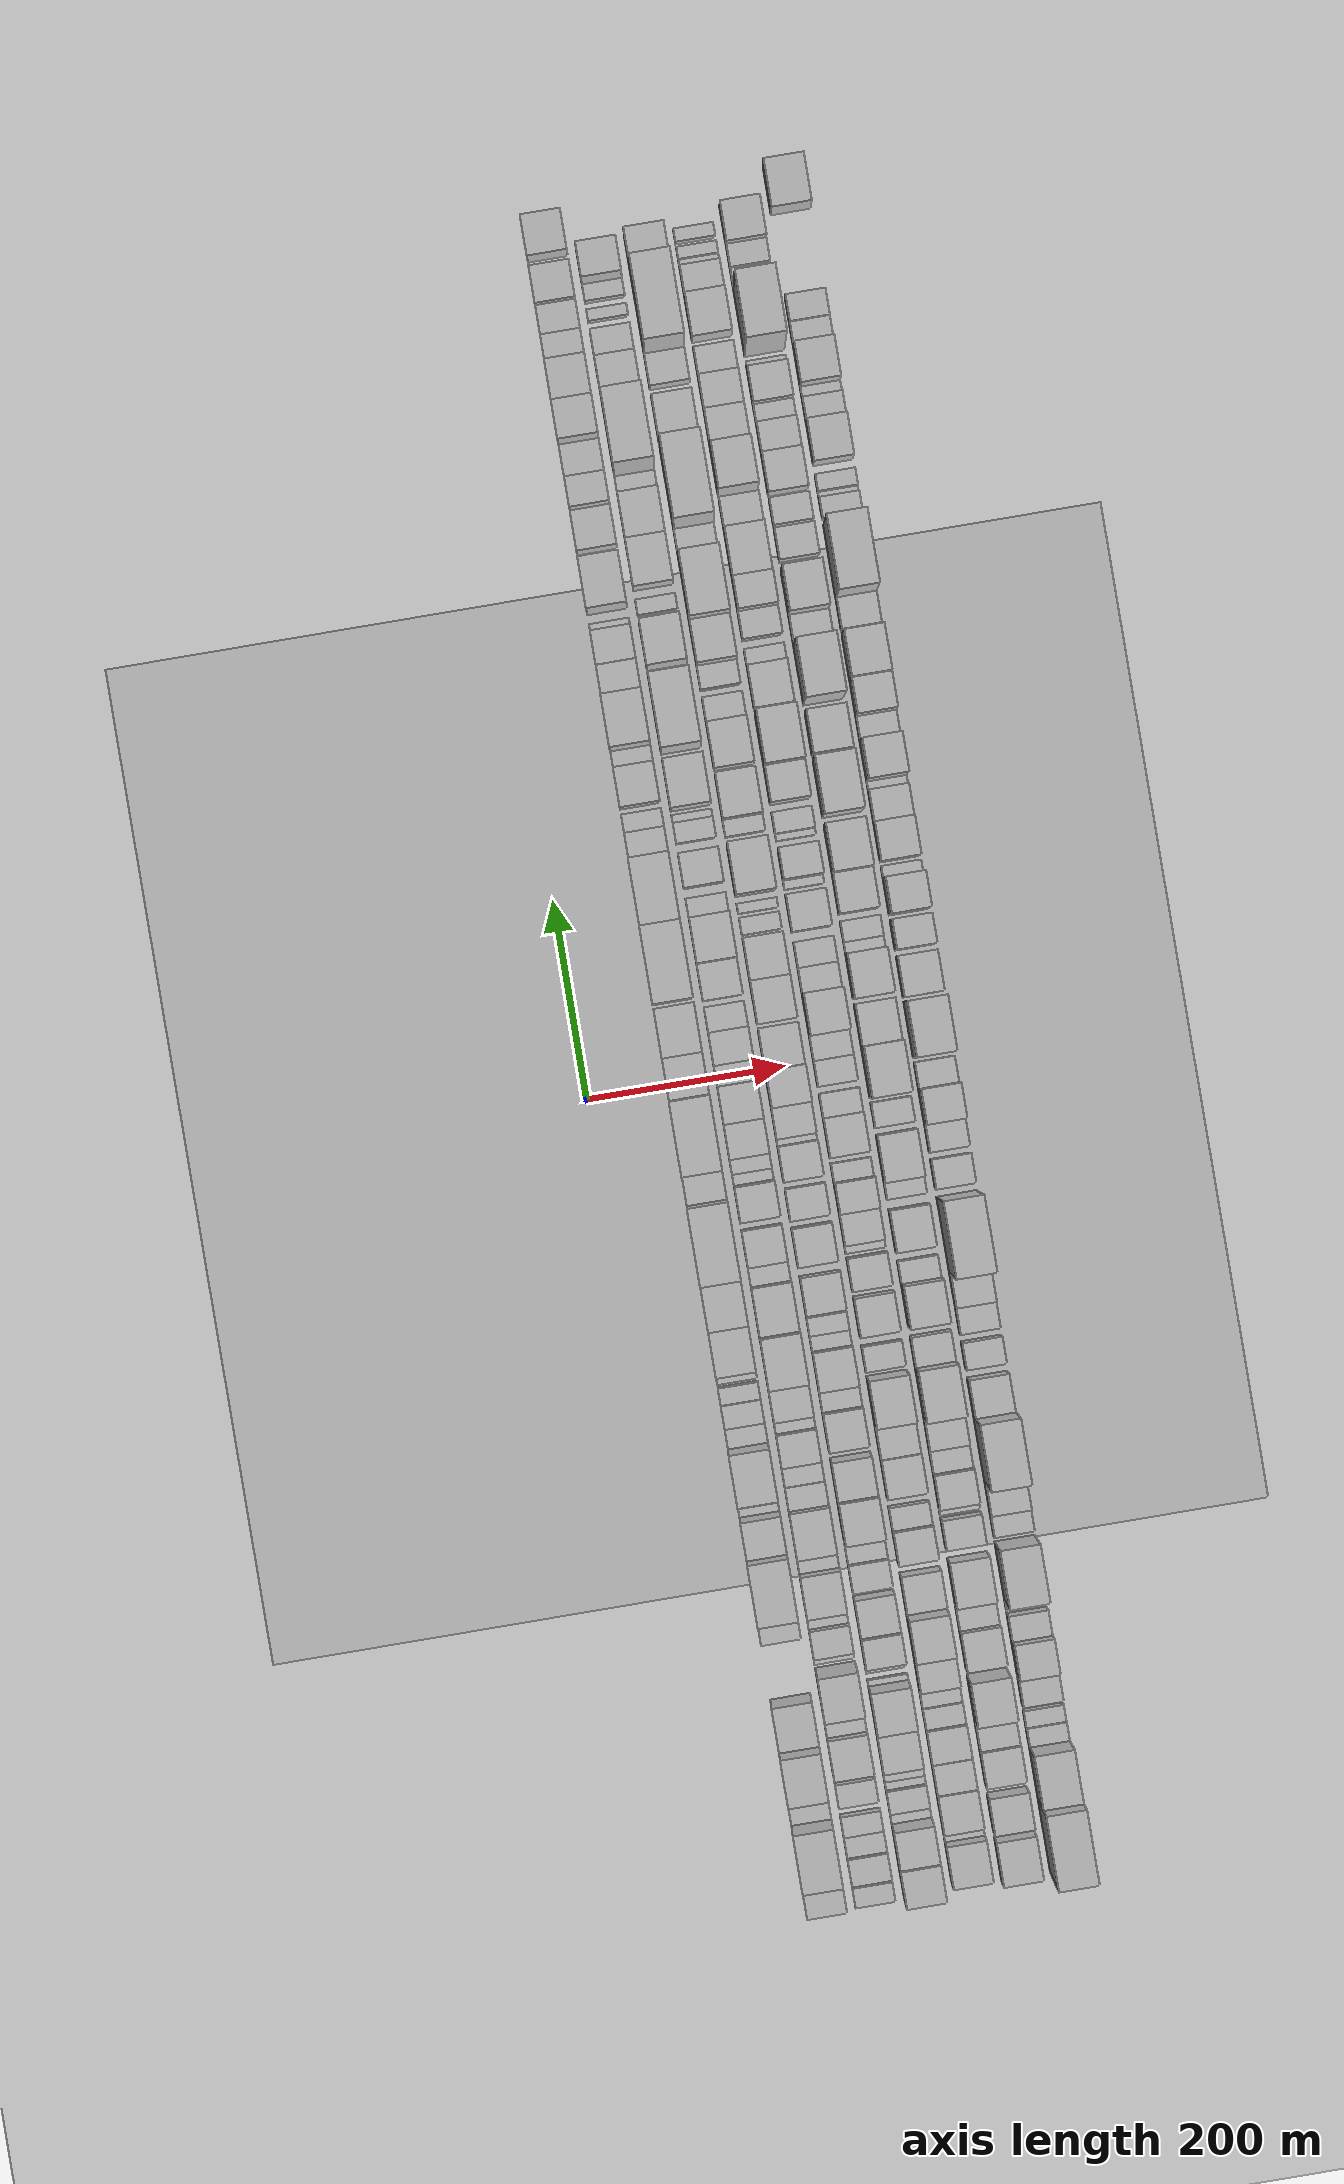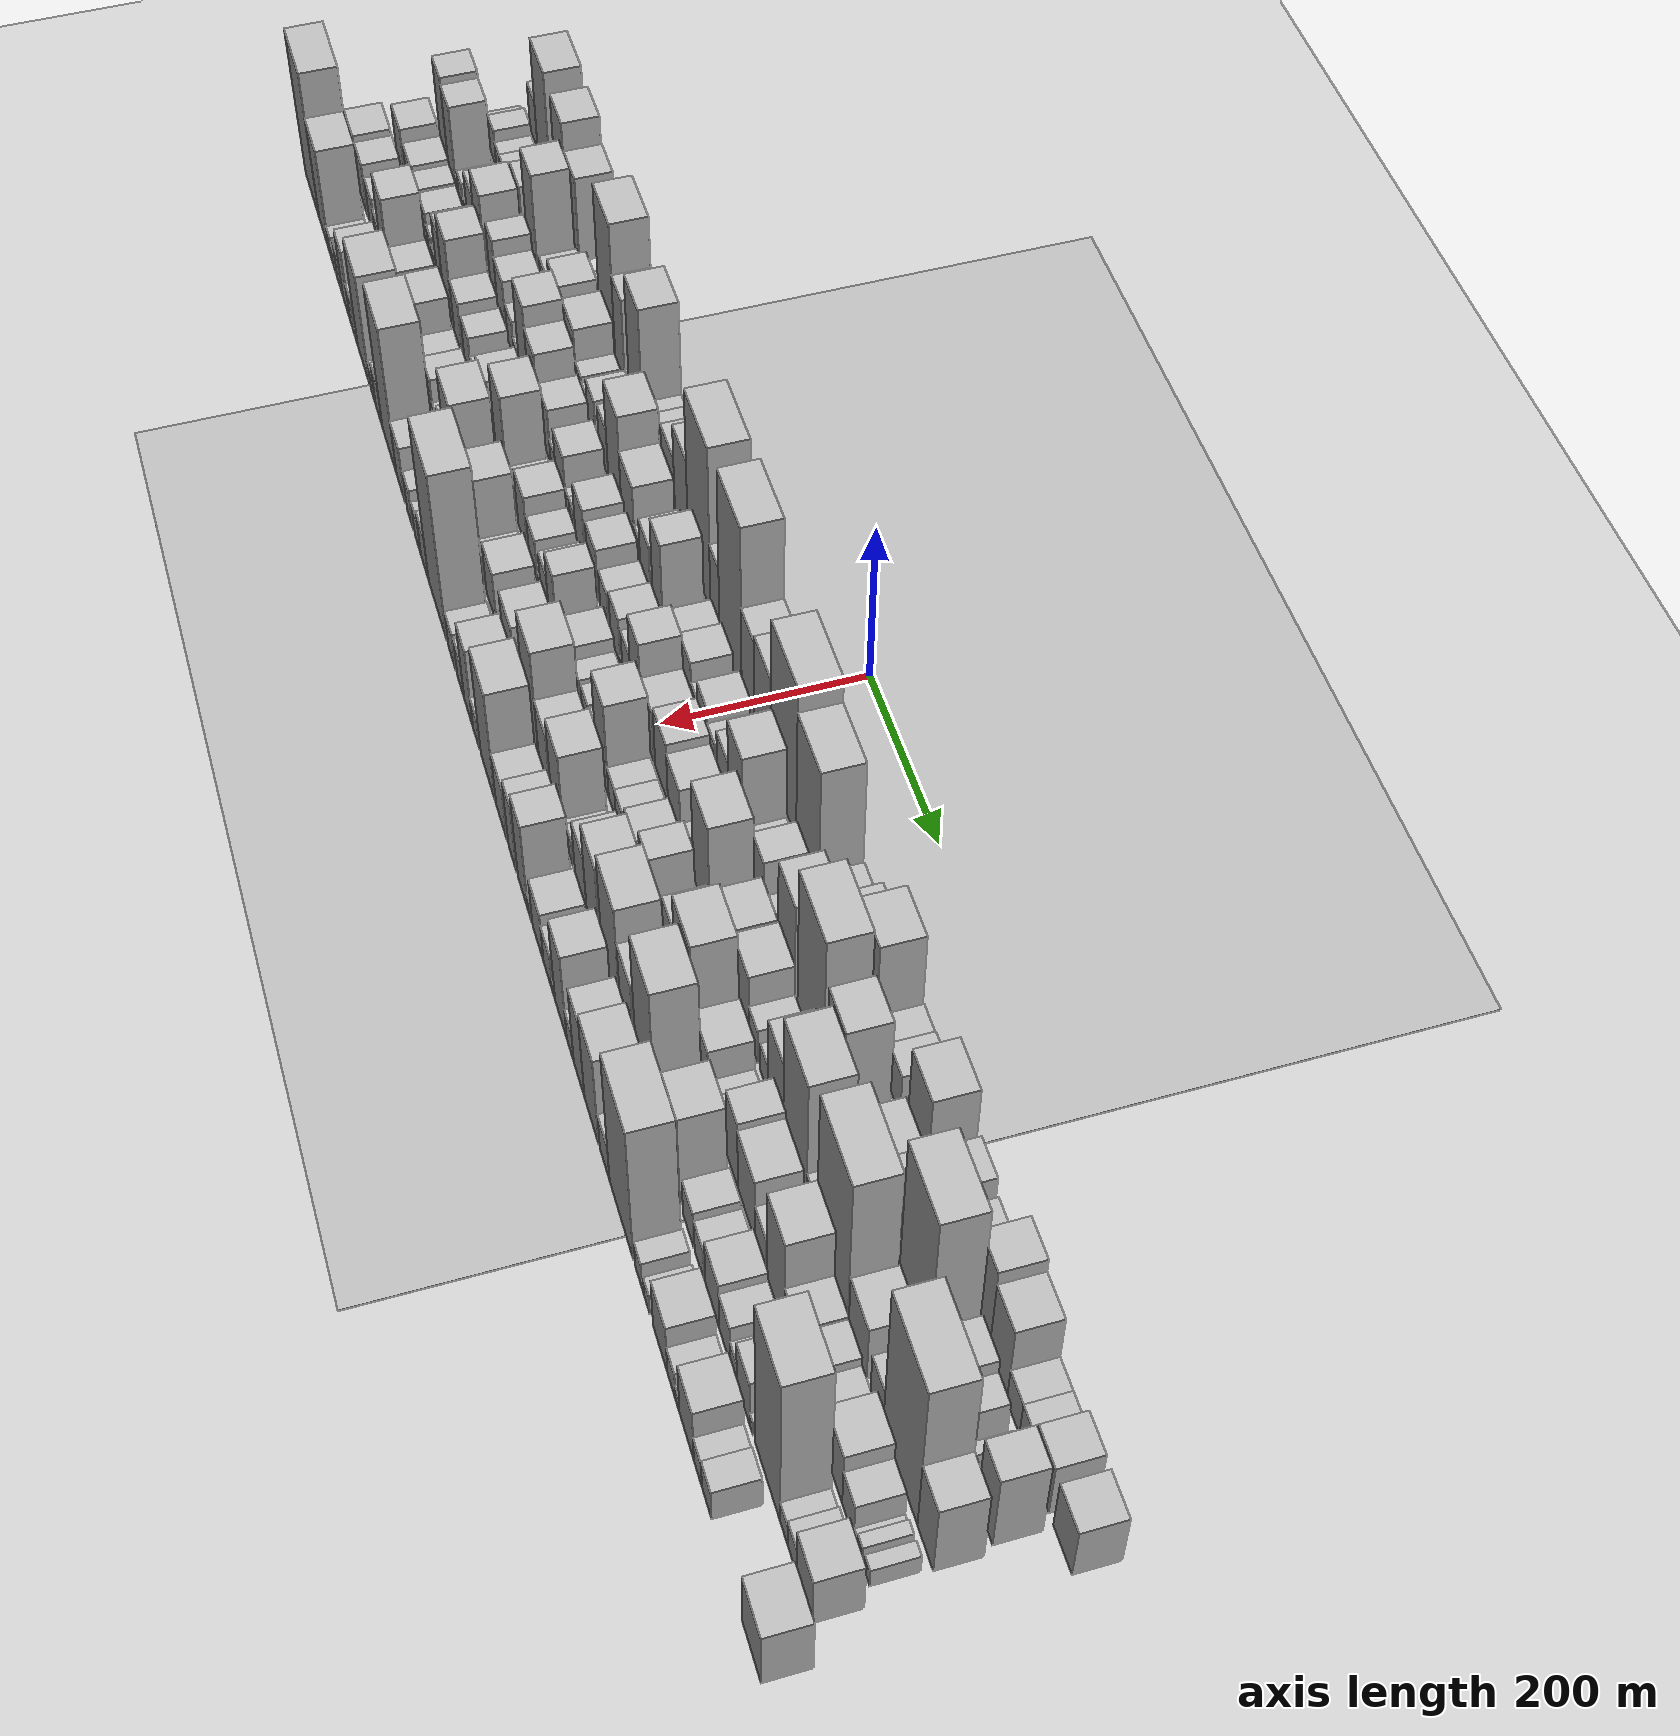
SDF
<?xml version="1.0" encoding="utf-8"?>

<sdf version="1.6">

   <world name="default">

      <gui fullscreen="0">

         <camera name="user_camera">

            <pose>-15 0 4.57585 0 0 0</pose>

            <view_controller>orbit</view_controller>

         </camera>

      </gui>

      <scene>

         <sky>

           <clouds>

             <speed>12</speed>

           </clouds>

         </sky>

         <ambient>0.4 0.4 0.4 1</ambient>

         <background>0.7 0.7 0.7 1</background>

         <shadows>1</shadows>

      </scene>

      <gravity>0 0 -9.8066</gravity>

      <magnetic_field>6e-06 2.3e-05 -4.2e-05</magnetic_field>

      <physics default="0" name="default_physics" type="ode">

         <ode>

            <solver>

               <type>quick</type>

               <iters>10</iters>

               <sor>1.0</sor>

               <use_dynamic_moi_rescaling>0</use_dynamic_moi_rescaling>

            </solver>

            <constraints>

               <cfm>0</cfm>

               <erp>0.2</erp>

               <contact_max_correcting_vel>100</contact_max_correcting_vel>

               <contact_surface_layer>0.001</contact_surface_layer>

            </constraints>

         </ode>

         <max_step_size>0.004</max_step_size>

         <real_time_factor>1</real_time_factor>

         <real_time_update_rate>250</real_time_update_rate>

      </physics>

      <light name="sun" type="directional">

         <cast_shadows>1</cast_shadows>

         <pose>0 0 10 0 0 0</pose>

         <diffuse>0.8 0.8 0.8 1</diffuse>

         <specular>0.2 0.2 0.2 1</specular>

         <attenuation>

            <range>1000</range>

            <constant>0.9</constant>

            <linear>0.01</linear>

            <quadratic>0.001</quadratic>

         </attenuation>

         <direction>-0.5 0.1 -0.9</direction>

      </light>

      <include>

         <name>ground_plane_1</name>

         <uri>model://HANNAS_ground_plane</uri>

         <pose>0 0 0  0 0 0</pose>

      </include>

      <include>

         <name>ground_plane_2</name>

         <uri>model://HANNAS_ground_plane</uri>

         <pose>100 0 0  0 0 0</pose>

      </include>

      <model name="building_1">

         <static>1</static>

         <pose frame="">100.0000 -813.3282 0 0.000000 0.000000 0.000000</pose>

         <link name="link">

            <pose frame="">0 0 33.00 0 0 0</pose>

            <collision name="collision">

               <geometry>

                  <box>

                     <size>40.0000 33.3435 66.0000</size>

                  </box>

               </geometry>

               <max_contacts>10</max_contacts>

               <surface>

                  <contact>

                     <ode/>

                  </contact>

                  <bounce/>

                  <friction>

                     <torsional>

                        <ode/>

                     </torsional>

                     <ode/>

                  </friction>

               </surface>

            </collision>

            <visual name="visual">

               <cast_shadows>0</cast_shadows>

               <geometry>

                  <box>

                     <size>40.0000 33.3435 66.0000</size>

                  </box>

               </geometry>

               <material>

                  <script>

                     <uri>model://HANNAS_wall/materials/scripts</uri>

                     <uri>model://HANNAS_wall/materials/textures</uri>

                     <name>vrc/HANNAS_wall</name>

                  </script>

               </material>

            </visual>

            <self_collide>0</self_collide>

            <enable_wind>0</enable_wind>

            <kinematic>0</kinematic>

         </link>

      </model>

      <model name="building_2">

         <static>1</static>

         <pose frame="">100.0000 -767.2986 0 0.000000 0.000000 0.000000</pose>

         <link name="link">

            <pose frame="">0 0 75.00 0 0 0</pose>

            <collision name="collision">

               <geometry>

                  <box>

                     <size>40.0000 58.7158 150.0000</size>

                  </box>

               </geometry>

               <max_contacts>10</max_contacts>

               <surface>

                  <contact>

                     <ode/>

                  </contact>

                  <bounce/>

                  <friction>

                     <torsional>

                        <ode/>

                     </torsional>

                     <ode/>

                  </friction>

               </surface>

            </collision>

            <visual name="visual">

               <cast_shadows>0</cast_shadows>

               <geometry>

                  <box>

                     <size>40.0000 58.7158 150.0000</size>

                  </box>

               </geometry>

               <material>

                  <script>

                     <uri>model://HANNAS_wall/materials/scripts</uri>

                     <uri>model://HANNAS_wall/materials/textures</uri>

                     <name>vrc/HANNAS_wall</name>

                  </script>

               </material>

            </visual>

            <self_collide>0</self_collide>

            <enable_wind>0</enable_wind>

            <kinematic>0</kinematic>

         </link>

      </model>

      <model name="building_3">

         <static>1</static>

         <pose frame="">100.0000 -724.9146 0 0.000000 0.000000 0.000000</pose>

         <link name="link">

            <pose frame="">0 0 24.00 0 0 0</pose>

            <collision name="collision">

               <geometry>

                  <box>

                     <size>40.0000 26.0522 48.0000</size>

                  </box>

               </geometry>

               <max_contacts>10</max_contacts>

               <surface>

                  <contact>

                     <ode/>

                  </contact>

                  <bounce/>

                  <friction>

                     <torsional>

                        <ode/>

                     </torsional>

                     <ode/>

                  </friction>

               </surface>

            </collision>

            <visual name="visual">

               <cast_shadows>0</cast_shadows>

               <geometry>

                  <box>

                     <size>40.0000 26.0522 48.0000</size>

                  </box>

               </geometry>

               <material>

                  <script>

                     <uri>model://HANNAS_wall/materials/scripts</uri>

                     <uri>model://HANNAS_wall/materials/textures</uri>

                     <name>vrc/HANNAS_wall</name>

                  </script>

               </material>

            </visual>

            <self_collide>0</self_collide>

            <enable_wind>0</enable_wind>

            <kinematic>0</kinematic>

         </link>

      </model>

      <model name="building_4">

         <static>1</static>

         <pose frame="">100.0000 -687.8914 0 0.000000 0.000000 0.000000</pose>

         <link name="link">

            <pose frame="">0 0 72.00 0 0 0</pose>

            <collision name="collision">

               <geometry>

                  <box>

                     <size>40.0000 47.9941 144.0000</size>

                  </box>

               </geometry>

               <max_contacts>10</max_contacts>

               <surface>

                  <contact>

                     <ode/>

                  </contact>

                  <bounce/>

                  <friction>

                     <torsional>

                        <ode/>

                     </torsional>

                     <ode/>

                  </friction>

               </surface>

            </collision>

            <visual name="visual">

               <cast_shadows>0</cast_shadows>

               <geometry>

                  <box>

                     <size>40.0000 47.9941 144.0000</size>

                  </box>

               </geometry>

               <material>

                  <script>

                     <uri>model://HANNAS_wall/materials/scripts</uri>

                     <uri>model://HANNAS_wall/materials/textures</uri>

                     <name>vrc/HANNAS_wall</name>

                  </script>

               </material>

            </visual>

            <self_collide>0</self_collide>

            <enable_wind>0</enable_wind>

            <kinematic>0</kinematic>

         </link>

      </model>

      <model name="building_5">

         <static>1</static>

         <pose frame="">100.0000 -637.8345 0 0.000000 0.000000 0.000000</pose>

         <link name="link">

            <pose frame="">0 0 55.50 0 0 0</pose>

            <collision name="collision">

               <geometry>

                  <box>

                     <size>40.0000 44.1198 111.0000</size>

                  </box>

               </geometry>

               <max_contacts>10</max_contacts>

               <surface>

                  <contact>

                     <ode/>

                  </contact>

                  <bounce/>

                  <friction>

                     <torsional>

                        <ode/>

                     </torsional>

                     <ode/>

                  </friction>

               </surface>

            </collision>

            <visual name="visual">

               <cast_shadows>0</cast_shadows>

               <geometry>

                  <box>

                     <size>40.0000 44.1198 111.0000</size>

                  </box>

               </geometry>

               <material>

                  <script>

                     <uri>model://HANNAS_wall/materials/scripts</uri>

                     <uri>model://HANNAS_wall/materials/textures</uri>

                     <name>vrc/HANNAS_wall</name>

                  </script>

               </material>

            </visual>

            <self_collide>0</self_collide>

            <enable_wind>0</enable_wind>

            <kinematic>0</kinematic>

         </link>

      </model>

      <model name="building_6">

         <static>1</static>

         <pose frame="">100.0000 -549.9230 0 0.000000 0.000000 0.000000</pose>

         <link name="link">

            <pose frame="">0 0 18.00 0 0 0</pose>

            <collision name="collision">

               <geometry>

                  <box>

                     <size>40.0000 18.5677 36.0000</size>

                  </box>

               </geometry>

               <max_contacts>10</max_contacts>

               <surface>

                  <contact>

                     <ode/>

                  </contact>

                  <bounce/>

                  <friction>

                     <torsional>

                        <ode/>

                     </torsional>

                     <ode/>

                  </friction>

               </surface>

            </collision>

            <visual name="visual">

               <cast_shadows>0</cast_shadows>

               <geometry>

                  <box>

                     <size>40.0000 18.5677 36.0000</size>

                  </box>

               </geometry>

               <material>

                  <script>

                     <uri>model://HANNAS_wall/materials/scripts</uri>

                     <uri>model://HANNAS_wall/materials/textures</uri>

                     <name>vrc/HANNAS_wall</name>

                  </script>

               </material>

            </visual>

            <self_collide>0</self_collide>

            <enable_wind>0</enable_wind>

            <kinematic>0</kinematic>

         </link>

      </model>

      <model name="building_7">

         <static>1</static>

         <pose frame="">100.0000 -500.5993 0 0.000000 0.000000 0.000000</pose>

         <link name="link">

            <pose frame="">0 0 88.50 0 0 0</pose>

            <collision name="collision">

               <geometry>

                  <box>

                     <size>40.0000 62.0797 177.0000</size>

                  </box>

               </geometry>

               <max_contacts>10</max_contacts>

               <surface>

                  <contact>

                     <ode/>

                  </contact>

                  <bounce/>

                  <friction>

                     <torsional>

                        <ode/>

                     </torsional>

                     <ode/>

                  </friction>

               </surface>

            </collision>

            <visual name="visual">

               <cast_shadows>0</cast_shadows>

               <geometry>

                  <box>

                     <size>40.0000 62.0797 177.0000</size>

                  </box>

               </geometry>

               <material>

                  <script>

                     <uri>model://HANNAS_wall/materials/scripts</uri>

                     <uri>model://HANNAS_wall/materials/textures</uri>

                     <name>vrc/HANNAS_wall</name>

                  </script>

               </material>

            </visual>

            <self_collide>0</self_collide>

            <enable_wind>0</enable_wind>

            <kinematic>0</kinematic>

         </link>

      </model>

      <model name="building_8">

         <static>1</static>

         <pose frame="">100.0000 -450.7751 0 0.000000 0.000000 0.000000</pose>

         <link name="link">

            <pose frame="">0 0 55.50 0 0 0</pose>

            <collision name="collision">

               <geometry>

                  <box>

                     <size>40.0000 37.5688 111.0000</size>

                  </box>

               </geometry>

               <max_contacts>10</max_contacts>

               <surface>

                  <contact>

                     <ode/>

                  </contact>

                  <bounce/>

                  <friction>

                     <torsional>

                        <ode/>

                     </torsional>

                     <ode/>

                  </friction>

               </surface>

            </collision>

            <visual name="visual">

               <cast_shadows>0</cast_shadows>

               <geometry>

                  <box>

                     <size>40.0000 37.5688 111.0000</size>

                  </box>

               </geometry>

               <material>

                  <script>

                     <uri>model://HANNAS_wall/materials/scripts</uri>

                     <uri>model://HANNAS_wall/materials/textures</uri>

                     <name>vrc/HANNAS_wall</name>

                  </script>

               </material>

            </visual>

            <self_collide>0</self_collide>

            <enable_wind>0</enable_wind>

            <kinematic>0</kinematic>

         </link>

      </model>

      <model name="building_9">

         <static>1</static>

         <pose frame="">100.0000 -427.7670 0 0.000000 0.000000 0.000000</pose>

         <link name="link">

            <pose frame="">0 0 9.00 0 0 0</pose>

            <collision name="collision">

               <geometry>

                  <box>

                     <size>40.0000 8.4473 18.0000</size>

                  </box>

               </geometry>

               <max_contacts>10</max_contacts>

               <surface>

                  <contact>

                     <ode/>

                  </contact>

                  <bounce/>

                  <friction>

                     <torsional>

                        <ode/>

                     </torsional>

                     <ode/>

                  </friction>

               </surface>

            </collision>

            <visual name="visual">

               <cast_shadows>0</cast_shadows>

               <geometry>

                  <box>

                     <size>40.0000 8.4473 18.0000</size>

                  </box>

               </geometry>

               <material>

                  <script>

                     <uri>model://HANNAS_wall/materials/scripts</uri>

                     <uri>model://HANNAS_wall/materials/textures</uri>

                     <name>vrc/HANNAS_wall</name>

                  </script>

               </material>

            </visual>

            <self_collide>0</self_collide>

            <enable_wind>0</enable_wind>

            <kinematic>0</kinematic>

         </link>

      </model>

      <model name="building_10">

         <static>1</static>

         <pose frame="">100.0000 -388.4443 0 0.000000 0.000000 0.000000</pose>

         <link name="link">

            <pose frame="">0 0 81.00 0 0 0</pose>

            <collision name="collision">

               <geometry>

                  <box>

                     <size>40.0000 52.1980 162.0000</size>

                  </box>

               </geometry>

               <max_contacts>10</max_contacts>

               <surface>

                  <contact>

                     <ode/>

                  </contact>

                  <bounce/>

                  <friction>

                     <torsional>

                        <ode/>

                     </torsional>

                     <ode/>

                  </friction>

               </surface>

            </collision>

            <visual name="visual">

               <cast_shadows>0</cast_shadows>

               <geometry>

                  <box>

                     <size>40.0000 52.1980 162.0000</size>

                  </box>

               </geometry>

               <material>

                  <script>

                     <uri>model://HANNAS_wall/materials/scripts</uri>

                     <uri>model://HANNAS_wall/materials/textures</uri>

                     <name>vrc/HANNAS_wall</name>

                  </script>

               </material>

            </visual>

            <self_collide>0</self_collide>

            <enable_wind>0</enable_wind>

            <kinematic>0</kinematic>

         </link>

      </model>

      <model name="building_11">

         <static>1</static>

         <pose frame="">100.0000 -352.5850 0 0.000000 0.000000 0.000000</pose>

         <link name="link">

            <pose frame="">0 0 19.50 0 0 0</pose>

            <collision name="collision">

               <geometry>

                  <box>

                     <size>40.0000 19.5205 39.0000</size>

                  </box>

               </geometry>

               <max_contacts>10</max_contacts>

               <surface>

                  <contact>

                     <ode/>

                  </contact>

                  <bounce/>

                  <friction>

                     <torsional>

                        <ode/>

                     </torsional>

                     <ode/>

                  </friction>

               </surface>

            </collision>

            <visual name="visual">

               <cast_shadows>0</cast_shadows>

               <geometry>

                  <box>

                     <size>40.0000 19.5205 39.0000</size>

                  </box>

               </geometry>

               <material>

                  <script>

                     <uri>model://HANNAS_wall/materials/scripts</uri>

                     <uri>model://HANNAS_wall/materials/textures</uri>

                     <name>vrc/HANNAS_wall</name>

                  </script>

               </material>

            </visual>

            <self_collide>0</self_collide>

            <enable_wind>0</enable_wind>

            <kinematic>0</kinematic>

         </link>

      </model>

      <model name="building_12">

         <static>1</static>

         <pose frame="">100.0000 -331.0604 0 0.000000 0.000000 0.000000</pose>

         <link name="link">

            <pose frame="">0 0 21.00 0 0 0</pose>

            <collision name="collision">

               <geometry>

                  <box>

                     <size>40.0000 23.5287 42.0000</size>

                  </box>

               </geometry>

               <max_contacts>10</max_contacts>

               <surface>

                  <contact>

                     <ode/>

                  </contact>

                  <bounce/>

                  <friction>

                     <torsional>

                        <ode/>

                     </torsional>

                     <ode/>

                  </friction>

               </surface>

            </collision>

            <visual name="visual">

               <cast_shadows>0</cast_shadows>

               <geometry>

                  <box>

                     <size>40.0000 23.5287 42.0000</size>

                  </box>

               </geometry>

               <material>

                  <script>

                     <uri>model://HANNAS_wall/materials/scripts</uri>

                     <uri>model://HANNAS_wall/materials/textures</uri>

                     <name>vrc/HANNAS_wall</name>

                  </script>

               </material>

            </visual>

            <self_collide>0</self_collide>

            <enable_wind>0</enable_wind>

            <kinematic>0</kinematic>

         </link>

      </model>

      <model name="building_13">

         <static>1</static>

         <pose frame="">100.0000 -310.6042 0 0.000000 0.000000 0.000000</pose>

         <link name="link">

            <pose frame="">0 0 16.50 0 0 0</pose>

            <collision name="collision">

               <geometry>

                  <box>

                     <size>40.0000 17.3837 33.0000</size>

                  </box>

               </geometry>

               <max_contacts>10</max_contacts>

               <surface>

                  <contact>

                     <ode/>

                  </contact>

                  <bounce/>

                  <friction>

                     <torsional>

                        <ode/>

                     </torsional>

                     <ode/>

                  </friction>

               </surface>

            </collision>

            <visual name="visual">

               <cast_shadows>0</cast_shadows>

               <geometry>

                  <box>

                     <size>40.0000 17.3837 33.0000</size>

                  </box>

               </geometry>

               <material>

                  <script>

                     <uri>model://HANNAS_wall/materials/scripts</uri>

                     <uri>model://HANNAS_wall/materials/textures</uri>

                     <name>vrc/HANNAS_wall</name>

                  </script>

               </material>

            </visual>

            <self_collide>0</self_collide>

            <enable_wind>0</enable_wind>

            <kinematic>0</kinematic>

         </link>

      </model>

      <model name="building_14">

         <static>1</static>

         <pose frame="">100.0000 -294.4897 0 0.000000 0.000000 0.000000</pose>

         <link name="link">

            <pose frame="">0 0 10.50 0 0 0</pose>

            <collision name="collision">

               <geometry>

                  <box>

                     <size>40.0000 8.8454 21.0000</size>

                  </box>

               </geometry>

               <max_contacts>10</max_contacts>

               <surface>

                  <contact>

                     <ode/>

                  </contact>

                  <bounce/>

                  <friction>

                     <torsional>

                        <ode/>

                     </torsional>

                     <ode/>

                  </friction>

               </surface>

            </collision>

            <visual name="visual">

               <cast_shadows>0</cast_shadows>

               <geometry>

                  <box>

                     <size>40.0000 8.8454 21.0000</size>

                  </box>

               </geometry>

               <material>

                  <script>

                     <uri>model://HANNAS_wall/materials/scripts</uri>

                     <uri>model://HANNAS_wall/materials/textures</uri>

                     <name>vrc/HANNAS_wall</name>

                  </script>

               </material>

            </visual>

            <self_collide>0</self_collide>

            <enable_wind>0</enable_wind>

            <kinematic>0</kinematic>

         </link>

      </model>

      <model name="building_15">

         <static>1</static>

         <pose frame="">100.0000 -266.5161 0 0.000000 0.000000 0.000000</pose>

         <link name="link">

            <pose frame="">0 0 40.50 0 0 0</pose>

            <collision name="collision">

               <geometry>

                  <box>

                     <size>40.0000 47.1018 81.0000</size>

                  </box>

               </geometry>

               <max_contacts>10</max_contacts>

               <surface>

                  <contact>

                     <ode/>

                  </contact>

                  <bounce/>

                  <friction>

                     <torsional>

                        <ode/>

                     </torsional>

                     <ode/>

                  </friction>

               </surface>

            </collision>

            <visual name="visual">

               <cast_shadows>0</cast_shadows>

               <geometry>

                  <box>

                     <size>40.0000 47.1018 81.0000</size>

                  </box>

               </geometry>

               <material>

                  <script>

                     <uri>model://HANNAS_wall/materials/scripts</uri>

                     <uri>model://HANNAS_wall/materials/textures</uri>

                     <name>vrc/HANNAS_wall</name>

                  </script>

               </material>

            </visual>

            <self_collide>0</self_collide>

            <enable_wind>0</enable_wind>

            <kinematic>0</kinematic>

         </link>

      </model>

      <model name="building_16">

         <static>1</static>

         <pose frame="">100.0000 -219.1321 0 0.000000 0.000000 0.000000</pose>

         <link name="link">

            <pose frame="">0 0 63.00 0 0 0</pose>

            <collision name="collision">

               <geometry>

                  <box>

                     <size>40.0000 47.6662 126.0000</size>

                  </box>

               </geometry>

               <max_contacts>10</max_contacts>

               <surface>

                  <contact>

                     <ode/>

                  </contact>

                  <bounce/>

                  <friction>

                     <torsional>

                        <ode/>

                     </torsional>

                     <ode/>

                  </friction>

               </surface>

            </collision>

            <visual name="visual">

               <cast_shadows>0</cast_shadows>

               <geometry>

                  <box>

                     <size>40.0000 47.6662 126.0000</size>

                  </box>

               </geometry>

               <material>

                  <script>

                     <uri>model://HANNAS_wall/materials/scripts</uri>

                     <uri>model://HANNAS_wall/materials/textures</uri>

                     <name>vrc/HANNAS_wall</name>

                  </script>

               </material>

            </visual>

            <self_collide>0</self_collide>

            <enable_wind>0</enable_wind>

            <kinematic>0</kinematic>

         </link>

      </model>

      <model name="building_17">

         <static>1</static>

         <pose frame="">100.0000 -156.6568 0 0.000000 0.000000 0.000000</pose>

         <link name="link">

            <pose frame="">0 0 109.50 0 0 0</pose>

            <collision name="collision">

               <geometry>

                  <box>

                     <size>40.0000 77.2843 219.0000</size>

                  </box>

               </geometry>

               <max_contacts>10</max_contacts>

               <surface>

                  <contact>

                     <ode/>

                  </contact>

                  <bounce/>

                  <friction>

                     <torsional>

                        <ode/>

                     </torsional>

                     <ode/>

                  </friction>

               </surface>

            </collision>

            <visual name="visual">

               <cast_shadows>0</cast_shadows>

               <geometry>

                  <box>

                     <size>40.0000 77.2843 219.0000</size>

                  </box>

               </geometry>

               <material>

                  <script>

                     <uri>model://HANNAS_wall/materials/scripts</uri>

                     <uri>model://HANNAS_wall/materials/textures</uri>

                     <name>vrc/HANNAS_wall</name>

                  </script>

               </material>

            </visual>

            <self_collide>0</self_collide>

            <enable_wind>0</enable_wind>

            <kinematic>0</kinematic>

         </link>

      </model>

      <model name="building_18">

         <static>1</static>

         <pose frame="">100.0000 -102.6822 0 0.000000 0.000000 0.000000</pose>

         <link name="link">

            <pose frame="">0 0 46.50 0 0 0</pose>

            <collision name="collision">

               <geometry>

                  <box>

                     <size>40.0000 30.6650 93.0000</size>

                  </box>

               </geometry>

               <max_contacts>10</max_contacts>

               <surface>

                  <contact>

                     <ode/>

                  </contact>

                  <bounce/>

                  <friction>

                     <torsional>

                        <ode/>

                     </torsional>

                     <ode/>

                  </friction>

               </surface>

            </collision>

            <visual name="visual">

               <cast_shadows>0</cast_shadows>

               <geometry>

                  <box>

                     <size>40.0000 30.6650 93.0000</size>

                  </box>

               </geometry>

               <material>

                  <script>

                     <uri>model://HANNAS_wall/materials/scripts</uri>

                     <uri>model://HANNAS_wall/materials/textures</uri>

                     <name>vrc/HANNAS_wall</name>

                  </script>

               </material>

            </visual>

            <self_collide>0</self_collide>

            <enable_wind>0</enable_wind>

            <kinematic>0</kinematic>

         </link>

      </model>

      <model name="building_19">

         <static>1</static>

         <pose frame="">100.0000 -50.2767 0 0.000000 0.000000 0.000000</pose>

         <link name="link">

            <pose frame="">0 0 112.50 0 0 0</pose>

            <collision name="collision">

               <geometry>

                  <box>

                     <size>40.0000 74.1460 225.0000</size>

                  </box>

               </geometry>

               <max_contacts>10</max_contacts>

               <surface>

                  <contact>

                     <ode/>

                  </contact>

                  <bounce/>

                  <friction>

                     <torsional>

                        <ode/>

                     </torsional>

                     <ode/>

                  </friction>

               </surface>

            </collision>

            <visual name="visual">

               <cast_shadows>0</cast_shadows>

               <geometry>

                  <box>

                     <size>40.0000 74.1460 225.0000</size>

                  </box>

               </geometry>

               <material>

                  <script>

                     <uri>model://HANNAS_wall/materials/scripts</uri>

                     <uri>model://HANNAS_wall/materials/textures</uri>

                     <name>vrc/HANNAS_wall</name>

                  </script>

               </material>

            </visual>

            <self_collide>0</self_collide>

            <enable_wind>0</enable_wind>

            <kinematic>0</kinematic>

         </link>

      </model>

      <model name="building_20">

         <static>1</static>

         <pose frame="">100.0000 7.6626 0 0.000000 0.000000 0.000000</pose>

         <link name="link">

            <pose frame="">0 0 60.00 0 0 0</pose>

            <collision name="collision">

               <geometry>

                  <box>

                     <size>40.0000 41.7325 120.0000</size>

                  </box>

               </geometry>

               <max_contacts>10</max_contacts>

               <surface>

                  <contact>

                     <ode/>

                  </contact>

                  <bounce/>

                  <friction>

                     <torsional>

                        <ode/>

                     </torsional>

                     <ode/>

                  </friction>

               </surface>

            </collision>

            <visual name="visual">

               <cast_shadows>0</cast_shadows>

               <geometry>

                  <box>

                     <size>40.0000 41.7325 120.0000</size>

                  </box>

               </geometry>

               <material>

                  <script>

                     <uri>model://HANNAS_wall/materials/scripts</uri>

                     <uri>model://HANNAS_wall/materials/textures</uri>

                     <name>vrc/HANNAS_wall</name>

                  </script>

               </material>

            </visual>

            <self_collide>0</self_collide>

            <enable_wind>0</enable_wind>

            <kinematic>0</kinematic>

         </link>

      </model>

      <model name="building_21">

         <static>1</static>

         <pose frame="">100.0000 53.1898 0 0.000000 0.000000 0.000000</pose>

         <link name="link">

            <pose frame="">0 0 64.50 0 0 0</pose>

            <collision name="collision">

               <geometry>

                  <box>

                     <size>40.0000 49.3220 129.0000</size>

                  </box>

               </geometry>

               <max_contacts>10</max_contacts>

               <surface>

                  <contact>

                     <ode/>

                  </contact>

                  <bounce/>

                  <friction>

                     <torsional>

                        <ode/>

                     </torsional>

                     <ode/>

                  </friction>

               </surface>

            </collision>

            <visual name="visual">

               <cast_shadows>0</cast_shadows>

               <geometry>

                  <box>

                     <size>40.0000 49.3220 129.0000</size>

                  </box>

               </geometry>

               <material>

                  <script>

                     <uri>model://HANNAS_wall/materials/scripts</uri>

                     <uri>model://HANNAS_wall/materials/textures</uri>

                     <name>vrc/HANNAS_wall</name>

                  </script>

               </material>

            </visual>

            <self_collide>0</self_collide>

            <enable_wind>0</enable_wind>

            <kinematic>0</kinematic>

         </link>

      </model>

      <model name="building_22">

         <static>1</static>

         <pose frame="">100.0000 120.4586 0 0.000000 0.000000 0.000000</pose>

         <link name="link">

            <pose frame="">0 0 105.00 0 0 0</pose>

            <collision name="collision">

               <geometry>

                  <box>

                     <size>40.0000 77.2155 210.0000</size>

                  </box>

               </geometry>

               <max_contacts>10</max_contacts>

               <surface>

                  <contact>

                     <ode/>

                  </contact>

                  <bounce/>

                  <friction>

                     <torsional>

                        <ode/>

                     </torsional>

                     <ode/>

                  </friction>

               </surface>

            </collision>

            <visual name="visual">

               <cast_shadows>0</cast_shadows>

               <geometry>

                  <box>

                     <size>40.0000 77.2155 210.0000</size>

                  </box>

               </geometry>

               <material>

                  <script>

                     <uri>model://HANNAS_wall/materials/scripts</uri>

                     <uri>model://HANNAS_wall/materials/textures</uri>

                     <name>vrc/HANNAS_wall</name>

                  </script>

               </material>

            </visual>

            <self_collide>0</self_collide>

            <enable_wind>0</enable_wind>

            <kinematic>0</kinematic>

         </link>

      </model>

      <model name="building_23">

         <static>1</static>

         <pose frame="">100.0000 192.7061 0 0.000000 0.000000 0.000000</pose>

         <link name="link">

            <pose frame="">0 0 88.50 0 0 0</pose>

            <collision name="collision">

               <geometry>

                  <box>

                     <size>40.0000 67.2794 177.0000</size>

                  </box>

               </geometry>

               <max_contacts>10</max_contacts>

               <surface>

                  <contact>

                     <ode/>

                  </contact>

                  <bounce/>

                  <friction>

                     <torsional>

                        <ode/>

                     </torsional>

                     <ode/>

                  </friction>

               </surface>

            </collision>

            <visual name="visual">

               <cast_shadows>0</cast_shadows>

               <geometry>

                  <box>

                     <size>40.0000 67.2794 177.0000</size>

                  </box>

               </geometry>

               <material>

                  <script>

                     <uri>model://HANNAS_wall/materials/scripts</uri>

                     <uri>model://HANNAS_wall/materials/textures</uri>

                     <name>vrc/HANNAS_wall</name>

                  </script>

               </material>

            </visual>

            <self_collide>0</self_collide>

            <enable_wind>0</enable_wind>

            <kinematic>0</kinematic>

         </link>

      </model>

      <model name="building_24">

         <static>1</static>

         <pose frame="">100.0000 241.7687 0 0.000000 0.000000 0.000000</pose>

         <link name="link">

            <pose frame="">0 0 21.00 0 0 0</pose>

            <collision name="collision">

               <geometry>

                  <box>

                     <size>40.0000 24.8457 42.0000</size>

                  </box>

               </geometry>

               <max_contacts>10</max_contacts>

               <surface>

                  <contact>

                     <ode/>

                  </contact>

                  <bounce/>

                  <friction>

                     <torsional>

                        <ode/>

                     </torsional>

                     <ode/>

                  </friction>

               </surface>

            </collision>

            <visual name="visual">

               <cast_shadows>0</cast_shadows>

               <geometry>

                  <box>

                     <size>40.0000 24.8457 42.0000</size>

                  </box>

               </geometry>

               <material>

                  <script>

                     <uri>model://HANNAS_wall/materials/scripts</uri>

                     <uri>model://HANNAS_wall/materials/textures</uri>

                     <name>vrc/HANNAS_wall</name>

                  </script>

               </material>

            </visual>

            <self_collide>0</self_collide>

            <enable_wind>0</enable_wind>

            <kinematic>0</kinematic>

         </link>

      </model>

      <model name="building_25">

         <static>1</static>

         <pose frame="">100.0000 263.3841 0 0.000000 0.000000 0.000000</pose>

         <link name="link">

            <pose frame="">0 0 18.00 0 0 0</pose>

            <collision name="collision">

               <geometry>

                  <box>

                     <size>40.0000 18.3851 36.0000</size>

                  </box>

               </geometry>

               <max_contacts>10</max_contacts>

               <surface>

                  <contact>

                     <ode/>

                  </contact>

                  <bounce/>

                  <friction>

                     <torsional>

                        <ode/>

                     </torsional>

                     <ode/>

                  </friction>

               </surface>

            </collision>

            <visual name="visual">

               <cast_shadows>0</cast_shadows>

               <geometry>

                  <box>

                     <size>40.0000 18.3851 36.0000</size>

                  </box>

               </geometry>

               <material>

                  <script>

                     <uri>model://HANNAS_wall/materials/scripts</uri>

                     <uri>model://HANNAS_wall/materials/textures</uri>

                     <name>vrc/HANNAS_wall</name>

                  </script>

               </material>

            </visual>

            <self_collide>0</self_collide>

            <enable_wind>0</enable_wind>

            <kinematic>0</kinematic>

         </link>

      </model>

      <model name="building_26">

         <static>1</static>

         <pose frame="">100.0000 298.6132 0 0.000000 0.000000 0.000000</pose>

         <link name="link">

            <pose frame="">0 0 39.00 0 0 0</pose>

            <collision name="collision">

               <geometry>

                  <box>

                     <size>40.0000 40.0731 78.0000</size>

                  </box>

               </geometry>

               <max_contacts>10</max_contacts>

               <surface>

                  <contact>

                     <ode/>

                  </contact>

                  <bounce/>

                  <friction>

                     <torsional>

                        <ode/>

                     </torsional>

                     <ode/>

                  </friction>

               </surface>

            </collision>

            <visual name="visual">

               <cast_shadows>0</cast_shadows>

               <geometry>

                  <box>

                     <size>40.0000 40.0731 78.0000</size>

                  </box>

               </geometry>

               <material>

                  <script>

                     <uri>model://HANNAS_wall/materials/scripts</uri>

                     <uri>model://HANNAS_wall/materials/textures</uri>

                     <name>vrc/HANNAS_wall</name>

                  </script>

               </material>

            </visual>

            <self_collide>0</self_collide>

            <enable_wind>0</enable_wind>

            <kinematic>0</kinematic>

         </link>

      </model>

      <model name="building_27">

         <static>1</static>

         <pose frame="">100.0000 327.2101 0 0.000000 0.000000 0.000000</pose>

         <link name="link">

            <pose frame="">0 0 16.50 0 0 0</pose>

            <collision name="collision">

               <geometry>

                  <box>

                     <size>40.0000 17.1208 33.0000</size>

                  </box>

               </geometry>

               <max_contacts>10</max_contacts>

               <surface>

                  <contact>

                     <ode/>

                  </contact>

                  <bounce/>

                  <friction>

                     <torsional>

                        <ode/>

                     </torsional>

                     <ode/>

                  </friction>

               </surface>

            </collision>

            <visual name="visual">

               <cast_shadows>0</cast_shadows>

               <geometry>

                  <box>

                     <size>40.0000 17.1208 33.0000</size>

                  </box>

               </geometry>

               <material>

                  <script>

                     <uri>model://HANNAS_wall/materials/scripts</uri>

                     <uri>model://HANNAS_wall/materials/textures</uri>

                     <name>vrc/HANNAS_wall</name>

                  </script>

               </material>

            </visual>

            <self_collide>0</self_collide>

            <enable_wind>0</enable_wind>

            <kinematic>0</kinematic>

         </link>

      </model>

      <model name="building_28">

         <static>1</static>

         <pose frame="">100.0000 362.1164 0 0.000000 0.000000 0.000000</pose>

         <link name="link">

            <pose frame="">0 0 75.00 0 0 0</pose>

            <collision name="collision">

               <geometry>

                  <box>

                     <size>40.0000 52.6917 150.0000</size>

                  </box>

               </geometry>

               <max_contacts>10</max_contacts>

               <surface>

                  <contact>

                     <ode/>

                  </contact>

                  <bounce/>

                  <friction>

                     <torsional>

                        <ode/>

                     </torsional>

                     <ode/>

                  </friction>

               </surface>

            </collision>

            <visual name="visual">

               <cast_shadows>0</cast_shadows>

               <geometry>

                  <box>

                     <size>40.0000 52.6917 150.0000</size>

                  </box>

               </geometry>

               <material>

                  <script>

                     <uri>model://HANNAS_wall/materials/scripts</uri>

                     <uri>model://HANNAS_wall/materials/textures</uri>

                     <name>vrc/HANNAS_wall</name>

                  </script>

               </material>

            </visual>

            <self_collide>0</self_collide>

            <enable_wind>0</enable_wind>

            <kinematic>0</kinematic>

         </link>

      </model>

      <model name="building_29">

         <static>1</static>

         <pose frame="">100.0000 406.4023 0 0.000000 0.000000 0.000000</pose>

         <link name="link">

            <pose frame="">0 0 28.50 0 0 0</pose>

            <collision name="collision">

               <geometry>

                  <box>

                     <size>40.0000 29.8800 57.0000</size>

                  </box>

               </geometry>

               <max_contacts>10</max_contacts>

               <surface>

                  <contact>

                     <ode/>

                  </contact>

                  <bounce/>

                  <friction>

                     <torsional>

                        <ode/>

                     </torsional>

                     <ode/>

                  </friction>

               </surface>

            </collision>

            <visual name="visual">

               <cast_shadows>0</cast_shadows>

               <geometry>

                  <box>

                     <size>40.0000 29.8800 57.0000</size>

                  </box>

               </geometry>

               <material>

                  <script>

                     <uri>model://HANNAS_wall/materials/scripts</uri>

                     <uri>model://HANNAS_wall/materials/textures</uri>

                     <name>vrc/HANNAS_wall</name>

                  </script>

               </material>

            </visual>

            <self_collide>0</self_collide>

            <enable_wind>0</enable_wind>

            <kinematic>0</kinematic>

         </link>

      </model>

      <model name="building_30">

         <static>1</static>

         <pose frame="">100.0000 438.5393 0 0.000000 0.000000 0.000000</pose>

         <link name="link">

            <pose frame="">0 0 30.00 0 0 0</pose>

            <collision name="collision">

               <geometry>

                  <box>

                     <size>40.0000 34.3940 60.0000</size>

                  </box>

               </geometry>

               <max_contacts>10</max_contacts>

               <surface>

                  <contact>

                     <ode/>

                  </contact>

                  <bounce/>

                  <friction>

                     <torsional>

                        <ode/>

                     </torsional>

                     <ode/>

                  </friction>

               </surface>

            </collision>

            <visual name="visual">

               <cast_shadows>0</cast_shadows>

               <geometry>

                  <box>

                     <size>40.0000 34.3940 60.0000</size>

                  </box>

               </geometry>

               <material>

                  <script>

                     <uri>model://HANNAS_wall/materials/scripts</uri>

                     <uri>model://HANNAS_wall/materials/textures</uri>

                     <name>vrc/HANNAS_wall</name>

                  </script>

               </material>

            </visual>

            <self_collide>0</self_collide>

            <enable_wind>0</enable_wind>

            <kinematic>0</kinematic>

         </link>

      </model>

      <model name="building_31">

         <static>1</static>

         <pose frame="">100.0000 459.8285 0 0.000000 0.000000 0.000000</pose>

         <link name="link">

            <pose frame="">0 0 9.00 0 0 0</pose>

            <collision name="collision">

               <geometry>

                  <box>

                     <size>40.0000 8.1844 18.0000</size>

                  </box>

               </geometry>

               <max_contacts>10</max_contacts>

               <surface>

                  <contact>

                     <ode/>

                  </contact>

                  <bounce/>

                  <friction>

                     <torsional>

                        <ode/>

                     </torsional>

                     <ode/>

                  </friction>

               </surface>

            </collision>

            <visual name="visual">

               <cast_shadows>0</cast_shadows>

               <geometry>

                  <box>

                     <size>40.0000 8.1844 18.0000</size>

                  </box>

               </geometry>

               <material>

                  <script>

                     <uri>model://HANNAS_wall/materials/scripts</uri>

                     <uri>model://HANNAS_wall/materials/textures</uri>

                     <name>vrc/HANNAS_wall</name>

                  </script>

               </material>

            </visual>

            <self_collide>0</self_collide>

            <enable_wind>0</enable_wind>

            <kinematic>0</kinematic>

         </link>

      </model>

      <model name="building_32">

         <static>1</static>

         <pose frame="">100.0000 499.5595 0 0.000000 0.000000 0.000000</pose>

         <link name="link">

            <pose frame="">0 0 64.50 0 0 0</pose>

            <collision name="collision">

               <geometry>

                  <box>

                     <size>40.0000 51.2776 129.0000</size>

                  </box>

               </geometry>

               <max_contacts>10</max_contacts>

               <surface>

                  <contact>

                     <ode/>

                  </contact>

                  <bounce/>

                  <friction>

                     <torsional>

                        <ode/>

                     </torsional>

                     <ode/>

                  </friction>

               </surface>

            </collision>

            <visual name="visual">

               <cast_shadows>0</cast_shadows>

               <geometry>

                  <box>

                     <size>40.0000 51.2776 129.0000</size>

                  </box>

               </geometry>

               <material>

                  <script>

                     <uri>model://HANNAS_wall/materials/scripts</uri>

                     <uri>model://HANNAS_wall/materials/textures</uri>

                     <name>vrc/HANNAS_wall</name>

                  </script>

               </material>

            </visual>

            <self_collide>0</self_collide>

            <enable_wind>0</enable_wind>

            <kinematic>0</kinematic>

         </link>

      </model>

      <model name="building_33">

         <static>1</static>

         <pose frame="">100.0000 554.1945 0 0.000000 0.000000 0.000000</pose>

         <link name="link">

            <pose frame="">0 0 37.50 0 0 0</pose>

            <collision name="collision">

               <geometry>

                  <box>

                     <size>40.0000 39.9924 75.0000</size>

                  </box>

               </geometry>

               <max_contacts>10</max_contacts>

               <surface>

                  <contact>

                     <ode/>

                  </contact>

                  <bounce/>

                  <friction>

                     <torsional>

                        <ode/>

                     </torsional>

                     <ode/>

                  </friction>

               </surface>

            </collision>

            <visual name="visual">

               <cast_shadows>0</cast_shadows>

               <geometry>

                  <box>

                     <size>40.0000 39.9924 75.0000</size>

                  </box>

               </geometry>

               <material>

                  <script>

                     <uri>model://HANNAS_wall/materials/scripts</uri>

                     <uri>model://HANNAS_wall/materials/textures</uri>

                     <name>vrc/HANNAS_wall</name>

                  </script>

               </material>

            </visual>

            <self_collide>0</self_collide>

            <enable_wind>0</enable_wind>

            <kinematic>0</kinematic>

         </link>

      </model>

      <model name="building_34">

         <static>1</static>

         <pose frame="">100.0000 594.3799 0 0.000000 0.000000 0.000000</pose>

         <link name="link">

            <pose frame="">0 0 27.00 0 0 0</pose>

            <collision name="collision">

               <geometry>

                  <box>

                     <size>40.0000 30.3784 54.0000</size>

                  </box>

               </geometry>

               <max_contacts>10</max_contacts>

               <surface>

                  <contact>

                     <ode/>

                  </contact>

                  <bounce/>

                  <friction>

                     <torsional>

                        <ode/>

                     </torsional>

                     <ode/>

                  </friction>

               </surface>

            </collision>

            <visual name="visual">

               <cast_shadows>0</cast_shadows>

               <geometry>

                  <box>

                     <size>40.0000 30.3784 54.0000</size>

                  </box>

               </geometry>

               <material>

                  <script>

                     <uri>model://HANNAS_wall/materials/scripts</uri>

                     <uri>model://HANNAS_wall/materials/textures</uri>

                     <name>vrc/HANNAS_wall</name>

                  </script>

               </material>

            </visual>

            <self_collide>0</self_collide>

            <enable_wind>0</enable_wind>

            <kinematic>0</kinematic>

         </link>

      </model>

      <model name="building_35">

         <static>1</static>

         <pose frame="">100.0000 625.4198 0 0.000000 0.000000 0.000000</pose>

         <link name="link">

            <pose frame="">0 0 27.00 0 0 0</pose>

            <collision name="collision">

               <geometry>

                  <box>

                     <size>40.0000 31.7014 54.0000</size>

                  </box>

               </geometry>

               <max_contacts>10</max_contacts>

               <surface>

                  <contact>

                     <ode/>

                  </contact>

                  <bounce/>

                  <friction>

                     <torsional>

                        <ode/>

                     </torsional>

                     <ode/>

                  </friction>

               </surface>

            </collision>

            <visual name="visual">

               <cast_shadows>0</cast_shadows>

               <geometry>

                  <box>

                     <size>40.0000 31.7014 54.0000</size>

                  </box>

               </geometry>

               <material>

                  <script>

                     <uri>model://HANNAS_wall/materials/scripts</uri>

                     <uri>model://HANNAS_wall/materials/textures</uri>

                     <name>vrc/HANNAS_wall</name>

                  </script>

               </material>

            </visual>

            <self_collide>0</self_collide>

            <enable_wind>0</enable_wind>

            <kinematic>0</kinematic>

         </link>

      </model>

      <model name="building_36">

         <static>1</static>

         <pose frame="">100.0000 660.8148 0 0.000000 0.000000 0.000000</pose>

         <link name="link">

            <pose frame="">0 0 64.50 0 0 0</pose>

            <collision name="collision">

               <geometry>

                  <box>

                     <size>40.0000 39.0887 129.0000</size>

                  </box>

               </geometry>

               <max_contacts>10</max_contacts>

               <surface>

                  <contact>

                     <ode/>

                  </contact>

                  <bounce/>

                  <friction>

                     <torsional>

                        <ode/>

                     </torsional>

                     <ode/>

                  </friction>

               </surface>

            </collision>

            <visual name="visual">

               <cast_shadows>0</cast_shadows>

               <geometry>

                  <box>

                     <size>40.0000 39.0887 129.0000</size>

                  </box>

               </geometry>

               <material>

                  <script>

                     <uri>model://HANNAS_wall/materials/scripts</uri>

                     <uri>model://HANNAS_wall/materials/textures</uri>

                     <name>vrc/HANNAS_wall</name>

                  </script>

               </material>

            </visual>

            <self_collide>0</self_collide>

            <enable_wind>0</enable_wind>

            <kinematic>0</kinematic>

         </link>

      </model>

      <model name="building_37">

         <static>1</static>

         <pose frame="">100.0000 701.2705 0 0.000000 0.000000 0.000000</pose>

         <link name="link">

            <pose frame="">0 0 55.50 0 0 0</pose>

            <collision name="collision">

               <geometry>

                  <box>

                     <size>40.0000 41.8226 111.0000</size>

                  </box>

               </geometry>

               <max_contacts>10</max_contacts>

               <surface>

                  <contact>

                     <ode/>

                  </contact>

                  <bounce/>

                  <friction>

                     <torsional>

                        <ode/>

                     </torsional>

                     <ode/>

                  </friction>

               </surface>

            </collision>

            <visual name="visual">

               <cast_shadows>0</cast_shadows>

               <geometry>

                  <box>

                     <size>40.0000 41.8226 111.0000</size>

                  </box>

               </geometry>

               <material>

                  <script>

                     <uri>model://HANNAS_wall/materials/scripts</uri>

                     <uri>model://HANNAS_wall/materials/textures</uri>

                     <name>vrc/HANNAS_wall</name>

                  </script>

               </material>

            </visual>

            <self_collide>0</self_collide>

            <enable_wind>0</enable_wind>

            <kinematic>0</kinematic>

         </link>

      </model>

      <model name="building_38">

         <static>1</static>

         <pose frame="">100.0000 736.8857 0 0.000000 0.000000 0.000000</pose>

         <link name="link">

            <pose frame="">0 0 25.50 0 0 0</pose>

            <collision name="collision">

               <geometry>

                  <box>

                     <size>40.0000 29.4078 51.0000</size>

                  </box>

               </geometry>

               <max_contacts>10</max_contacts>

               <surface>

                  <contact>

                     <ode/>

                  </contact>

                  <bounce/>

                  <friction>

                     <torsional>

                        <ode/>

                     </torsional>

                     <ode/>

                  </friction>

               </surface>

            </collision>

            <visual name="visual">

               <cast_shadows>0</cast_shadows>

               <geometry>

                  <box>

                     <size>40.0000 29.4078 51.0000</size>

                  </box>

               </geometry>

               <material>

                  <script>

                     <uri>model://HANNAS_wall/materials/scripts</uri>

                     <uri>model://HANNAS_wall/materials/textures</uri>

                     <name>vrc/HANNAS_wall</name>

                  </script>

               </material>

            </visual>

            <self_collide>0</self_collide>

            <enable_wind>0</enable_wind>

            <kinematic>0</kinematic>

         </link>

      </model>

      <model name="building_39">

         <static>1</static>

         <pose frame="">100.0000 766.1120 0 0.000000 0.000000 0.000000</pose>

         <link name="link">

            <pose frame="">0 0 25.50 0 0 0</pose>

            <collision name="collision">

               <geometry>

                  <box>

                     <size>40.0000 29.0448 51.0000</size>

                  </box>

               </geometry>

               <max_contacts>10</max_contacts>

               <surface>

                  <contact>

                     <ode/>

                  </contact>

                  <bounce/>

                  <friction>

                     <torsional>

                        <ode/>

                     </torsional>

                     <ode/>

                  </friction>

               </surface>

            </collision>

            <visual name="visual">

               <cast_shadows>0</cast_shadows>

               <geometry>

                  <box>

                     <size>40.0000 29.0448 51.0000</size>

                  </box>

               </geometry>

               <material>

                  <script>

                     <uri>model://HANNAS_wall/materials/scripts</uri>

                     <uri>model://HANNAS_wall/materials/textures</uri>

                     <name>vrc/HANNAS_wall</name>

                  </script>

               </material>

            </visual>

            <self_collide>0</self_collide>

            <enable_wind>0</enable_wind>

            <kinematic>0</kinematic>

         </link>

      </model>

      <model name="building_40">

         <static>1</static>

         <pose frame="">100.0000 799.3854 0 0.000000 0.000000 0.000000</pose>

         <link name="link">

            <pose frame="">0 0 37.50 0 0 0</pose>

            <collision name="collision">

               <geometry>

                  <box>

                     <size>40.0000 37.5020 75.0000</size>

                  </box>

               </geometry>

               <max_contacts>10</max_contacts>

               <surface>

                  <contact>

                     <ode/>

                  </contact>

                  <bounce/>

                  <friction>

                     <torsional>

                        <ode/>

                     </torsional>

                     <ode/>

                  </friction>

               </surface>

            </collision>

            <visual name="visual">

               <cast_shadows>0</cast_shadows>

               <geometry>

                  <box>

                     <size>40.0000 37.5020 75.0000</size>

                  </box>

               </geometry>

               <material>

                  <script>

                     <uri>model://HANNAS_wall/materials/scripts</uri>

                     <uri>model://HANNAS_wall/materials/textures</uri>

                     <name>vrc/HANNAS_wall</name>

                  </script>

               </material>

            </visual>

            <self_collide>0</self_collide>

            <enable_wind>0</enable_wind>

            <kinematic>0</kinematic>

         </link>

      </model>

      <model name="building_41">

         <static>1</static>

         <pose frame="">100.0000 848.6596 0 0.000000 0.000000 0.000000</pose>

         <link name="link">

            <pose frame="">0 0 36.00 0 0 0</pose>

            <collision name="collision">

               <geometry>

                  <box>

                     <size>40.0000 41.0464 72.0000</size>

                  </box>

               </geometry>

               <max_contacts>10</max_contacts>

               <surface>

                  <contact>

                     <ode/>

                  </contact>

                  <bounce/>

                  <friction>

                     <torsional>

                        <ode/>

                     </torsional>

                     <ode/>

                  </friction>

               </surface>

            </collision>

            <visual name="visual">

               <cast_shadows>0</cast_shadows>

               <geometry>

                  <box>

                     <size>40.0000 41.0464 72.0000</size>

                  </box>

               </geometry>

               <material>

                  <script>

                     <uri>model://HANNAS_wall/materials/scripts</uri>

                     <uri>model://HANNAS_wall/materials/textures</uri>

                     <name>vrc/HANNAS_wall</name>

                  </script>

               </material>

            </visual>

            <self_collide>0</self_collide>

            <enable_wind>0</enable_wind>

            <kinematic>0</kinematic>

         </link>

      </model>

      <model name="building_42">

         <static>1</static>

         <pose frame="">149.0000 -820.1950 0 0.000000 0.000000 0.000000</pose>

         <link name="link">

            <pose frame="">0 0 18.00 0 0 0</pose>

            <collision name="collision">

               <geometry>

                  <box>

                     <size>40.0000 19.6100 36.0000</size>

                  </box>

               </geometry>

               <max_contacts>10</max_contacts>

               <surface>

                  <contact>

                     <ode/>

                  </contact>

                  <bounce/>

                  <friction>

                     <torsional>

                        <ode/>

                     </torsional>

                     <ode/>

                  </friction>

               </surface>

            </collision>

            <visual name="visual">

               <cast_shadows>0</cast_shadows>

               <geometry>

                  <box>

                     <size>40.0000 19.6100 36.0000</size>

                  </box>

               </geometry>

               <material>

                  <script>

                     <uri>model://HANNAS_wall/materials/scripts</uri>

                     <uri>model://HANNAS_wall/materials/textures</uri>

                     <name>vrc/HANNAS_wall</name>

                  </script>

               </material>

            </visual>

            <self_collide>0</self_collide>

            <enable_wind>0</enable_wind>

            <kinematic>0</kinematic>

         </link>

      </model>

      <model name="building_43">

         <static>1</static>

         <pose frame="">149.0000 -793.7994 0 0.000000 0.000000 0.000000</pose>

         <link name="link">

            <pose frame="">0 0 25.50 0 0 0</pose>

            <collision name="collision">

               <geometry>

                  <box>

                     <size>40.0000 27.1812 51.0000</size>

                  </box>

               </geometry>

               <max_contacts>10</max_contacts>

               <surface>

                  <contact>

                     <ode/>

                  </contact>

                  <bounce/>

                  <friction>

                     <torsional>

                        <ode/>

                     </torsional>

                     <ode/>

                  </friction>

               </surface>

            </collision>

            <visual name="visual">

               <cast_shadows>0</cast_shadows>

               <geometry>

                  <box>

                     <size>40.0000 27.1812 51.0000</size>

                  </box>

               </geometry>

               <material>

                  <script>

                     <uri>model://HANNAS_wall/materials/scripts</uri>

                     <uri>model://HANNAS_wall/materials/textures</uri>

                     <name>vrc/HANNAS_wall</name>

                  </script>

               </material>

            </visual>

            <self_collide>0</self_collide>

            <enable_wind>0</enable_wind>

            <kinematic>0</kinematic>

         </link>

      </model>

      <model name="building_44">

         <static>1</static>

         <pose frame="">149.0000 -770.0496 0 0.000000 0.000000 0.000000</pose>

         <link name="link">

            <pose frame="">0 0 18.00 0 0 0</pose>

            <collision name="collision">

               <geometry>

                  <box>

                     <size>40.0000 20.3185 36.0000</size>

                  </box>

               </geometry>

               <max_contacts>10</max_contacts>

               <surface>

                  <contact>

                     <ode/>

                  </contact>

                  <bounce/>

                  <friction>

                     <torsional>

                        <ode/>

                     </torsional>

                     <ode/>

                  </friction>

               </surface>

            </collision>

            <visual name="visual">

               <cast_shadows>0</cast_shadows>

               <geometry>

                  <box>

                     <size>40.0000 20.3185 36.0000</size>

                  </box>

               </geometry>

               <material>

                  <script>

                     <uri>model://HANNAS_wall/materials/scripts</uri>

                     <uri>model://HANNAS_wall/materials/textures</uri>

                     <name>vrc/HANNAS_wall</name>

                  </script>

               </material>

            </visual>

            <self_collide>0</self_collide>

            <enable_wind>0</enable_wind>

            <kinematic>0</kinematic>

         </link>

      </model>

      <model name="building_45">

         <static>1</static>

         <pose frame="">149.0000 -749.5459 0 0.000000 0.000000 0.000000</pose>

         <link name="link">

            <pose frame="">0 0 18.00 0 0 0</pose>

            <collision name="collision">

               <geometry>

                  <box>

                     <size>40.0000 20.6889 36.0000</size>

                  </box>

               </geometry>

               <max_contacts>10</max_contacts>

               <surface>

                  <contact>

                     <ode/>

                  </contact>

                  <bounce/>

                  <friction>

                     <torsional>

                        <ode/>

                     </torsional>

                     <ode/>

                  </friction>

               </surface>

            </collision>

            <visual name="visual">

               <cast_shadows>0</cast_shadows>

               <geometry>

                  <box>

                     <size>40.0000 20.6889 36.0000</size>

                  </box>

               </geometry>

               <material>

                  <script>

                     <uri>model://HANNAS_wall/materials/scripts</uri>

                     <uri>model://HANNAS_wall/materials/textures</uri>

                     <name>vrc/HANNAS_wall</name>

                  </script>

               </material>

            </visual>

            <self_collide>0</self_collide>

            <enable_wind>0</enable_wind>

            <kinematic>0</kinematic>

         </link>

      </model>

      <model name="building_46">

         <static>1</static>

         <pose frame="">149.0000 -718.4134 0 0.000000 0.000000 0.000000</pose>

         <link name="link">

            <pose frame="">0 0 21.00 0 0 0</pose>

            <collision name="collision">

               <geometry>

                  <box>

                     <size>40.0000 23.5761 42.0000</size>

                  </box>

               </geometry>

               <max_contacts>10</max_contacts>

               <surface>

                  <contact>

                     <ode/>

                  </contact>

                  <bounce/>

                  <friction>

                     <torsional>

                        <ode/>

                     </torsional>

                     <ode/>

                  </friction>

               </surface>

            </collision>

            <visual name="visual">

               <cast_shadows>0</cast_shadows>

               <geometry>

                  <box>

                     <size>40.0000 23.5761 42.0000</size>

                  </box>

               </geometry>

               <material>

                  <script>

                     <uri>model://HANNAS_wall/materials/scripts</uri>

                     <uri>model://HANNAS_wall/materials/textures</uri>

                     <name>vrc/HANNAS_wall</name>

                  </script>

               </material>

            </visual>

            <self_collide>0</self_collide>

            <enable_wind>0</enable_wind>

            <kinematic>0</kinematic>

         </link>

      </model>

      <model name="building_47">

         <static>1</static>

         <pose frame="">149.0000 -680.1086 0 0.000000 0.000000 0.000000</pose>

         <link name="link">

            <pose frame="">0 0 37.50 0 0 0</pose>

            <collision name="collision">

               <geometry>

                  <box>

                     <size>40.0000 41.0334 75.0000</size>

                  </box>

               </geometry>

               <max_contacts>10</max_contacts>

               <surface>

                  <contact>

                     <ode/>

                  </contact>

                  <bounce/>

                  <friction>

                     <torsional>

                        <ode/>

                     </torsional>

                     <ode/>

                  </friction>

               </surface>

            </collision>

            <visual name="visual">

               <cast_shadows>0</cast_shadows>

               <geometry>

                  <box>

                     <size>40.0000 41.0334 75.0000</size>

                  </box>

               </geometry>

               <material>

                  <script>

                     <uri>model://HANNAS_wall/materials/scripts</uri>

                     <uri>model://HANNAS_wall/materials/textures</uri>

                     <name>vrc/HANNAS_wall</name>

                  </script>

               </material>

            </visual>

            <self_collide>0</self_collide>

            <enable_wind>0</enable_wind>

            <kinematic>0</kinematic>

         </link>

      </model>

      <model name="building_48">

         <static>1</static>

         <pose frame="">149.0000 -648.0608 0 0.000000 0.000000 0.000000</pose>

         <link name="link">

            <pose frame="">0 0 19.50 0 0 0</pose>

            <collision name="collision">

               <geometry>

                  <box>

                     <size>40.0000 23.0622 39.0000</size>

                  </box>

               </geometry>

               <max_contacts>10</max_contacts>

               <surface>

                  <contact>

                     <ode/>

                  </contact>

                  <bounce/>

                  <friction>

                     <torsional>

                        <ode/>

                     </torsional>

                     <ode/>

                  </friction>

               </surface>

            </collision>

            <visual name="visual">

               <cast_shadows>0</cast_shadows>

               <geometry>

                  <box>

                     <size>40.0000 23.0622 39.0000</size>

                  </box>

               </geometry>

               <material>

                  <script>

                     <uri>model://HANNAS_wall/materials/scripts</uri>

                     <uri>model://HANNAS_wall/materials/textures</uri>

                     <name>vrc/HANNAS_wall</name>

                  </script>

               </material>

            </visual>

            <self_collide>0</self_collide>

            <enable_wind>0</enable_wind>

            <kinematic>0</kinematic>

         </link>

      </model>

      <model name="building_49">

         <static>1</static>

         <pose frame="">149.0000 -614.3037 0 0.000000 0.000000 0.000000</pose>

         <link name="link">

            <pose frame="">0 0 73.50 0 0 0</pose>

            <collision name="collision">

               <geometry>

                  <box>

                     <size>40.0000 44.4520 147.0000</size>

                  </box>

               </geometry>

               <max_contacts>10</max_contacts>

               <surface>

                  <contact>

                     <ode/>

                  </contact>

                  <bounce/>

                  <friction>

                     <torsional>

                        <ode/>

                     </torsional>

                     <ode/>

                  </friction>

               </surface>

            </collision>

            <visual name="visual">

               <cast_shadows>0</cast_shadows>

               <geometry>

                  <box>

                     <size>40.0000 44.4520 147.0000</size>

                  </box>

               </geometry>

               <material>

                  <script>

                     <uri>model://HANNAS_wall/materials/scripts</uri>

                     <uri>model://HANNAS_wall/materials/textures</uri>

                     <name>vrc/HANNAS_wall</name>

                  </script>

               </material>

            </visual>

            <self_collide>0</self_collide>

            <enable_wind>0</enable_wind>

            <kinematic>0</kinematic>

         </link>

      </model>

      <model name="building_50">

         <static>1</static>

         <pose frame="">149.0000 -584.4363 0 0.000000 0.000000 0.000000</pose>

         <link name="link">

            <pose frame="">0 0 7.50 0 0 0</pose>

            <collision name="collision">

               <geometry>

                  <box>

                     <size>40.0000 7.2830 15.0000</size>

                  </box>

               </geometry>

               <max_contacts>10</max_contacts>

               <surface>

                  <contact>

                     <ode/>

                  </contact>

                  <bounce/>

                  <friction>

                     <torsional>

                        <ode/>

                     </torsional>

                     <ode/>

                  </friction>

               </surface>

            </collision>

            <visual name="visual">

               <cast_shadows>0</cast_shadows>

               <geometry>

                  <box>

                     <size>40.0000 7.2830 15.0000</size>

                  </box>

               </geometry>

               <material>

                  <script>

                     <uri>model://HANNAS_wall/materials/scripts</uri>

                     <uri>model://HANNAS_wall/materials/textures</uri>

                     <name>vrc/HANNAS_wall</name>

                  </script>

               </material>

            </visual>

            <self_collide>0</self_collide>

            <enable_wind>0</enable_wind>

            <kinematic>0</kinematic>

         </link>

      </model>

      <model name="building_51">

         <static>1</static>

         <pose frame="">149.0000 -566.6788 0 0.000000 0.000000 0.000000</pose>

         <link name="link">

            <pose frame="">0 0 25.50 0 0 0</pose>

            <collision name="collision">

               <geometry>

                  <box>

                     <size>40.0000 28.2321 51.0000</size>

                  </box>

               </geometry>

               <max_contacts>10</max_contacts>

               <surface>

                  <contact>

                     <ode/>

                  </contact>

                  <bounce/>

                  <friction>

                     <torsional>

                        <ode/>

                     </torsional>

                     <ode/>

                  </friction>

               </surface>

            </collision>

            <visual name="visual">

               <cast_shadows>0</cast_shadows>

               <geometry>

                  <box>

                     <size>40.0000 28.2321 51.0000</size>

                  </box>

               </geometry>

               <material>

                  <script>

                     <uri>model://HANNAS_wall/materials/scripts</uri>

                     <uri>model://HANNAS_wall/materials/textures</uri>

                     <name>vrc/HANNAS_wall</name>

                  </script>

               </material>

            </visual>

            <self_collide>0</self_collide>

            <enable_wind>0</enable_wind>

            <kinematic>0</kinematic>

         </link>

      </model>

      <model name="building_52">

         <static>1</static>

         <pose frame="">149.0000 -548.1410 0 0.000000 0.000000 0.000000</pose>

         <link name="link">

            <pose frame="">0 0 9.00 0 0 0</pose>

            <collision name="collision">

               <geometry>

                  <box>

                     <size>40.0000 8.8436 18.0000</size>

                  </box>

               </geometry>

               <max_contacts>10</max_contacts>

               <surface>

                  <contact>

                     <ode/>

                  </contact>

                  <bounce/>

                  <friction>

                     <torsional>

                        <ode/>

                     </torsional>

                     <ode/>

                  </friction>

               </surface>

            </collision>

            <visual name="visual">

               <cast_shadows>0</cast_shadows>

               <geometry>

                  <box>

                     <size>40.0000 8.8436 18.0000</size>

                  </box>

               </geometry>

               <material>

                  <script>

                     <uri>model://HANNAS_wall/materials/scripts</uri>

                     <uri>model://HANNAS_wall/materials/textures</uri>

                     <name>vrc/HANNAS_wall</name>

                  </script>

               </material>

            </visual>

            <self_collide>0</self_collide>

            <enable_wind>0</enable_wind>

            <kinematic>0</kinematic>

         </link>

      </model>

      <model name="building_53">

         <static>1</static>

         <pose frame="">149.0000 -517.4538 0 0.000000 0.000000 0.000000</pose>

         <link name="link">

            <pose frame="">0 0 42.00 0 0 0</pose>

            <collision name="collision">

               <geometry>

                  <box>

                     <size>40.0000 42.5308 84.0000</size>

                  </box>

               </geometry>

               <max_contacts>10</max_contacts>

               <surface>

                  <contact>

                     <ode/>

                  </contact>

                  <bounce/>

                  <friction>

                     <torsional>

                        <ode/>

                     </torsional>

                     <ode/>

                  </friction>

               </surface>

            </collision>

            <visual name="visual">

               <cast_shadows>0</cast_shadows>

               <geometry>

                  <box>

                     <size>40.0000 42.5308 84.0000</size>

                  </box>

               </geometry>

               <material>

                  <script>

                     <uri>model://HANNAS_wall/materials/scripts</uri>

                     <uri>model://HANNAS_wall/materials/textures</uri>

                     <name>vrc/HANNAS_wall</name>

                  </script>

               </material>

            </visual>

            <self_collide>0</self_collide>

            <enable_wind>0</enable_wind>

            <kinematic>0</kinematic>

         </link>

      </model>

      <model name="building_54">

         <static>1</static>

         <pose frame="">149.0000 -488.0152 0 0.000000 0.000000 0.000000</pose>

         <link name="link">

            <pose frame="">0 0 15.00 0 0 0</pose>

            <collision name="collision">

               <geometry>

                  <box>

                     <size>40.0000 16.3463 30.0000</size>

                  </box>

               </geometry>

               <max_contacts>10</max_contacts>

               <surface>

                  <contact>

                     <ode/>

                  </contact>

                  <bounce/>

                  <friction>

                     <torsional>

                        <ode/>

                     </torsional>

                     <ode/>

                  </friction>

               </surface>

            </collision>

            <visual name="visual">

               <cast_shadows>0</cast_shadows>

               <geometry>

                  <box>

                     <size>40.0000 16.3463 30.0000</size>

                  </box>

               </geometry>

               <material>

                  <script>

                     <uri>model://HANNAS_wall/materials/scripts</uri>

                     <uri>model://HANNAS_wall/materials/textures</uri>

                     <name>vrc/HANNAS_wall</name>

                  </script>

               </material>

            </visual>

            <self_collide>0</self_collide>

            <enable_wind>0</enable_wind>

            <kinematic>0</kinematic>

         </link>

      </model>

      <model name="building_55">

         <static>1</static>

         <pose frame="">149.0000 -456.4051 0 0.000000 0.000000 0.000000</pose>

         <link name="link">

            <pose frame="">0 0 42.00 0 0 0</pose>

            <collision name="collision">

               <geometry>

                  <box>

                     <size>40.0000 46.8740 84.0000</size>

                  </box>

               </geometry>

               <max_contacts>10</max_contacts>

               <surface>

                  <contact>

                     <ode/>

                  </contact>

                  <bounce/>

                  <friction>

                     <torsional>

                        <ode/>

                     </torsional>

                     <ode/>

                  </friction>

               </surface>

            </collision>

            <visual name="visual">

               <cast_shadows>0</cast_shadows>

               <geometry>

                  <box>

                     <size>40.0000 46.8740 84.0000</size>

                  </box>

               </geometry>

               <material>

                  <script>

                     <uri>model://HANNAS_wall/materials/scripts</uri>

                     <uri>model://HANNAS_wall/materials/textures</uri>

                     <name>vrc/HANNAS_wall</name>

                  </script>

               </material>

            </visual>

            <self_collide>0</self_collide>

            <enable_wind>0</enable_wind>

            <kinematic>0</kinematic>

         </link>

      </model>

      <model name="building_56">

         <static>1</static>

         <pose frame="">149.0000 -421.1905 0 0.000000 0.000000 0.000000</pose>

         <link name="link">

            <pose frame="">0 0 21.00 0 0 0</pose>

            <collision name="collision">

               <geometry>

                  <box>

                     <size>40.0000 23.5551 42.0000</size>

                  </box>

               </geometry>

               <max_contacts>10</max_contacts>

               <surface>

                  <contact>

                     <ode/>

                  </contact>

                  <bounce/>

                  <friction>

                     <torsional>

                        <ode/>

                     </torsional>

                     <ode/>

                  </friction>

               </surface>

            </collision>

            <visual name="visual">

               <cast_shadows>0</cast_shadows>

               <geometry>

                  <box>

                     <size>40.0000 23.5551 42.0000</size>

                  </box>

               </geometry>

               <material>

                  <script>

                     <uri>model://HANNAS_wall/materials/scripts</uri>

                     <uri>model://HANNAS_wall/materials/textures</uri>

                     <name>vrc/HANNAS_wall</name>

                  </script>

               </material>

            </visual>

            <self_collide>0</self_collide>

            <enable_wind>0</enable_wind>

            <kinematic>0</kinematic>

         </link>

      </model>

      <model name="building_57">

         <static>1</static>

         <pose frame="">149.0000 -399.3703 0 0.000000 0.000000 0.000000</pose>

         <link name="link">

            <pose frame="">0 0 18.00 0 0 0</pose>

            <collision name="collision">

               <geometry>

                  <box>

                     <size>40.0000 20.0854 36.0000</size>

                  </box>

               </geometry>

               <max_contacts>10</max_contacts>

               <surface>

                  <contact>

                     <ode/>

                  </contact>

                  <bounce/>

                  <friction>

                     <torsional>

                        <ode/>

                     </torsional>

                     <ode/>

                  </friction>

               </surface>

            </collision>

            <visual name="visual">

               <cast_shadows>0</cast_shadows>

               <geometry>

                  <box>

                     <size>40.0000 20.0854 36.0000</size>

                  </box>

               </geometry>

               <material>

                  <script>

                     <uri>model://HANNAS_wall/materials/scripts</uri>

                     <uri>model://HANNAS_wall/materials/textures</uri>

                     <name>vrc/HANNAS_wall</name>

                  </script>

               </material>

            </visual>

            <self_collide>0</self_collide>

            <enable_wind>0</enable_wind>

            <kinematic>0</kinematic>

         </link>

      </model>

      <model name="building_58">

         <static>1</static>

         <pose frame="">149.0000 -372.7530 0 0.000000 0.000000 0.000000</pose>

         <link name="link">

            <pose frame="">0 0 30.00 0 0 0</pose>

            <collision name="collision">

               <geometry>

                  <box>

                     <size>40.0000 33.1493 60.0000</size>

                  </box>

               </geometry>

               <max_contacts>10</max_contacts>

               <surface>

                  <contact>

                     <ode/>

                  </contact>

                  <bounce/>

                  <friction>

                     <torsional>

                        <ode/>

                     </torsional>

                     <ode/>

                  </friction>

               </surface>

            </collision>

            <visual name="visual">

               <cast_shadows>0</cast_shadows>

               <geometry>

                  <box>

                     <size>40.0000 33.1493 60.0000</size>

                  </box>

               </geometry>

               <material>

                  <script>

                     <uri>model://HANNAS_wall/materials/scripts</uri>

                     <uri>model://HANNAS_wall/materials/textures</uri>

                     <name>vrc/HANNAS_wall</name>

                  </script>

               </material>

            </visual>

            <self_collide>0</self_collide>

            <enable_wind>0</enable_wind>

            <kinematic>0</kinematic>

         </link>

      </model>

      <model name="building_59">

         <static>1</static>

         <pose frame="">149.0000 -349.8286 0 0.000000 0.000000 0.000000</pose>

         <link name="link">

            <pose frame="">0 0 13.50 0 0 0</pose>

            <collision name="collision">

               <geometry>

                  <box>

                     <size>40.0000 12.6994 27.0000</size>

                  </box>

               </geometry>

               <max_contacts>10</max_contacts>

               <surface>

                  <contact>

                     <ode/>

                  </contact>

                  <bounce/>

                  <friction>

                     <torsional>

                        <ode/>

                     </torsional>

                     <ode/>

                  </friction>

               </surface>

            </collision>

            <visual name="visual">

               <cast_shadows>0</cast_shadows>

               <geometry>

                  <box>

                     <size>40.0000 12.6994 27.0000</size>

                  </box>

               </geometry>

               <material>

                  <script>

                     <uri>model://HANNAS_wall/materials/scripts</uri>

                     <uri>model://HANNAS_wall/materials/textures</uri>

                     <name>vrc/HANNAS_wall</name>

                  </script>

               </material>

            </visual>

            <self_collide>0</self_collide>

            <enable_wind>0</enable_wind>

            <kinematic>0</kinematic>

         </link>

      </model>

      <model name="building_60">

         <static>1</static>

         <pose frame="">149.0000 -326.1392 0 0.000000 0.000000 0.000000</pose>

         <link name="link">

            <pose frame="">0 0 34.50 0 0 0</pose>

            <collision name="collision">

               <geometry>

                  <box>

                     <size>40.0000 34.6795 69.0000</size>

                  </box>

               </geometry>

               <max_contacts>10</max_contacts>

               <surface>

                  <contact>

                     <ode/>

                  </contact>

                  <bounce/>

                  <friction>

                     <torsional>

                        <ode/>

                     </torsional>

                     <ode/>

                  </friction>

               </surface>

            </collision>

            <visual name="visual">

               <cast_shadows>0</cast_shadows>

               <geometry>

                  <box>

                     <size>40.0000 34.6795 69.0000</size>

                  </box>

               </geometry>

               <material>

                  <script>

                     <uri>model://HANNAS_wall/materials/scripts</uri>

                     <uri>model://HANNAS_wall/materials/textures</uri>

                     <name>vrc/HANNAS_wall</name>

                  </script>

               </material>

            </visual>

            <self_collide>0</self_collide>

            <enable_wind>0</enable_wind>

            <kinematic>0</kinematic>

         </link>

      </model>

      <model name="building_61">

         <static>1</static>

         <pose frame="">149.0000 -283.1372 0 0.000000 0.000000 0.000000</pose>

         <link name="link">

            <pose frame="">0 0 67.50 0 0 0</pose>

            <collision name="collision">

               <geometry>

                  <box>

                     <size>40.0000 51.3245 135.0000</size>

                  </box>

               </geometry>

               <max_contacts>10</max_contacts>

               <surface>

                  <contact>

                     <ode/>

                  </contact>

                  <bounce/>

                  <friction>

                     <torsional>

                        <ode/>

                     </torsional>

                     <ode/>

                  </friction>

               </surface>

            </collision>

            <visual name="visual">

               <cast_shadows>0</cast_shadows>

               <geometry>

                  <box>

                     <size>40.0000 51.3245 135.0000</size>

                  </box>

               </geometry>

               <material>

                  <script>

                     <uri>model://HANNAS_wall/materials/scripts</uri>

                     <uri>model://HANNAS_wall/materials/textures</uri>

                     <name>vrc/HANNAS_wall</name>

                  </script>

               </material>

            </visual>

            <self_collide>0</self_collide>

            <enable_wind>0</enable_wind>

            <kinematic>0</kinematic>

         </link>

      </model>

      <model name="building_62">

         <static>1</static>

         <pose frame="">149.0000 -232.9985 0 0.000000 0.000000 0.000000</pose>

         <link name="link">

            <pose frame="">0 0 45.00 0 0 0</pose>

            <collision name="collision">

               <geometry>

                  <box>

                     <size>40.0000 48.9528 90.0000</size>

                  </box>

               </geometry>

               <max_contacts>10</max_contacts>

               <surface>

                  <contact>

                     <ode/>

                  </contact>

                  <bounce/>

                  <friction>

                     <torsional>

                        <ode/>

                     </torsional>

                     <ode/>

                  </friction>

               </surface>

            </collision>

            <visual name="visual">

               <cast_shadows>0</cast_shadows>

               <geometry>

                  <box>

                     <size>40.0000 48.9528 90.0000</size>

                  </box>

               </geometry>

               <material>

                  <script>

                     <uri>model://HANNAS_wall/materials/scripts</uri>

                     <uri>model://HANNAS_wall/materials/textures</uri>

                     <name>vrc/HANNAS_wall</name>

                  </script>

               </material>

            </visual>

            <self_collide>0</self_collide>

            <enable_wind>0</enable_wind>

            <kinematic>0</kinematic>

         </link>

      </model>

      <model name="building_63">

         <static>1</static>

         <pose frame="">149.0000 -198.7136 0 0.000000 0.000000 0.000000</pose>

         <link name="link">

            <pose frame="">0 0 19.50 0 0 0</pose>

            <collision name="collision">

               <geometry>

                  <box>

                     <size>40.0000 19.6170 39.0000</size>

                  </box>

               </geometry>

               <max_contacts>10</max_contacts>

               <surface>

                  <contact>

                     <ode/>

                  </contact>

                  <bounce/>

                  <friction>

                     <torsional>

                        <ode/>

                     </torsional>

                     <ode/>

                  </friction>

               </surface>

            </collision>

            <visual name="visual">

               <cast_shadows>0</cast_shadows>

               <geometry>

                  <box>

                     <size>40.0000 19.6170 39.0000</size>

                  </box>

               </geometry>

               <material>

                  <script>

                     <uri>model://HANNAS_wall/materials/scripts</uri>

                     <uri>model://HANNAS_wall/materials/textures</uri>

                     <name>vrc/HANNAS_wall</name>

                  </script>

               </material>

            </visual>

            <self_collide>0</self_collide>

            <enable_wind>0</enable_wind>

            <kinematic>0</kinematic>

         </link>

      </model>

      <model name="building_64">

         <static>1</static>

         <pose frame="">149.0000 -170.3806 0 0.000000 0.000000 0.000000</pose>

         <link name="link">

            <pose frame="">0 0 34.50 0 0 0</pose>

            <collision name="collision">

               <geometry>

                  <box>

                     <size>40.0000 37.0490 69.0000</size>

                  </box>

               </geometry>

               <max_contacts>10</max_contacts>

               <surface>

                  <contact>

                     <ode/>

                  </contact>

                  <bounce/>

                  <friction>

                     <torsional>

                        <ode/>

                     </torsional>

                     <ode/>

                  </friction>

               </surface>

            </collision>

            <visual name="visual">

               <cast_shadows>0</cast_shadows>

               <geometry>

                  <box>

                     <size>40.0000 37.0490 69.0000</size>

                  </box>

               </geometry>

               <material>

                  <script>

                     <uri>model://HANNAS_wall/materials/scripts</uri>

                     <uri>model://HANNAS_wall/materials/textures</uri>

                     <name>vrc/HANNAS_wall</name>

                  </script>

               </material>

            </visual>

            <self_collide>0</self_collide>

            <enable_wind>0</enable_wind>

            <kinematic>0</kinematic>

         </link>

      </model>

      <model name="building_65">

         <static>1</static>

         <pose frame="">149.0000 -125.1274 0 0.000000 0.000000 0.000000</pose>

         <link name="link">

            <pose frame="">0 0 58.50 0 0 0</pose>

            <collision name="collision">

               <geometry>

                  <box>

                     <size>40.0000 35.4574 117.0000</size>

                  </box>

               </geometry>

               <max_contacts>10</max_contacts>

               <surface>

                  <contact>

                     <ode/>

                  </contact>

                  <bounce/>

                  <friction>

                     <torsional>

                        <ode/>

                     </torsional>

                     <ode/>

                  </friction>

               </surface>

            </collision>

            <visual name="visual">

               <cast_shadows>0</cast_shadows>

               <geometry>

                  <box>

                     <size>40.0000 35.4574 117.0000</size>

                  </box>

               </geometry>

               <material>

                  <script>

                     <uri>model://HANNAS_wall/materials/scripts</uri>

                     <uri>model://HANNAS_wall/materials/textures</uri>

                     <name>vrc/HANNAS_wall</name>

                  </script>

               </material>

            </visual>

            <self_collide>0</self_collide>

            <enable_wind>0</enable_wind>

            <kinematic>0</kinematic>

         </link>

      </model>

      <model name="building_66">

         <static>1</static>

         <pose frame="">149.0000 -101.9078 0 0.000000 0.000000 0.000000</pose>

         <link name="link">

            <pose frame="">0 0 13.50 0 0 0</pose>

            <collision name="collision">

               <geometry>

                  <box>

                     <size>40.0000 10.9818 27.0000</size>

                  </box>

               </geometry>

               <max_contacts>10</max_contacts>

               <surface>

                  <contact>

                     <ode/>

                  </contact>

                  <bounce/>

                  <friction>

                     <torsional>

                        <ode/>

                     </torsional>

                     <ode/>

                  </friction>

               </surface>

            </collision>

            <visual name="visual">

               <cast_shadows>0</cast_shadows>

               <geometry>

                  <box>

                     <size>40.0000 10.9818 27.0000</size>

                  </box>

               </geometry>

               <material>

                  <script>

                     <uri>model://HANNAS_wall/materials/scripts</uri>

                     <uri>model://HANNAS_wall/materials/textures</uri>

                     <name>vrc/HANNAS_wall</name>

                  </script>

               </material>

            </visual>

            <self_collide>0</self_collide>

            <enable_wind>0</enable_wind>

            <kinematic>0</kinematic>

         </link>

      </model>

      <model name="building_67">

         <static>1</static>

         <pose frame="">149.0000 -88.7672 0 0.000000 0.000000 0.000000</pose>

         <link name="link">

            <pose frame="">0 0 15.00 0 0 0</pose>

            <collision name="collision">

               <geometry>

                  <box>

                     <size>40.0000 15.2995 30.0000</size>

                  </box>

               </geometry>

               <max_contacts>10</max_contacts>

               <surface>

                  <contact>

                     <ode/>

                  </contact>

                  <bounce/>

                  <friction>

                     <torsional>

                        <ode/>

                     </torsional>

                     <ode/>

                  </friction>

               </surface>

            </collision>

            <visual name="visual">

               <cast_shadows>0</cast_shadows>

               <geometry>

                  <box>

                     <size>40.0000 15.2995 30.0000</size>

                  </box>

               </geometry>

               <material>

                  <script>

                     <uri>model://HANNAS_wall/materials/scripts</uri>

                     <uri>model://HANNAS_wall/materials/textures</uri>

                     <name>vrc/HANNAS_wall</name>

                  </script>

               </material>

            </visual>

            <self_collide>0</self_collide>

            <enable_wind>0</enable_wind>

            <kinematic>0</kinematic>

         </link>

      </model>

      <model name="building_68">

         <static>1</static>

         <pose frame="">149.0000 -63.5517 0 0.000000 0.000000 0.000000</pose>

         <link name="link">

            <pose frame="">0 0 30.00 0 0 0</pose>

            <collision name="collision">

               <geometry>

                  <box>

                     <size>40.0000 35.1316 60.0000</size>

                  </box>

               </geometry>

               <max_contacts>10</max_contacts>

               <surface>

                  <contact>

                     <ode/>

                  </contact>

                  <bounce/>

                  <friction>

                     <torsional>

                        <ode/>

                     </torsional>

                     <ode/>

                  </friction>

               </surface>

            </collision>

            <visual name="visual">

               <cast_shadows>0</cast_shadows>

               <geometry>

                  <box>

                     <size>40.0000 35.1316 60.0000</size>

                  </box>

               </geometry>

               <material>

                  <script>

                     <uri>model://HANNAS_wall/materials/scripts</uri>

                     <uri>model://HANNAS_wall/materials/textures</uri>

                     <name>vrc/HANNAS_wall</name>

                  </script>

               </material>

            </visual>

            <self_collide>0</self_collide>

            <enable_wind>0</enable_wind>

            <kinematic>0</kinematic>

         </link>

      </model>

      <model name="building_69">

         <static>1</static>

         <pose frame="">149.0000 -27.0081 0 0.000000 0.000000 0.000000</pose>

         <link name="link">

            <pose frame="">0 0 33.00 0 0 0</pose>

            <collision name="collision">

               <geometry>

                  <box>

                     <size>40.0000 37.9556 66.0000</size>

                  </box>

               </geometry>

               <max_contacts>10</max_contacts>

               <surface>

                  <contact>

                     <ode/>

                  </contact>

                  <bounce/>

                  <friction>

                     <torsional>

                        <ode/>

                     </torsional>

                     <ode/>

                  </friction>

               </surface>

            </collision>

            <visual name="visual">

               <cast_shadows>0</cast_shadows>

               <geometry>

                  <box>

                     <size>40.0000 37.9556 66.0000</size>

                  </box>

               </geometry>

               <material>

                  <script>

                     <uri>model://HANNAS_wall/materials/scripts</uri>

                     <uri>model://HANNAS_wall/materials/textures</uri>

                     <name>vrc/HANNAS_wall</name>

                  </script>

               </material>

            </visual>

            <self_collide>0</self_collide>

            <enable_wind>0</enable_wind>

            <kinematic>0</kinematic>

         </link>

      </model>

      <model name="building_70">

         <static>1</static>

         <pose frame="">149.0000 2.3802 0 0.000000 0.000000 0.000000</pose>

         <link name="link">

            <pose frame="">0 0 19.50 0 0 0</pose>

            <collision name="collision">

               <geometry>

                  <box>

                     <size>40.0000 20.8209 39.0000</size>

                  </box>

               </geometry>

               <max_contacts>10</max_contacts>

               <surface>

                  <contact>

                     <ode/>

                  </contact>

                  <bounce/>

                  <friction>

                     <torsional>

                        <ode/>

                     </torsional>

                     <ode/>

                  </friction>

               </surface>

            </collision>

            <visual name="visual">

               <cast_shadows>0</cast_shadows>

               <geometry>

                  <box>

                     <size>40.0000 20.8209 39.0000</size>

                  </box>

               </geometry>

               <material>

                  <script>

                     <uri>model://HANNAS_wall/materials/scripts</uri>

                     <uri>model://HANNAS_wall/materials/textures</uri>

                     <name>vrc/HANNAS_wall</name>

                  </script>

               </material>

            </visual>

            <self_collide>0</self_collide>

            <enable_wind>0</enable_wind>

            <kinematic>0</kinematic>

         </link>

      </model>

      <model name="building_71">

         <static>1</static>

         <pose frame="">149.0000 29.3461 0 0.000000 0.000000 0.000000</pose>

         <link name="link">

            <pose frame="">0 0 33.00 0 0 0</pose>

            <collision name="collision">

               <geometry>

                  <box>

                     <size>40.0000 33.1109 66.0000</size>

                  </box>

               </geometry>

               <max_contacts>10</max_contacts>

               <surface>

                  <contact>

                     <ode/>

                  </contact>

                  <bounce/>

                  <friction>

                     <torsional>

                        <ode/>

                     </torsional>

                     <ode/>

                  </friction>

               </surface>

            </collision>

            <visual name="visual">

               <cast_shadows>0</cast_shadows>

               <geometry>

                  <box>

                     <size>40.0000 33.1109 66.0000</size>

                  </box>

               </geometry>

               <material>

                  <script>

                     <uri>model://HANNAS_wall/materials/scripts</uri>

                     <uri>model://HANNAS_wall/materials/textures</uri>

                     <name>vrc/HANNAS_wall</name>

                  </script>

               </material>

            </visual>

            <self_collide>0</self_collide>

            <enable_wind>0</enable_wind>

            <kinematic>0</kinematic>

         </link>

      </model>

      <model name="building_72">

         <static>1</static>

         <pose frame="">149.0000 58.6786 0 0.000000 0.000000 0.000000</pose>

         <link name="link">

            <pose frame="">0 0 22.50 0 0 0</pose>

            <collision name="collision">

               <geometry>

                  <box>

                     <size>40.0000 25.5540 45.0000</size>

                  </box>

               </geometry>

               <max_contacts>10</max_contacts>

               <surface>

                  <contact>

                     <ode/>

                  </contact>

                  <bounce/>

                  <friction>

                     <torsional>

                        <ode/>

                     </torsional>

                     <ode/>

                  </friction>

               </surface>

            </collision>

            <visual name="visual">

               <cast_shadows>0</cast_shadows>

               <geometry>

                  <box>

                     <size>40.0000 25.5540 45.0000</size>

                  </box>

               </geometry>

               <material>

                  <script>

                     <uri>model://HANNAS_wall/materials/scripts</uri>

                     <uri>model://HANNAS_wall/materials/textures</uri>

                     <name>vrc/HANNAS_wall</name>

                  </script>

               </material>

            </visual>

            <self_collide>0</self_collide>

            <enable_wind>0</enable_wind>

            <kinematic>0</kinematic>

         </link>

      </model>

      <model name="building_73">

         <static>1</static>

         <pose frame="">149.0000 95.9520 0 0.000000 0.000000 0.000000</pose>

         <link name="link">

            <pose frame="">0 0 36.00 0 0 0</pose>

            <collision name="collision">

               <geometry>

                  <box>

                     <size>40.0000 36.9929 72.0000</size>

                  </box>

               </geometry>

               <max_contacts>10</max_contacts>

               <surface>

                  <contact>

                     <ode/>

                  </contact>

                  <bounce/>

                  <friction>

                     <torsional>

                        <ode/>

                     </torsional>

                     <ode/>

                  </friction>

               </surface>

            </collision>

            <visual name="visual">

               <cast_shadows>0</cast_shadows>

               <geometry>

                  <box>

                     <size>40.0000 36.9929 72.0000</size>

                  </box>

               </geometry>

               <material>

                  <script>

                     <uri>model://HANNAS_wall/materials/scripts</uri>

                     <uri>model://HANNAS_wall/materials/textures</uri>

                     <name>vrc/HANNAS_wall</name>

                  </script>

               </material>

            </visual>

            <self_collide>0</self_collide>

            <enable_wind>0</enable_wind>

            <kinematic>0</kinematic>

         </link>

      </model>

      <model name="building_74">

         <static>1</static>

         <pose frame="">149.0000 137.1826 0 0.000000 0.000000 0.000000</pose>

         <link name="link">

            <pose frame="">0 0 66.00 0 0 0</pose>

            <collision name="collision">

               <geometry>

                  <box>

                     <size>40.0000 45.4683 132.0000</size>

                  </box>

               </geometry>

               <max_contacts>10</max_contacts>

               <surface>

                  <contact>

                     <ode/>

                  </contact>

                  <bounce/>

                  <friction>

                     <torsional>

                        <ode/>

                     </torsional>

                     <ode/>

                  </friction>

               </surface>

            </collision>

            <visual name="visual">

               <cast_shadows>0</cast_shadows>

               <geometry>

                  <box>

                     <size>40.0000 45.4683 132.0000</size>

                  </box>

               </geometry>

               <material>

                  <script>

                     <uri>model://HANNAS_wall/materials/scripts</uri>

                     <uri>model://HANNAS_wall/materials/textures</uri>

                     <name>vrc/HANNAS_wall</name>

                  </script>

               </material>

            </visual>

            <self_collide>0</self_collide>

            <enable_wind>0</enable_wind>

            <kinematic>0</kinematic>

         </link>

      </model>

      <model name="building_75">

         <static>1</static>

         <pose frame="">149.0000 170.0718 0 0.000000 0.000000 0.000000</pose>

         <link name="link">

            <pose frame="">0 0 18.00 0 0 0</pose>

            <collision name="collision">

               <geometry>

                  <box>

                     <size>40.0000 20.3101 36.0000</size>

                  </box>

               </geometry>

               <max_contacts>10</max_contacts>

               <surface>

                  <contact>

                     <ode/>

                  </contact>

                  <bounce/>

                  <friction>

                     <torsional>

                        <ode/>

                     </torsional>

                     <ode/>

                  </friction>

               </surface>

            </collision>

            <visual name="visual">

               <cast_shadows>0</cast_shadows>

               <geometry>

                  <box>

                     <size>40.0000 20.3101 36.0000</size>

                  </box>

               </geometry>

               <material>

                  <script>

                     <uri>model://HANNAS_wall/materials/scripts</uri>

                     <uri>model://HANNAS_wall/materials/textures</uri>

                     <name>vrc/HANNAS_wall</name>

                  </script>

               </material>

            </visual>

            <self_collide>0</self_collide>

            <enable_wind>0</enable_wind>

            <kinematic>0</kinematic>

         </link>

      </model>

      <model name="building_76">

         <static>1</static>

         <pose frame="">149.0000 207.6532 0 0.000000 0.000000 0.000000</pose>

         <link name="link">

            <pose frame="">0 0 34.50 0 0 0</pose>

            <collision name="collision">

               <geometry>

                  <box>

                     <size>40.0000 34.8527 69.0000</size>

                  </box>

               </geometry>

               <max_contacts>10</max_contacts>

               <surface>

                  <contact>

                     <ode/>

                  </contact>

                  <bounce/>

                  <friction>

                     <torsional>

                        <ode/>

                     </torsional>

                     <ode/>

                  </friction>

               </surface>

            </collision>

            <visual name="visual">

               <cast_shadows>0</cast_shadows>

               <geometry>

                  <box>

                     <size>40.0000 34.8527 69.0000</size>

                  </box>

               </geometry>

               <material>

                  <script>

                     <uri>model://HANNAS_wall/materials/scripts</uri>

                     <uri>model://HANNAS_wall/materials/textures</uri>

                     <name>vrc/HANNAS_wall</name>

                  </script>

               </material>

            </visual>

            <self_collide>0</self_collide>

            <enable_wind>0</enable_wind>

            <kinematic>0</kinematic>

         </link>

      </model>

      <model name="building_77">

         <static>1</static>

         <pose frame="">149.0000 245.5454 0 0.000000 0.000000 0.000000</pose>

         <link name="link">

            <pose frame="">0 0 18.00 0 0 0</pose>

            <collision name="collision">

               <geometry>

                  <box>

                     <size>40.0000 20.9316 36.0000</size>

                  </box>

               </geometry>

               <max_contacts>10</max_contacts>

               <surface>

                  <contact>

                     <ode/>

                  </contact>

                  <bounce/>

                  <friction>

                     <torsional>

                        <ode/>

                     </torsional>

                     <ode/>

                  </friction>

               </surface>

            </collision>

            <visual name="visual">

               <cast_shadows>0</cast_shadows>

               <geometry>

                  <box>

                     <size>40.0000 20.9316 36.0000</size>

                  </box>

               </geometry>

               <material>

                  <script>

                     <uri>model://HANNAS_wall/materials/scripts</uri>

                     <uri>model://HANNAS_wall/materials/textures</uri>

                     <name>vrc/HANNAS_wall</name>

                  </script>

               </material>

            </visual>

            <self_collide>0</self_collide>

            <enable_wind>0</enable_wind>

            <kinematic>0</kinematic>

         </link>

      </model>

      <model name="building_78">

         <static>1</static>

         <pose frame="">149.0000 260.1141 0 0.000000 0.000000 0.000000</pose>

         <link name="link">

            <pose frame="">0 0 9.00 0 0 0</pose>

            <collision name="collision">

               <geometry>

                  <box>

                     <size>40.0000 8.2059 18.0000</size>

                  </box>

               </geometry>

               <max_contacts>10</max_contacts>

               <surface>

                  <contact>

                     <ode/>

                  </contact>

                  <bounce/>

                  <friction>

                     <torsional>

                        <ode/>

                     </torsional>

                     <ode/>

                  </friction>

               </surface>

            </collision>

            <visual name="visual">

               <cast_shadows>0</cast_shadows>

               <geometry>

                  <box>

                     <size>40.0000 8.2059 18.0000</size>

                  </box>

               </geometry>

               <material>

                  <script>

                     <uri>model://HANNAS_wall/materials/scripts</uri>

                     <uri>model://HANNAS_wall/materials/textures</uri>

                     <name>vrc/HANNAS_wall</name>

                  </script>

               </material>

            </visual>

            <self_collide>0</self_collide>

            <enable_wind>0</enable_wind>

            <kinematic>0</kinematic>

         </link>

      </model>

      <model name="building_79">

         <static>1</static>

         <pose frame="">149.0000 292.8323 0 0.000000 0.000000 0.000000</pose>

         <link name="link">

            <pose frame="">0 0 64.50 0 0 0</pose>

            <collision name="collision">

               <geometry>

                  <box>

                     <size>40.0000 49.2306 129.0000</size>

                  </box>

               </geometry>

               <max_contacts>10</max_contacts>

               <surface>

                  <contact>

                     <ode/>

                  </contact>

                  <bounce/>

                  <friction>

                     <torsional>

                        <ode/>

                     </torsional>

                     <ode/>

                  </friction>

               </surface>

            </collision>

            <visual name="visual">

               <cast_shadows>0</cast_shadows>

               <geometry>

                  <box>

                     <size>40.0000 49.2306 129.0000</size>

                  </box>

               </geometry>

               <material>

                  <script>

                     <uri>model://HANNAS_wall/materials/scripts</uri>

                     <uri>model://HANNAS_wall/materials/textures</uri>

                     <name>vrc/HANNAS_wall</name>

                  </script>

               </material>

            </visual>

            <self_collide>0</self_collide>

            <enable_wind>0</enable_wind>

            <kinematic>0</kinematic>

         </link>

      </model>

      <model name="building_80">

         <static>1</static>

         <pose frame="">149.0000 362.6194 0 0.000000 0.000000 0.000000</pose>

         <link name="link">

            <pose frame="">0 0 96.00 0 0 0</pose>

            <collision name="collision">

               <geometry>

                  <box>

                     <size>40.0000 74.3436 192.0000</size>

                  </box>

               </geometry>

               <max_contacts>10</max_contacts>

               <surface>

                  <contact>

                     <ode/>

                  </contact>

                  <bounce/>

                  <friction>

                     <torsional>

                        <ode/>

                     </torsional>

                     <ode/>

                  </friction>

               </surface>

            </collision>

            <visual name="visual">

               <cast_shadows>0</cast_shadows>

               <geometry>

                  <box>

                     <size>40.0000 74.3436 192.0000</size>

                  </box>

               </geometry>

               <material>

                  <script>

                     <uri>model://HANNAS_wall/materials/scripts</uri>

                     <uri>model://HANNAS_wall/materials/textures</uri>

                     <name>vrc/HANNAS_wall</name>

                  </script>

               </material>

            </visual>

            <self_collide>0</self_collide>

            <enable_wind>0</enable_wind>

            <kinematic>0</kinematic>

         </link>

      </model>

      <model name="building_81">

         <static>1</static>

         <pose frame="">149.0000 404.2570 0 0.000000 0.000000 0.000000</pose>

         <link name="link">

            <pose frame="">0 0 9.00 0 0 0</pose>

            <collision name="collision">

               <geometry>

                  <box>

                     <size>40.0000 8.9315 18.0000</size>

                  </box>

               </geometry>

               <max_contacts>10</max_contacts>

               <surface>

                  <contact>

                     <ode/>

                  </contact>

                  <bounce/>

                  <friction>

                     <torsional>

                        <ode/>

                     </torsional>

                     <ode/>

                  </friction>

               </surface>

            </collision>

            <visual name="visual">

               <cast_shadows>0</cast_shadows>

               <geometry>

                  <box>

                     <size>40.0000 8.9315 18.0000</size>

                  </box>

               </geometry>

               <material>

                  <script>

                     <uri>model://HANNAS_wall/materials/scripts</uri>

                     <uri>model://HANNAS_wall/materials/textures</uri>

                     <name>vrc/HANNAS_wall</name>

                  </script>

               </material>

            </visual>

            <self_collide>0</self_collide>

            <enable_wind>0</enable_wind>

            <kinematic>0</kinematic>

         </link>

      </model>

      <model name="building_82">

         <static>1</static>

         <pose frame="">149.0000 431.8965 0 0.000000 0.000000 0.000000</pose>

         <link name="link">

            <pose frame="">0 0 72.00 0 0 0</pose>

            <collision name="collision">

               <geometry>

                  <box>

                     <size>40.0000 46.3476 144.0000</size>

                  </box>

               </geometry>

               <max_contacts>10</max_contacts>

               <surface>

                  <contact>

                     <ode/>

                  </contact>

                  <bounce/>

                  <friction>

                     <torsional>

                        <ode/>

                     </torsional>

                     <ode/>

                  </friction>

               </surface>

            </collision>

            <visual name="visual">

               <cast_shadows>0</cast_shadows>

               <geometry>

                  <box>

                     <size>40.0000 46.3476 144.0000</size>

                  </box>

               </geometry>

               <material>

                  <script>

                     <uri>model://HANNAS_wall/materials/scripts</uri>

                     <uri>model://HANNAS_wall/materials/textures</uri>

                     <name>vrc/HANNAS_wall</name>

                  </script>

               </material>

            </visual>

            <self_collide>0</self_collide>

            <enable_wind>0</enable_wind>

            <kinematic>0</kinematic>

         </link>

      </model>

      <model name="building_83">

         <static>1</static>

         <pose frame="">149.0000 471.9510 0 0.000000 0.000000 0.000000</pose>

         <link name="link">

            <pose frame="">0 0 15.00 0 0 0</pose>

            <collision name="collision">

               <geometry>

                  <box>

                     <size>40.0000 15.7613 30.0000</size>

                  </box>

               </geometry>

               <max_contacts>10</max_contacts>

               <surface>

                  <contact>

                     <ode/>

                  </contact>

                  <bounce/>

                  <friction>

                     <torsional>

                        <ode/>

                     </torsional>

                     <ode/>

                  </friction>

               </surface>

            </collision>

            <visual name="visual">

               <cast_shadows>0</cast_shadows>

               <geometry>

                  <box>

                     <size>40.0000 15.7613 30.0000</size>

                  </box>

               </geometry>

               <material>

                  <script>

                     <uri>model://HANNAS_wall/materials/scripts</uri>

                     <uri>model://HANNAS_wall/materials/textures</uri>

                     <name>vrc/HANNAS_wall</name>

                  </script>

               </material>

            </visual>

            <self_collide>0</self_collide>

            <enable_wind>0</enable_wind>

            <kinematic>0</kinematic>

         </link>

      </model>

      <model name="building_84">

         <static>1</static>

         <pose frame="">149.0000 513.9634 0 0.000000 0.000000 0.000000</pose>

         <link name="link">

            <pose frame="">0 0 43.50 0 0 0</pose>

            <collision name="collision">

               <geometry>

                  <box>

                     <size>40.0000 48.2635 87.0000</size>

                  </box>

               </geometry>

               <max_contacts>10</max_contacts>

               <surface>

                  <contact>

                     <ode/>

                  </contact>

                  <bounce/>

                  <friction>

                     <torsional>

                        <ode/>

                     </torsional>

                     <ode/>

                  </friction>

               </surface>

            </collision>

            <visual name="visual">

               <cast_shadows>0</cast_shadows>

               <geometry>

                  <box>

                     <size>40.0000 48.2635 87.0000</size>

                  </box>

               </geometry>

               <material>

                  <script>

                     <uri>model://HANNAS_wall/materials/scripts</uri>

                     <uri>model://HANNAS_wall/materials/textures</uri>

                     <name>vrc/HANNAS_wall</name>

                  </script>

               </material>

            </visual>

            <self_collide>0</self_collide>

            <enable_wind>0</enable_wind>

            <kinematic>0</kinematic>

         </link>

      </model>

      <model name="building_85">

         <static>1</static>

         <pose frame="">149.0000 560.9323 0 0.000000 0.000000 0.000000</pose>

         <link name="link">

            <pose frame="">0 0 43.50 0 0 0</pose>

            <collision name="collision">

               <geometry>

                  <box>

                     <size>40.0000 45.6744 87.0000</size>

                  </box>

               </geometry>

               <max_contacts>10</max_contacts>

               <surface>

                  <contact>

                     <ode/>

                  </contact>

                  <bounce/>

                  <friction>

                     <torsional>

                        <ode/>

                     </torsional>

                     <ode/>

                  </friction>

               </surface>

            </collision>

            <visual name="visual">

               <cast_shadows>0</cast_shadows>

               <geometry>

                  <box>

                     <size>40.0000 45.6744 87.0000</size>

                  </box>

               </geometry>

               <material>

                  <script>

                     <uri>model://HANNAS_wall/materials/scripts</uri>

                     <uri>model://HANNAS_wall/materials/textures</uri>

                     <name>vrc/HANNAS_wall</name>

                  </script>

               </material>

            </visual>

            <self_collide>0</self_collide>

            <enable_wind>0</enable_wind>

            <kinematic>0</kinematic>

         </link>

      </model>

      <model name="building_86">

         <static>1</static>

         <pose frame="">149.0000 593.2143 0 0.000000 0.000000 0.000000</pose>

         <link name="link">

            <pose frame="">0 0 18.00 0 0 0</pose>

            <collision name="collision">

               <geometry>

                  <box>

                     <size>40.0000 18.8897 36.0000</size>

                  </box>

               </geometry>

               <max_contacts>10</max_contacts>

               <surface>

                  <contact>

                     <ode/>

                  </contact>

                  <bounce/>

                  <friction>

                     <torsional>

                        <ode/>

                     </torsional>

                     <ode/>

                  </friction>

               </surface>

            </collision>

            <visual name="visual">

               <cast_shadows>0</cast_shadows>

               <geometry>

                  <box>

                     <size>40.0000 18.8897 36.0000</size>

                  </box>

               </geometry>

               <material>

                  <script>

                     <uri>model://HANNAS_wall/materials/scripts</uri>

                     <uri>model://HANNAS_wall/materials/textures</uri>

                     <name>vrc/HANNAS_wall</name>

                  </script>

               </material>

            </visual>

            <self_collide>0</self_collide>

            <enable_wind>0</enable_wind>

            <kinematic>0</kinematic>

         </link>

      </model>

      <model name="building_87">

         <static>1</static>

         <pose frame="">149.0000 639.7672 0 0.000000 0.000000 0.000000</pose>

         <link name="link">

            <pose frame="">0 0 109.50 0 0 0</pose>

            <collision name="collision">

               <geometry>

                  <box>

                     <size>40.0000 74.2161 219.0000</size>

                  </box>

               </geometry>

               <max_contacts>10</max_contacts>

               <surface>

                  <contact>

                     <ode/>

                  </contact>

                  <bounce/>

                  <friction>

                     <torsional>

                        <ode/>

                     </torsional>

                     <ode/>

                  </friction>

               </surface>

            </collision>

            <visual name="visual">

               <cast_shadows>0</cast_shadows>

               <geometry>

                  <box>

                     <size>40.0000 74.2161 219.0000</size>

                  </box>

               </geometry>

               <material>

                  <script>

                     <uri>model://HANNAS_wall/materials/scripts</uri>

                     <uri>model://HANNAS_wall/materials/textures</uri>

                     <name>vrc/HANNAS_wall</name>

                  </script>

               </material>

            </visual>

            <self_collide>0</self_collide>

            <enable_wind>0</enable_wind>

            <kinematic>0</kinematic>

         </link>

      </model>

      <model name="building_88">

         <static>1</static>

         <pose frame="">149.0000 700.9446 0 0.000000 0.000000 0.000000</pose>

         <link name="link">

            <pose frame="">0 0 34.50 0 0 0</pose>

            <collision name="collision">

               <geometry>

                  <box>

                     <size>40.0000 40.1387 69.0000</size>

                  </box>

               </geometry>

               <max_contacts>10</max_contacts>

               <surface>

                  <contact>

                     <ode/>

                  </contact>

                  <bounce/>

                  <friction>

                     <torsional>

                        <ode/>

                     </torsional>

                     <ode/>

                  </friction>

               </surface>

            </collision>

            <visual name="visual">

               <cast_shadows>0</cast_shadows>

               <geometry>

                  <box>

                     <size>40.0000 40.1387 69.0000</size>

                  </box>

               </geometry>

               <material>

                  <script>

                     <uri>model://HANNAS_wall/materials/scripts</uri>

                     <uri>model://HANNAS_wall/materials/textures</uri>

                     <name>vrc/HANNAS_wall</name>

                  </script>

               </material>

            </visual>

            <self_collide>0</self_collide>

            <enable_wind>0</enable_wind>

            <kinematic>0</kinematic>

         </link>

      </model>

      <model name="building_89">

         <static>1</static>

         <pose frame="">149.0000 734.9529 0 0.000000 0.000000 0.000000</pose>

         <link name="link">

            <pose frame="">0 0 25.50 0 0 0</pose>

            <collision name="collision">

               <geometry>

                  <box>

                     <size>40.0000 27.8779 51.0000</size>

                  </box>

               </geometry>

               <max_contacts>10</max_contacts>

               <surface>

                  <contact>

                     <ode/>

                  </contact>

                  <bounce/>

                  <friction>

                     <torsional>

                        <ode/>

                     </torsional>

                     <ode/>

                  </friction>

               </surface>

            </collision>

            <visual name="visual">

               <cast_shadows>0</cast_shadows>

               <geometry>

                  <box>

                     <size>40.0000 27.8779 51.0000</size>

                  </box>

               </geometry>

               <material>

                  <script>

                     <uri>model://HANNAS_wall/materials/scripts</uri>

                     <uri>model://HANNAS_wall/materials/textures</uri>

                     <name>vrc/HANNAS_wall</name>

                  </script>

               </material>

            </visual>

            <self_collide>0</self_collide>

            <enable_wind>0</enable_wind>

            <kinematic>0</kinematic>

         </link>

      </model>

      <model name="building_90">

         <static>1</static>

         <pose frame="">149.0000 764.7076 0 0.000000 0.000000 0.000000</pose>

         <link name="link">

            <pose frame="">0 0 13.50 0 0 0</pose>

            <collision name="collision">

               <geometry>

                  <box>

                     <size>40.0000 11.6316 27.0000</size>

                  </box>

               </geometry>

               <max_contacts>10</max_contacts>

               <surface>

                  <contact>

                     <ode/>

                  </contact>

                  <bounce/>

                  <friction>

                     <torsional>

                        <ode/>

                     </torsional>

                     <ode/>

                  </friction>

               </surface>

            </collision>

            <visual name="visual">

               <cast_shadows>0</cast_shadows>

               <geometry>

                  <box>

                     <size>40.0000 11.6316 27.0000</size>

                  </box>

               </geometry>

               <material>

                  <script>

                     <uri>model://HANNAS_wall/materials/scripts</uri>

                     <uri>model://HANNAS_wall/materials/textures</uri>

                     <name>vrc/HANNAS_wall</name>

                  </script>

               </material>

            </visual>

            <self_collide>0</self_collide>

            <enable_wind>0</enable_wind>

            <kinematic>0</kinematic>

         </link>

      </model>

      <model name="building_91">

         <static>1</static>

         <pose frame="">149.0000 786.8840 0 0.000000 0.000000 0.000000</pose>

         <link name="link">

            <pose frame="">0 0 15.00 0 0 0</pose>

            <collision name="collision">

               <geometry>

                  <box>

                     <size>40.0000 16.7212 30.0000</size>

                  </box>

               </geometry>

               <max_contacts>10</max_contacts>

               <surface>

                  <contact>

                     <ode/>

                  </contact>

                  <bounce/>

                  <friction>

                     <torsional>

                        <ode/>

                     </torsional>

                     <ode/>

                  </friction>

               </surface>

            </collision>

            <visual name="visual">

               <cast_shadows>0</cast_shadows>

               <geometry>

                  <box>

                     <size>40.0000 16.7212 30.0000</size>

                  </box>

               </geometry>

               <material>

                  <script>

                     <uri>model://HANNAS_wall/materials/scripts</uri>

                     <uri>model://HANNAS_wall/materials/textures</uri>

                     <name>vrc/HANNAS_wall</name>

                  </script>

               </material>

            </visual>

            <self_collide>0</self_collide>

            <enable_wind>0</enable_wind>

            <kinematic>0</kinematic>

         </link>

      </model>

      <model name="building_92">

         <static>1</static>

         <pose frame="">149.0000 812.8694 0 0.000000 0.000000 0.000000</pose>

         <link name="link">

            <pose frame="">0 0 54.00 0 0 0</pose>

            <collision name="collision">

               <geometry>

                  <box>

                     <size>40.0000 35.2496 108.0000</size>

                  </box>

               </geometry>

               <max_contacts>10</max_contacts>

               <surface>

                  <contact>

                     <ode/>

                  </contact>

                  <bounce/>

                  <friction>

                     <torsional>

                        <ode/>

                     </torsional>

                     <ode/>

                  </friction>

               </surface>

            </collision>

            <visual name="visual">

               <cast_shadows>0</cast_shadows>

               <geometry>

                  <box>

                     <size>40.0000 35.2496 108.0000</size>

                  </box>

               </geometry>

               <material>

                  <script>

                     <uri>model://HANNAS_wall/materials/scripts</uri>

                     <uri>model://HANNAS_wall/materials/textures</uri>

                     <name>vrc/HANNAS_wall</name>

                  </script>

               </material>

            </visual>

            <self_collide>0</self_collide>

            <enable_wind>0</enable_wind>

            <kinematic>0</kinematic>

         </link>

      </model>

      <model name="building_93">

         <static>1</static>

         <pose frame="">198.0000 -811.4864 0 0.000000 0.000000 0.000000</pose>

         <link name="link">

            <pose frame="">0 0 61.50 0 0 0</pose>

            <collision name="collision">

               <geometry>

                  <box>

                     <size>40.0000 37.0272 123.0000</size>

                  </box>

               </geometry>

               <max_contacts>10</max_contacts>

               <surface>

                  <contact>

                     <ode/>

                  </contact>

                  <bounce/>

                  <friction>

                     <torsional>

                        <ode/>

                     </torsional>

                     <ode/>

                  </friction>

               </surface>

            </collision>

            <visual name="visual">

               <cast_shadows>0</cast_shadows>

               <geometry>

                  <box>

                     <size>40.0000 37.0272 123.0000</size>

                  </box>

               </geometry>

               <material>

                  <script>

                     <uri>model://HANNAS_wall/materials/scripts</uri>

                     <uri>model://HANNAS_wall/materials/textures</uri>

                     <name>vrc/HANNAS_wall</name>

                  </script>

               </material>

            </visual>

            <self_collide>0</self_collide>

            <enable_wind>0</enable_wind>

            <kinematic>0</kinematic>

         </link>

      </model>

      <model name="building_94">

         <static>1</static>

         <pose frame="">198.0000 -774.0899 0 0.000000 0.000000 0.000000</pose>

         <link name="link">

            <pose frame="">0 0 57.00 0 0 0</pose>

            <collision name="collision">

               <geometry>

                  <box>

                     <size>40.0000 37.7657 114.0000</size>

                  </box>

               </geometry>

               <max_contacts>10</max_contacts>

               <surface>

                  <contact>

                     <ode/>

                  </contact>

                  <bounce/>

                  <friction>

                     <torsional>

                        <ode/>

                     </torsional>

                     <ode/>

                  </friction>

               </surface>

            </collision>

            <visual name="visual">

               <cast_shadows>0</cast_shadows>

               <geometry>

                  <box>

                     <size>40.0000 37.7657 114.0000</size>

                  </box>

               </geometry>

               <material>

                  <script>

                     <uri>model://HANNAS_wall/materials/scripts</uri>

                     <uri>model://HANNAS_wall/materials/textures</uri>

                     <name>vrc/HANNAS_wall</name>

                  </script>

               </material>

            </visual>

            <self_collide>0</self_collide>

            <enable_wind>0</enable_wind>

            <kinematic>0</kinematic>

         </link>

      </model>

      <model name="building_95">

         <static>1</static>

         <pose frame="">198.0000 -749.9682 0 0.000000 0.000000 0.000000</pose>

         <link name="link">

            <pose frame="">0 0 12.00 0 0 0</pose>

            <collision name="collision">

               <geometry>

                  <box>

                     <size>40.0000 10.4777 24.0000</size>

                  </box>

               </geometry>

               <max_contacts>10</max_contacts>

               <surface>

                  <contact>

                     <ode/>

                  </contact>

                  <bounce/>

                  <friction>

                     <torsional>

                        <ode/>

                     </torsional>

                     <ode/>

                  </friction>

               </surface>

            </collision>

            <visual name="visual">

               <cast_shadows>0</cast_shadows>

               <geometry>

                  <box>

                     <size>40.0000 10.4777 24.0000</size>

                  </box>

               </geometry>

               <material>

                  <script>

                     <uri>model://HANNAS_wall/materials/scripts</uri>

                     <uri>model://HANNAS_wall/materials/textures</uri>

                     <name>vrc/HANNAS_wall</name>

                  </script>

               </material>

            </visual>

            <self_collide>0</self_collide>

            <enable_wind>0</enable_wind>

            <kinematic>0</kinematic>

         </link>

      </model>

      <model name="building_96">

         <static>1</static>

         <pose frame="">198.0000 -733.2221 0 0.000000 0.000000 0.000000</pose>

         <link name="link">

            <pose frame="">0 0 19.50 0 0 0</pose>

            <collision name="collision">

               <geometry>

                  <box>

                     <size>40.0000 23.0145 39.0000</size>

                  </box>

               </geometry>

               <max_contacts>10</max_contacts>

               <surface>

                  <contact>

                     <ode/>

                  </contact>

                  <bounce/>

                  <friction>

                     <torsional>

                        <ode/>

                     </torsional>

                     <ode/>

                  </friction>

               </surface>

            </collision>

            <visual name="visual">

               <cast_shadows>0</cast_shadows>

               <geometry>

                  <box>

                     <size>40.0000 23.0145 39.0000</size>

                  </box>

               </geometry>

               <material>

                  <script>

                     <uri>model://HANNAS_wall/materials/scripts</uri>

                     <uri>model://HANNAS_wall/materials/textures</uri>

                     <name>vrc/HANNAS_wall</name>

                  </script>

               </material>

            </visual>

            <self_collide>0</self_collide>

            <enable_wind>0</enable_wind>

            <kinematic>0</kinematic>

         </link>

      </model>

      <model name="building_97">

         <static>1</static>

         <pose frame="">198.0000 -717.4921 0 0.000000 0.000000 0.000000</pose>

         <link name="link">

            <pose frame="">0 0 10.50 0 0 0</pose>

            <collision name="collision">

               <geometry>

                  <box>

                     <size>40.0000 8.4455 21.0000</size>

                  </box>

               </geometry>

               <max_contacts>10</max_contacts>

               <surface>

                  <contact>

                     <ode/>

                  </contact>

                  <bounce/>

                  <friction>

                     <torsional>

                        <ode/>

                     </torsional>

                     <ode/>

                  </friction>

               </surface>

            </collision>

            <visual name="visual">

               <cast_shadows>0</cast_shadows>

               <geometry>

                  <box>

                     <size>40.0000 8.4455 21.0000</size>

                  </box>

               </geometry>

               <material>

                  <script>

                     <uri>model://HANNAS_wall/materials/scripts</uri>

                     <uri>model://HANNAS_wall/materials/textures</uri>

                     <name>vrc/HANNAS_wall</name>

                  </script>

               </material>

            </visual>

            <self_collide>0</self_collide>

            <enable_wind>0</enable_wind>

            <kinematic>0</kinematic>

         </link>

      </model>

      <model name="building_98">

         <static>1</static>

         <pose frame="">198.0000 -707.4735 0 0.000000 0.000000 0.000000</pose>

         <link name="link">

            <pose frame="">0 0 13.50 0 0 0</pose>

            <collision name="collision">

               <geometry>

                  <box>

                     <size>40.0000 11.5918 27.0000</size>

                  </box>

               </geometry>

               <max_contacts>10</max_contacts>

               <surface>

                  <contact>

                     <ode/>

                  </contact>

                  <bounce/>

                  <friction>

                     <torsional>

                        <ode/>

                     </torsional>

                     <ode/>

                  </friction>

               </surface>

            </collision>

            <visual name="visual">

               <cast_shadows>0</cast_shadows>

               <geometry>

                  <box>

                     <size>40.0000 11.5918 27.0000</size>

                  </box>

               </geometry>

               <material>

                  <script>

                     <uri>model://HANNAS_wall/materials/scripts</uri>

                     <uri>model://HANNAS_wall/materials/textures</uri>

                     <name>vrc/HANNAS_wall</name>

                  </script>

               </material>

            </visual>

            <self_collide>0</self_collide>

            <enable_wind>0</enable_wind>

            <kinematic>0</kinematic>

         </link>

      </model>

      <model name="building_99">

         <static>1</static>

         <pose frame="">198.0000 -681.3252 0 0.000000 0.000000 0.000000</pose>

         <link name="link">

            <pose frame="">0 0 37.50 0 0 0</pose>

            <collision name="collision">

               <geometry>

                  <box>

                     <size>40.0000 40.7047 75.0000</size>

                  </box>

               </geometry>

               <max_contacts>10</max_contacts>

               <surface>

                  <contact>

                     <ode/>

                  </contact>

                  <bounce/>

                  <friction>

                     <torsional>

                        <ode/>

                     </torsional>

                     <ode/>

                  </friction>

               </surface>

            </collision>

            <visual name="visual">

               <cast_shadows>0</cast_shadows>

               <geometry>

                  <box>

                     <size>40.0000 40.7047 75.0000</size>

                  </box>

               </geometry>

               <material>

                  <script>

                     <uri>model://HANNAS_wall/materials/scripts</uri>

                     <uri>model://HANNAS_wall/materials/textures</uri>

                     <name>vrc/HANNAS_wall</name>

                  </script>

               </material>

            </visual>

            <self_collide>0</self_collide>

            <enable_wind>0</enable_wind>

            <kinematic>0</kinematic>

         </link>

      </model>

      <model name="building_100">

         <static>1</static>

         <pose frame="">198.0000 -639.4807 0 0.000000 0.000000 0.000000</pose>

         <link name="link">

            <pose frame="">0 0 55.50 0 0 0</pose>

            <collision name="collision">

               <geometry>

                  <box>

                     <size>40.0000 42.9842 111.0000</size>

                  </box>

               </geometry>

               <max_contacts>10</max_contacts>

               <surface>

                  <contact>

                     <ode/>

                  </contact>

                  <bounce/>

                  <friction>

                     <torsional>

                        <ode/>

                     </torsional>

                     <ode/>

                  </friction>

               </surface>

            </collision>

            <visual name="visual">

               <cast_shadows>0</cast_shadows>

               <geometry>

                  <box>

                     <size>40.0000 42.9842 111.0000</size>

                  </box>

               </geometry>

               <material>

                  <script>

                     <uri>model://HANNAS_wall/materials/scripts</uri>

                     <uri>model://HANNAS_wall/materials/textures</uri>

                     <name>vrc/HANNAS_wall</name>

                  </script>

               </material>

            </visual>

            <self_collide>0</self_collide>

            <enable_wind>0</enable_wind>

            <kinematic>0</kinematic>

         </link>

      </model>

      <model name="building_101">

         <static>1</static>

         <pose frame="">198.0000 -614.9303 0 0.000000 0.000000 0.000000</pose>

         <link name="link">

            <pose frame="">0 0 7.50 0 0 0</pose>

            <collision name="collision">

               <geometry>

                  <box>

                     <size>40.0000 6.1166 15.0000</size>

                  </box>

               </geometry>

               <max_contacts>10</max_contacts>

               <surface>

                  <contact>

                     <ode/>

                  </contact>

                  <bounce/>

                  <friction>

                     <torsional>

                        <ode/>

                     </torsional>

                     <ode/>

                  </friction>

               </surface>

            </collision>

            <visual name="visual">

               <cast_shadows>0</cast_shadows>

               <geometry>

                  <box>

                     <size>40.0000 6.1166 15.0000</size>

                  </box>

               </geometry>

               <material>

                  <script>

                     <uri>model://HANNAS_wall/materials/scripts</uri>

                     <uri>model://HANNAS_wall/materials/textures</uri>

                     <name>vrc/HANNAS_wall</name>

                  </script>

               </material>

            </visual>

            <self_collide>0</self_collide>

            <enable_wind>0</enable_wind>

            <kinematic>0</kinematic>

         </link>

      </model>

      <model name="building_102">

         <static>1</static>

         <pose frame="">198.0000 -600.4459 0 0.000000 0.000000 0.000000</pose>

         <link name="link">

            <pose frame="">0 0 9.00 0 0 0</pose>

            <collision name="collision">

               <geometry>

                  <box>

                     <size>40.0000 8.8521 18.0000</size>

                  </box>

               </geometry>

               <max_contacts>10</max_contacts>

               <surface>

                  <contact>

                     <ode/>

                  </contact>

                  <bounce/>

                  <friction>

                     <torsional>

                        <ode/>

                     </torsional>

                     <ode/>

                  </friction>

               </surface>

            </collision>

            <visual name="visual">

               <cast_shadows>0</cast_shadows>

               <geometry>

                  <box>

                     <size>40.0000 8.8521 18.0000</size>

                  </box>

               </geometry>

               <material>

                  <script>

                     <uri>model://HANNAS_wall/materials/scripts</uri>

                     <uri>model://HANNAS_wall/materials/textures</uri>

                     <name>vrc/HANNAS_wall</name>

                  </script>

               </material>

            </visual>

            <self_collide>0</self_collide>

            <enable_wind>0</enable_wind>

            <kinematic>0</kinematic>

         </link>

      </model>

      <model name="building_103">

         <static>1</static>

         <pose frame="">198.0000 -581.0031 0 0.000000 0.000000 0.000000</pose>

         <link name="link">

            <pose frame="">0 0 48.00 0 0 0</pose>

            <collision name="collision">

               <geometry>

                  <box>

                     <size>40.0000 30.0336 96.0000</size>

                  </box>

               </geometry>

               <max_contacts>10</max_contacts>

               <surface>

                  <contact>

                     <ode/>

                  </contact>

                  <bounce/>

                  <friction>

                     <torsional>

                        <ode/>

                     </torsional>

                     <ode/>

                  </friction>

               </surface>

            </collision>

            <visual name="visual">

               <cast_shadows>0</cast_shadows>

               <geometry>

                  <box>

                     <size>40.0000 30.0336 96.0000</size>

                  </box>

               </geometry>

               <material>

                  <script>

                     <uri>model://HANNAS_wall/materials/scripts</uri>

                     <uri>model://HANNAS_wall/materials/textures</uri>

                     <name>vrc/HANNAS_wall</name>

                  </script>

               </material>

            </visual>

            <self_collide>0</self_collide>

            <enable_wind>0</enable_wind>

            <kinematic>0</kinematic>

         </link>

      </model>

      <model name="building_104">

         <static>1</static>

         <pose frame="">198.0000 -547.0536 0 0.000000 0.000000 0.000000</pose>

         <link name="link">

            <pose frame="">0 0 37.50 0 0 0</pose>

            <collision name="collision">

               <geometry>

                  <box>

                     <size>40.0000 37.8654 75.0000</size>

                  </box>

               </geometry>

               <max_contacts>10</max_contacts>

               <surface>

                  <contact>

                     <ode/>

                  </contact>

                  <bounce/>

                  <friction>

                     <torsional>

                        <ode/>

                     </torsional>

                     <ode/>

                  </friction>

               </surface>

            </collision>

            <visual name="visual">

               <cast_shadows>0</cast_shadows>

               <geometry>

                  <box>

                     <size>40.0000 37.8654 75.0000</size>

                  </box>

               </geometry>

               <material>

                  <script>

                     <uri>model://HANNAS_wall/materials/scripts</uri>

                     <uri>model://HANNAS_wall/materials/textures</uri>

                     <name>vrc/HANNAS_wall</name>

                  </script>

               </material>

            </visual>

            <self_collide>0</self_collide>

            <enable_wind>0</enable_wind>

            <kinematic>0</kinematic>

         </link>

      </model>

      <model name="building_105">

         <static>1</static>

         <pose frame="">198.0000 -509.0617 0 0.000000 0.000000 0.000000</pose>

         <link name="link">

            <pose frame="">0 0 25.50 0 0 0</pose>

            <collision name="collision">

               <geometry>

                  <box>

                     <size>40.0000 28.1185 51.0000</size>

                  </box>

               </geometry>

               <max_contacts>10</max_contacts>

               <surface>

                  <contact>

                     <ode/>

                  </contact>

                  <bounce/>

                  <friction>

                     <torsional>

                        <ode/>

                     </torsional>

                     <ode/>

                  </friction>

               </surface>

            </collision>

            <visual name="visual">

               <cast_shadows>0</cast_shadows>

               <geometry>

                  <box>

                     <size>40.0000 28.1185 51.0000</size>

                  </box>

               </geometry>

               <material>

                  <script>

                     <uri>model://HANNAS_wall/materials/scripts</uri>

                     <uri>model://HANNAS_wall/materials/textures</uri>

                     <name>vrc/HANNAS_wall</name>

                  </script>

               </material>

            </visual>

            <self_collide>0</self_collide>

            <enable_wind>0</enable_wind>

            <kinematic>0</kinematic>

         </link>

      </model>

      <model name="building_106">

         <static>1</static>

         <pose frame="">198.0000 -486.3346 0 0.000000 0.000000 0.000000</pose>

         <link name="link">

            <pose frame="">0 0 15.00 0 0 0</pose>

            <collision name="collision">

               <geometry>

                  <box>

                     <size>40.0000 17.3357 30.0000</size>

                  </box>

               </geometry>

               <max_contacts>10</max_contacts>

               <surface>

                  <contact>

                     <ode/>

                  </contact>

                  <bounce/>

                  <friction>

                     <torsional>

                        <ode/>

                     </torsional>

                     <ode/>

                  </friction>

               </surface>

            </collision>

            <visual name="visual">

               <cast_shadows>0</cast_shadows>

               <geometry>

                  <box>

                     <size>40.0000 17.3357 30.0000</size>

                  </box>

               </geometry>

               <material>

                  <script>

                     <uri>model://HANNAS_wall/materials/scripts</uri>

                     <uri>model://HANNAS_wall/materials/textures</uri>

                     <name>vrc/HANNAS_wall</name>

                  </script>

               </material>

            </visual>

            <self_collide>0</self_collide>

            <enable_wind>0</enable_wind>

            <kinematic>0</kinematic>

         </link>

      </model>

      <model name="building_107">

         <static>1</static>

         <pose frame="">198.0000 -474.2536 0 0.000000 0.000000 0.000000</pose>

         <link name="link">

            <pose frame="">0 0 7.50 0 0 0</pose>

            <collision name="collision">

               <geometry>

                  <box>

                     <size>40.0000 6.8264 15.0000</size>

                  </box>

               </geometry>

               <max_contacts>10</max_contacts>

               <surface>

                  <contact>

                     <ode/>

                  </contact>

                  <bounce/>

                  <friction>

                     <torsional>

                        <ode/>

                     </torsional>

                     <ode/>

                  </friction>

               </surface>

            </collision>

            <visual name="visual">

               <cast_shadows>0</cast_shadows>

               <geometry>

                  <box>

                     <size>40.0000 6.8264 15.0000</size>

                  </box>

               </geometry>

               <material>

                  <script>

                     <uri>model://HANNAS_wall/materials/scripts</uri>

                     <uri>model://HANNAS_wall/materials/textures</uri>

                     <name>vrc/HANNAS_wall</name>

                  </script>

               </material>

            </visual>

            <self_collide>0</self_collide>

            <enable_wind>0</enable_wind>

            <kinematic>0</kinematic>

         </link>

      </model>

      <model name="building_108">

         <static>1</static>

         <pose frame="">198.0000 -449.6464 0 0.000000 0.000000 0.000000</pose>

         <link name="link">

            <pose frame="">0 0 66.00 0 0 0</pose>

            <collision name="collision">

               <geometry>

                  <box>

                     <size>40.0000 42.3879 132.0000</size>

                  </box>

               </geometry>

               <max_contacts>10</max_contacts>

               <surface>

                  <contact>

                     <ode/>

                  </contact>

                  <bounce/>

                  <friction>

                     <torsional>

                        <ode/>

                     </torsional>

                     <ode/>

                  </friction>

               </surface>

            </collision>

            <visual name="visual">

               <cast_shadows>0</cast_shadows>

               <geometry>

                  <box>

                     <size>40.0000 42.3879 132.0000</size>

                  </box>

               </geometry>

               <material>

                  <script>

                     <uri>model://HANNAS_wall/materials/scripts</uri>

                     <uri>model://HANNAS_wall/materials/textures</uri>

                     <name>vrc/HANNAS_wall</name>

                  </script>

               </material>

            </visual>

            <self_collide>0</self_collide>

            <enable_wind>0</enable_wind>

            <kinematic>0</kinematic>

         </link>

      </model>

      <model name="building_109">

         <static>1</static>

         <pose frame="">198.0000 -408.9174 0 0.000000 0.000000 0.000000</pose>

         <link name="link">

            <pose frame="">0 0 52.50 0 0 0</pose>

            <collision name="collision">

               <geometry>

                  <box>

                     <size>40.0000 39.0702 105.0000</size>

                  </box>

               </geometry>

               <max_contacts>10</max_contacts>

               <surface>

                  <contact>

                     <ode/>

                  </contact>

                  <bounce/>

                  <friction>

                     <torsional>

                        <ode/>

                     </torsional>

                     <ode/>

                  </friction>

               </surface>

            </collision>

            <visual name="visual">

               <cast_shadows>0</cast_shadows>

               <geometry>

                  <box>

                     <size>40.0000 39.0702 105.0000</size>

                  </box>

               </geometry>

               <material>

                  <script>

                     <uri>model://HANNAS_wall/materials/scripts</uri>

                     <uri>model://HANNAS_wall/materials/textures</uri>

                     <name>vrc/HANNAS_wall</name>

                  </script>

               </material>

            </visual>

            <self_collide>0</self_collide>

            <enable_wind>0</enable_wind>

            <kinematic>0</kinematic>

         </link>

      </model>

      <model name="building_110">

         <static>1</static>

         <pose frame="">198.0000 -361.9362 0 0.000000 0.000000 0.000000</pose>

         <link name="link">

            <pose frame="">0 0 37.50 0 0 0</pose>

            <collision name="collision">

               <geometry>

                  <box>

                     <size>40.0000 38.8923 75.0000</size>

                  </box>

               </geometry>

               <max_contacts>10</max_contacts>

               <surface>

                  <contact>

                     <ode/>

                  </contact>

                  <bounce/>

                  <friction>

                     <torsional>

                        <ode/>

                     </torsional>

                     <ode/>

                  </friction>

               </surface>

            </collision>

            <visual name="visual">

               <cast_shadows>0</cast_shadows>

               <geometry>

                  <box>

                     <size>40.0000 38.8923 75.0000</size>

                  </box>

               </geometry>

               <material>

                  <script>

                     <uri>model://HANNAS_wall/materials/scripts</uri>

                     <uri>model://HANNAS_wall/materials/textures</uri>

                     <name>vrc/HANNAS_wall</name>

                  </script>

               </material>

            </visual>

            <self_collide>0</self_collide>

            <enable_wind>0</enable_wind>

            <kinematic>0</kinematic>

         </link>

      </model>

      <model name="building_111">

         <static>1</static>

         <pose frame="">198.0000 -332.0083 0 0.000000 0.000000 0.000000</pose>

         <link name="link">

            <pose frame="">0 0 18.00 0 0 0</pose>

            <collision name="collision">

               <geometry>

                  <box>

                     <size>40.0000 20.9636 36.0000</size>

                  </box>

               </geometry>

               <max_contacts>10</max_contacts>

               <surface>

                  <contact>

                     <ode/>

                  </contact>

                  <bounce/>

                  <friction>

                     <torsional>

                        <ode/>

                     </torsional>

                     <ode/>

                  </friction>

               </surface>

            </collision>

            <visual name="visual">

               <cast_shadows>0</cast_shadows>

               <geometry>

                  <box>

                     <size>40.0000 20.9636 36.0000</size>

                  </box>

               </geometry>

               <material>

                  <script>

                     <uri>model://HANNAS_wall/materials/scripts</uri>

                     <uri>model://HANNAS_wall/materials/textures</uri>

                     <name>vrc/HANNAS_wall</name>

                  </script>

               </material>

            </visual>

            <self_collide>0</self_collide>

            <enable_wind>0</enable_wind>

            <kinematic>0</kinematic>

         </link>

      </model>

      <model name="building_112">

         <static>1</static>

         <pose frame="">198.0000 -301.5677 0 0.000000 0.000000 0.000000</pose>

         <link name="link">

            <pose frame="">0 0 36.00 0 0 0</pose>

            <collision name="collision">

               <geometry>

                  <box>

                     <size>40.0000 39.9176 72.0000</size>

                  </box>

               </geometry>

               <max_contacts>10</max_contacts>

               <surface>

                  <contact>

                     <ode/>

                  </contact>

                  <bounce/>

                  <friction>

                     <torsional>

                        <ode/>

                     </torsional>

                     <ode/>

                  </friction>

               </surface>

            </collision>

            <visual name="visual">

               <cast_shadows>0</cast_shadows>

               <geometry>

                  <box>

                     <size>40.0000 39.9176 72.0000</size>

                  </box>

               </geometry>

               <material>

                  <script>

                     <uri>model://HANNAS_wall/materials/scripts</uri>

                     <uri>model://HANNAS_wall/materials/textures</uri>

                     <name>vrc/HANNAS_wall</name>

                  </script>

               </material>

            </visual>

            <self_collide>0</self_collide>

            <enable_wind>0</enable_wind>

            <kinematic>0</kinematic>

         </link>

      </model>

      <model name="building_113">

         <static>1</static>

         <pose frame="">198.0000 -274.0998 0 0.000000 0.000000 0.000000</pose>

         <link name="link">

            <pose frame="">0 0 15.00 0 0 0</pose>

            <collision name="collision">

               <geometry>

                  <box>

                     <size>40.0000 15.0181 30.0000</size>

                  </box>

               </geometry>

               <max_contacts>10</max_contacts>

               <surface>

                  <contact>

                     <ode/>

                  </contact>

                  <bounce/>

                  <friction>

                     <torsional>

                        <ode/>

                     </torsional>

                     <ode/>

                  </friction>

               </surface>

            </collision>

            <visual name="visual">

               <cast_shadows>0</cast_shadows>

               <geometry>

                  <box>

                     <size>40.0000 15.0181 30.0000</size>

                  </box>

               </geometry>

               <material>

                  <script>

                     <uri>model://HANNAS_wall/materials/scripts</uri>

                     <uri>model://HANNAS_wall/materials/textures</uri>

                     <name>vrc/HANNAS_wall</name>

                  </script>

               </material>

            </visual>

            <self_collide>0</self_collide>

            <enable_wind>0</enable_wind>

            <kinematic>0</kinematic>

         </link>

      </model>

      <model name="building_114">

         <static>1</static>

         <pose frame="">198.0000 -257.3623 0 0.000000 0.000000 0.000000</pose>

         <link name="link">

            <pose frame="">0 0 16.50 0 0 0</pose>

            <collision name="collision">

               <geometry>

                  <box>

                     <size>40.0000 18.4568 33.0000</size>

                  </box>

               </geometry>

               <max_contacts>10</max_contacts>

               <surface>

                  <contact>

                     <ode/>

                  </contact>

                  <bounce/>

                  <friction>

                     <torsional>

                        <ode/>

                     </torsional>

                     <ode/>

                  </friction>

               </surface>

            </collision>

            <visual name="visual">

               <cast_shadows>0</cast_shadows>

               <geometry>

                  <box>

                     <size>40.0000 18.4568 33.0000</size>

                  </box>

               </geometry>

               <material>

                  <script>

                     <uri>model://HANNAS_wall/materials/scripts</uri>

                     <uri>model://HANNAS_wall/materials/textures</uri>

                     <name>vrc/HANNAS_wall</name>

                  </script>

               </material>

            </visual>

            <self_collide>0</self_collide>

            <enable_wind>0</enable_wind>

            <kinematic>0</kinematic>

         </link>

      </model>

      <model name="building_115">

         <static>1</static>

         <pose frame="">198.0000 -225.9661 0 0.000000 0.000000 0.000000</pose>

         <link name="link">

            <pose frame="">0 0 37.50 0 0 0</pose>

            <collision name="collision">

               <geometry>

                  <box>

                     <size>40.0000 38.3356 75.0000</size>

                  </box>

               </geometry>

               <max_contacts>10</max_contacts>

               <surface>

                  <contact>

                     <ode/>

                  </contact>

                  <bounce/>

                  <friction>

                     <torsional>

                        <ode/>

                     </torsional>

                     <ode/>

                  </friction>

               </surface>

            </collision>

            <visual name="visual">

               <cast_shadows>0</cast_shadows>

               <geometry>

                  <box>

                     <size>40.0000 38.3356 75.0000</size>

                  </box>

               </geometry>

               <material>

                  <script>

                     <uri>model://HANNAS_wall/materials/scripts</uri>

                     <uri>model://HANNAS_wall/materials/textures</uri>

                     <name>vrc/HANNAS_wall</name>

                  </script>

               </material>

            </visual>

            <self_collide>0</self_collide>

            <enable_wind>0</enable_wind>

            <kinematic>0</kinematic>

         </link>

      </model>

      <model name="building_116">

         <static>1</static>

         <pose frame="">198.0000 -177.3734 0 0.000000 0.000000 0.000000</pose>

         <link name="link">

            <pose frame="">0 0 36.00 0 0 0</pose>

            <collision name="collision">

               <geometry>

                  <box>

                     <size>40.0000 38.8499 72.0000</size>

                  </box>

               </geometry>

               <max_contacts>10</max_contacts>

               <surface>

                  <contact>

                     <ode/>

                  </contact>

                  <bounce/>

                  <friction>

                     <torsional>

                        <ode/>

                     </torsional>

                     <ode/>

                  </friction>

               </surface>

            </collision>

            <visual name="visual">

               <cast_shadows>0</cast_shadows>

               <geometry>

                  <box>

                     <size>40.0000 38.8499 72.0000</size>

                  </box>

               </geometry>

               <material>

                  <script>

                     <uri>model://HANNAS_wall/materials/scripts</uri>

                     <uri>model://HANNAS_wall/materials/textures</uri>

                     <name>vrc/HANNAS_wall</name>

                  </script>

               </material>

            </visual>

            <self_collide>0</self_collide>

            <enable_wind>0</enable_wind>

            <kinematic>0</kinematic>

         </link>

      </model>

      <model name="building_117">

         <static>1</static>

         <pose frame="">198.0000 -134.8131 0 0.000000 0.000000 0.000000</pose>

         <link name="link">

            <pose frame="">0 0 27.00 0 0 0</pose>

            <collision name="collision">

               <geometry>

                  <box>

                     <size>40.0000 32.2707 54.0000</size>

                  </box>

               </geometry>

               <max_contacts>10</max_contacts>

               <surface>

                  <contact>

                     <ode/>

                  </contact>

                  <bounce/>

                  <friction>

                     <torsional>

                        <ode/>

                     </torsional>

                     <ode/>

                  </friction>

               </surface>

            </collision>

            <visual name="visual">

               <cast_shadows>0</cast_shadows>

               <geometry>

                  <box>

                     <size>40.0000 32.2707 54.0000</size>

                  </box>

               </geometry>

               <material>

                  <script>

                     <uri>model://HANNAS_wall/materials/scripts</uri>

                     <uri>model://HANNAS_wall/materials/textures</uri>

                     <name>vrc/HANNAS_wall</name>

                  </script>

               </material>

            </visual>

            <self_collide>0</self_collide>

            <enable_wind>0</enable_wind>

            <kinematic>0</kinematic>

         </link>

      </model>

      <model name="building_118">

         <static>1</static>

         <pose frame="">198.0000 -93.8465 0 0.000000 0.000000 0.000000</pose>

         <link name="link">

            <pose frame="">0 0 33.00 0 0 0</pose>

            <collision name="collision">

               <geometry>

                  <box>

                     <size>40.0000 35.6626 66.0000</size>

                  </box>

               </geometry>

               <max_contacts>10</max_contacts>

               <surface>

                  <contact>

                     <ode/>

                  </contact>

                  <bounce/>

                  <friction>

                     <torsional>

                        <ode/>

                     </torsional>

                     <ode/>

                  </friction>

               </surface>

            </collision>

            <visual name="visual">

               <cast_shadows>0</cast_shadows>

               <geometry>

                  <box>

                     <size>40.0000 35.6626 66.0000</size>

                  </box>

               </geometry>

               <material>

                  <script>

                     <uri>model://HANNAS_wall/materials/scripts</uri>

                     <uri>model://HANNAS_wall/materials/textures</uri>

                     <name>vrc/HANNAS_wall</name>

                  </script>

               </material>

            </visual>

            <self_collide>0</self_collide>

            <enable_wind>0</enable_wind>

            <kinematic>0</kinematic>

         </link>

      </model>

      <model name="building_119">

         <static>1</static>

         <pose frame="">198.0000 -72.4937 0 0.000000 0.000000 0.000000</pose>

         <link name="link">

            <pose frame="">0 0 7.50 0 0 0</pose>

            <collision name="collision">

               <geometry>

                  <box>

                     <size>40.0000 7.0430 15.0000</size>

                  </box>

               </geometry>

               <max_contacts>10</max_contacts>

               <surface>

                  <contact>

                     <ode/>

                  </contact>

                  <bounce/>

                  <friction>

                     <torsional>

                        <ode/>

                     </torsional>

                     <ode/>

                  </friction>

               </surface>

            </collision>

            <visual name="visual">

               <cast_shadows>0</cast_shadows>

               <geometry>

                  <box>

                     <size>40.0000 7.0430 15.0000</size>

                  </box>

               </geometry>

               <material>

                  <script>

                     <uri>model://HANNAS_wall/materials/scripts</uri>

                     <uri>model://HANNAS_wall/materials/textures</uri>

                     <name>vrc/HANNAS_wall</name>

                  </script>

               </material>

            </visual>

            <self_collide>0</self_collide>

            <enable_wind>0</enable_wind>

            <kinematic>0</kinematic>

         </link>

      </model>

      <model name="building_120">

         <static>1</static>

         <pose frame="">198.0000 -53.0668 0 0.000000 0.000000 0.000000</pose>

         <link name="link">

            <pose frame="">0 0 30.00 0 0 0</pose>

            <collision name="collision">

               <geometry>

                  <box>

                     <size>40.0000 31.8107 60.0000</size>

                  </box>

               </geometry>

               <max_contacts>10</max_contacts>

               <surface>

                  <contact>

                     <ode/>

                  </contact>

                  <bounce/>

                  <friction>

                     <torsional>

                        <ode/>

                     </torsional>

                     <ode/>

                  </friction>

               </surface>

            </collision>

            <visual name="visual">

               <cast_shadows>0</cast_shadows>

               <geometry>

                  <box>

                     <size>40.0000 31.8107 60.0000</size>

                  </box>

               </geometry>

               <material>

                  <script>

                     <uri>model://HANNAS_wall/materials/scripts</uri>

                     <uri>model://HANNAS_wall/materials/textures</uri>

                     <name>vrc/HANNAS_wall</name>

                  </script>

               </material>

            </visual>

            <self_collide>0</self_collide>

            <enable_wind>0</enable_wind>

            <kinematic>0</kinematic>

         </link>

      </model>

      <model name="building_121">

         <static>1</static>

         <pose frame="">198.0000 -18.5015 0 0.000000 0.000000 0.000000</pose>

         <link name="link">

            <pose frame="">0 0 58.50 0 0 0</pose>

            <collision name="collision">

               <geometry>

                  <box>

                     <size>40.0000 37.3199 117.0000</size>

                  </box>

               </geometry>

               <max_contacts>10</max_contacts>

               <surface>

                  <contact>

                     <ode/>

                  </contact>

                  <bounce/>

                  <friction>

                     <torsional>

                        <ode/>

                     </torsional>

                     <ode/>

                  </friction>

               </surface>

            </collision>

            <visual name="visual">

               <cast_shadows>0</cast_shadows>

               <geometry>

                  <box>

                     <size>40.0000 37.3199 117.0000</size>

                  </box>

               </geometry>

               <material>

                  <script>

                     <uri>model://HANNAS_wall/materials/scripts</uri>

                     <uri>model://HANNAS_wall/materials/textures</uri>

                     <name>vrc/HANNAS_wall</name>

                  </script>

               </material>

            </visual>

            <self_collide>0</self_collide>

            <enable_wind>0</enable_wind>

            <kinematic>0</kinematic>

         </link>

      </model>

      <model name="building_122">

         <static>1</static>

         <pose frame="">198.0000 21.1264 0 0.000000 0.000000 0.000000</pose>

         <link name="link">

            <pose frame="">0 0 36.00 0 0 0</pose>

            <collision name="collision">

               <geometry>

                  <box>

                     <size>40.0000 41.9359 72.0000</size>

                  </box>

               </geometry>

               <max_contacts>10</max_contacts>

               <surface>

                  <contact>

                     <ode/>

                  </contact>

                  <bounce/>

                  <friction>

                     <torsional>

                        <ode/>

                     </torsional>

                     <ode/>

                  </friction>

               </surface>

            </collision>

            <visual name="visual">

               <cast_shadows>0</cast_shadows>

               <geometry>

                  <box>

                     <size>40.0000 41.9359 72.0000</size>

                  </box>

               </geometry>

               <material>

                  <script>

                     <uri>model://HANNAS_wall/materials/scripts</uri>

                     <uri>model://HANNAS_wall/materials/textures</uri>

                     <name>vrc/HANNAS_wall</name>

                  </script>

               </material>

            </visual>

            <self_collide>0</self_collide>

            <enable_wind>0</enable_wind>

            <kinematic>0</kinematic>

         </link>

      </model>

      <model name="building_123">

         <static>1</static>

         <pose frame="">198.0000 67.8071 0 0.000000 0.000000 0.000000</pose>

         <link name="link">

            <pose frame="">0 0 42.00 0 0 0</pose>

            <collision name="collision">

               <geometry>

                  <box>

                     <size>40.0000 43.4254 84.0000</size>

                  </box>

               </geometry>

               <max_contacts>10</max_contacts>

               <surface>

                  <contact>

                     <ode/>

                  </contact>

                  <bounce/>

                  <friction>

                     <torsional>

                        <ode/>

                     </torsional>

                     <ode/>

                  </friction>

               </surface>

            </collision>

            <visual name="visual">

               <cast_shadows>0</cast_shadows>

               <geometry>

                  <box>

                     <size>40.0000 43.4254 84.0000</size>

                  </box>

               </geometry>

               <material>

                  <script>

                     <uri>model://HANNAS_wall/materials/scripts</uri>

                     <uri>model://HANNAS_wall/materials/textures</uri>

                     <name>vrc/HANNAS_wall</name>

                  </script>

               </material>

            </visual>

            <self_collide>0</self_collide>

            <enable_wind>0</enable_wind>

            <kinematic>0</kinematic>

         </link>

      </model>

      <model name="building_124">

         <static>1</static>

         <pose frame="">198.0000 110.8827 0 0.000000 0.000000 0.000000</pose>

         <link name="link">

            <pose frame="">0 0 36.00 0 0 0</pose>

            <collision name="collision">

               <geometry>

                  <box>

                     <size>40.0000 42.7259 72.0000</size>

                  </box>

               </geometry>

               <max_contacts>10</max_contacts>

               <surface>

                  <contact>

                     <ode/>

                  </contact>

                  <bounce/>

                  <friction>

                     <torsional>

                        <ode/>

                     </torsional>

                     <ode/>

                  </friction>

               </surface>

            </collision>

            <visual name="visual">

               <cast_shadows>0</cast_shadows>

               <geometry>

                  <box>

                     <size>40.0000 42.7259 72.0000</size>

                  </box>

               </geometry>

               <material>

                  <script>

                     <uri>model://HANNAS_wall/materials/scripts</uri>

                     <uri>model://HANNAS_wall/materials/textures</uri>

                     <name>vrc/HANNAS_wall</name>

                  </script>

               </material>

            </visual>

            <self_collide>0</self_collide>

            <enable_wind>0</enable_wind>

            <kinematic>0</kinematic>

         </link>

      </model>

      <model name="building_125">

         <static>1</static>

         <pose frame="">198.0000 144.0480 0 0.000000 0.000000 0.000000</pose>

         <link name="link">

            <pose frame="">0 0 15.00 0 0 0</pose>

            <collision name="collision">

               <geometry>

                  <box>

                     <size>40.0000 17.6046 30.0000</size>

                  </box>

               </geometry>

               <max_contacts>10</max_contacts>

               <surface>

                  <contact>

                     <ode/>

                  </contact>

                  <bounce/>

                  <friction>

                     <torsional>

                        <ode/>

                     </torsional>

                     <ode/>

                  </friction>

               </surface>

            </collision>

            <visual name="visual">

               <cast_shadows>0</cast_shadows>

               <geometry>

                  <box>

                     <size>40.0000 17.6046 30.0000</size>

                  </box>

               </geometry>

               <material>

                  <script>

                     <uri>model://HANNAS_wall/materials/scripts</uri>

                     <uri>model://HANNAS_wall/materials/textures</uri>

                     <name>vrc/HANNAS_wall</name>

                  </script>

               </material>

            </visual>

            <self_collide>0</self_collide>

            <enable_wind>0</enable_wind>

            <kinematic>0</kinematic>

         </link>

      </model>

      <model name="building_126">

         <static>1</static>

         <pose frame="">198.0000 161.9585 0 0.000000 0.000000 0.000000</pose>

         <link name="link">

            <pose frame="">0 0 10.50 0 0 0</pose>

            <collision name="collision">

               <geometry>

                  <box>

                     <size>40.0000 10.2165 21.0000</size>

                  </box>

               </geometry>

               <max_contacts>10</max_contacts>

               <surface>

                  <contact>

                     <ode/>

                  </contact>

                  <bounce/>

                  <friction>

                     <torsional>

                        <ode/>

                     </torsional>

                     <ode/>

                  </friction>

               </surface>

            </collision>

            <visual name="visual">

               <cast_shadows>0</cast_shadows>

               <geometry>

                  <box>

                     <size>40.0000 10.2165 21.0000</size>

                  </box>

               </geometry>

               <material>

                  <script>

                     <uri>model://HANNAS_wall/materials/scripts</uri>

                     <uri>model://HANNAS_wall/materials/textures</uri>

                     <name>vrc/HANNAS_wall</name>

                  </script>

               </material>

            </visual>

            <self_collide>0</self_collide>

            <enable_wind>0</enable_wind>

            <kinematic>0</kinematic>

         </link>

      </model>

      <model name="building_127">

         <static>1</static>

         <pose frame="">198.0000 200.3316 0 0.000000 0.000000 0.000000</pose>

         <link name="link">

            <pose frame="">0 0 69.00 0 0 0</pose>

            <collision name="collision">

               <geometry>

                  <box>

                     <size>40.0000 52.5296 138.0000</size>

                  </box>

               </geometry>

               <max_contacts>10</max_contacts>

               <surface>

                  <contact>

                     <ode/>

                  </contact>

                  <bounce/>

                  <friction>

                     <torsional>

                        <ode/>

                     </torsional>

                     <ode/>

                  </friction>

               </surface>

            </collision>

            <visual name="visual">

               <cast_shadows>0</cast_shadows>

               <geometry>

                  <box>

                     <size>40.0000 52.5296 138.0000</size>

                  </box>

               </geometry>

               <material>

                  <script>

                     <uri>model://HANNAS_wall/materials/scripts</uri>

                     <uri>model://HANNAS_wall/materials/textures</uri>

                     <name>vrc/HANNAS_wall</name>

                  </script>

               </material>

            </visual>

            <self_collide>0</self_collide>

            <enable_wind>0</enable_wind>

            <kinematic>0</kinematic>

         </link>

      </model>

      <model name="building_128">

         <static>1</static>

         <pose frame="">198.0000 242.1498 0 0.000000 0.000000 0.000000</pose>

         <link name="link">

            <pose frame="">0 0 15.00 0 0 0</pose>

            <collision name="collision">

               <geometry>

                  <box>

                     <size>40.0000 17.1070 30.0000</size>

                  </box>

               </geometry>

               <max_contacts>10</max_contacts>

               <surface>

                  <contact>

                     <ode/>

                  </contact>

                  <bounce/>

                  <friction>

                     <torsional>

                        <ode/>

                     </torsional>

                     <ode/>

                  </friction>

               </surface>

            </collision>

            <visual name="visual">

               <cast_shadows>0</cast_shadows>

               <geometry>

                  <box>

                     <size>40.0000 17.1070 30.0000</size>

                  </box>

               </geometry>

               <material>

                  <script>

                     <uri>model://HANNAS_wall/materials/scripts</uri>

                     <uri>model://HANNAS_wall/materials/textures</uri>

                     <name>vrc/HANNAS_wall</name>

                  </script>

               </material>

            </visual>

            <self_collide>0</self_collide>

            <enable_wind>0</enable_wind>

            <kinematic>0</kinematic>

         </link>

      </model>

      <model name="building_129">

         <static>1</static>

         <pose frame="">198.0000 273.7677 0 0.000000 0.000000 0.000000</pose>

         <link name="link">

            <pose frame="">0 0 43.50 0 0 0</pose>

            <collision name="collision">

               <geometry>

                  <box>

                     <size>40.0000 46.1288 87.0000</size>

                  </box>

               </geometry>

               <max_contacts>10</max_contacts>

               <surface>

                  <contact>

                     <ode/>

                  </contact>

                  <bounce/>

                  <friction>

                     <torsional>

                        <ode/>

                     </torsional>

                     <ode/>

                  </friction>

               </surface>

            </collision>

            <visual name="visual">

               <cast_shadows>0</cast_shadows>

               <geometry>

                  <box>

                     <size>40.0000 46.1288 87.0000</size>

                  </box>

               </geometry>

               <material>

                  <script>

                     <uri>model://HANNAS_wall/materials/scripts</uri>

                     <uri>model://HANNAS_wall/materials/textures</uri>

                     <name>vrc/HANNAS_wall</name>

                  </script>

               </material>

            </visual>

            <self_collide>0</self_collide>

            <enable_wind>0</enable_wind>

            <kinematic>0</kinematic>

         </link>

      </model>

      <model name="building_130">

         <static>1</static>

         <pose frame="">198.0000 324.0325 0 0.000000 0.000000 0.000000</pose>

         <link name="link">

            <pose frame="">0 0 45.00 0 0 0</pose>

            <collision name="collision">

               <geometry>

                  <box>

                     <size>40.0000 46.4008 90.0000</size>

                  </box>

               </geometry>

               <max_contacts>10</max_contacts>

               <surface>

                  <contact>

                     <ode/>

                  </contact>

                  <bounce/>

                  <friction>

                     <torsional>

                        <ode/>

                     </torsional>

                     <ode/>

                  </friction>

               </surface>

            </collision>

            <visual name="visual">

               <cast_shadows>0</cast_shadows>

               <geometry>

                  <box>

                     <size>40.0000 46.4008 90.0000</size>

                  </box>

               </geometry>

               <material>

                  <script>

                     <uri>model://HANNAS_wall/materials/scripts</uri>

                     <uri>model://HANNAS_wall/materials/textures</uri>

                     <name>vrc/HANNAS_wall</name>

                  </script>

               </material>

            </visual>

            <self_collide>0</self_collide>

            <enable_wind>0</enable_wind>

            <kinematic>0</kinematic>

         </link>

      </model>

      <model name="building_131">

         <static>1</static>

         <pose frame="">198.0000 360.0544 0 0.000000 0.000000 0.000000</pose>

         <link name="link">

            <pose frame="">0 0 24.00 0 0 0</pose>

            <collision name="collision">

               <geometry>

                  <box>

                     <size>40.0000 25.6430 48.0000</size>

                  </box>

               </geometry>

               <max_contacts>10</max_contacts>

               <surface>

                  <contact>

                     <ode/>

                  </contact>

                  <bounce/>

                  <friction>

                     <torsional>

                        <ode/>

                     </torsional>

                     <ode/>

                  </friction>

               </surface>

            </collision>

            <visual name="visual">

               <cast_shadows>0</cast_shadows>

               <geometry>

                  <box>

                     <size>40.0000 25.6430 48.0000</size>

                  </box>

               </geometry>

               <material>

                  <script>

                     <uri>model://HANNAS_wall/materials/scripts</uri>

                     <uri>model://HANNAS_wall/materials/textures</uri>

                     <name>vrc/HANNAS_wall</name>

                  </script>

               </material>

            </visual>

            <self_collide>0</self_collide>

            <enable_wind>0</enable_wind>

            <kinematic>0</kinematic>

         </link>

      </model>

      <model name="building_132">

         <static>1</static>

         <pose frame="">198.0000 392.7272 0 0.000000 0.000000 0.000000</pose>

         <link name="link">

            <pose frame="">0 0 21.00 0 0 0</pose>

            <collision name="collision">

               <geometry>

                  <box>

                     <size>40.0000 23.7026 42.0000</size>

                  </box>

               </geometry>

               <max_contacts>10</max_contacts>

               <surface>

                  <contact>

                     <ode/>

                  </contact>

                  <bounce/>

                  <friction>

                     <torsional>

                        <ode/>

                     </torsional>

                     <ode/>

                  </friction>

               </surface>

            </collision>

            <visual name="visual">

               <cast_shadows>0</cast_shadows>

               <geometry>

                  <box>

                     <size>40.0000 23.7026 42.0000</size>

                  </box>

               </geometry>

               <material>

                  <script>

                     <uri>model://HANNAS_wall/materials/scripts</uri>

                     <uri>model://HANNAS_wall/materials/textures</uri>

                     <name>vrc/HANNAS_wall</name>

                  </script>

               </material>

            </visual>

            <self_collide>0</self_collide>

            <enable_wind>0</enable_wind>

            <kinematic>0</kinematic>

         </link>

      </model>

      <model name="building_133">

         <static>1</static>

         <pose frame="">198.0000 426.0034 0 0.000000 0.000000 0.000000</pose>

         <link name="link">

            <pose frame="">0 0 55.50 0 0 0</pose>

            <collision name="collision">

               <geometry>

                  <box>

                     <size>40.0000 42.8497 111.0000</size>

                  </box>

               </geometry>

               <max_contacts>10</max_contacts>

               <surface>

                  <contact>

                     <ode/>

                  </contact>

                  <bounce/>

                  <friction>

                     <torsional>

                        <ode/>

                     </torsional>

                     <ode/>

                  </friction>

               </surface>

            </collision>

            <visual name="visual">

               <cast_shadows>0</cast_shadows>

               <geometry>

                  <box>

                     <size>40.0000 42.8497 111.0000</size>

                  </box>

               </geometry>

               <material>

                  <script>

                     <uri>model://HANNAS_wall/materials/scripts</uri>

                     <uri>model://HANNAS_wall/materials/textures</uri>

                     <name>vrc/HANNAS_wall</name>

                  </script>

               </material>

            </visual>

            <self_collide>0</self_collide>

            <enable_wind>0</enable_wind>

            <kinematic>0</kinematic>

         </link>

      </model>

      <model name="building_134">

         <static>1</static>

         <pose frame="">198.0000 480.1578 0 0.000000 0.000000 0.000000</pose>

         <link name="link">

            <pose frame="">0 0 88.50 0 0 0</pose>

            <collision name="collision">

               <geometry>

                  <box>

                     <size>40.0000 65.4592 177.0000</size>

                  </box>

               </geometry>

               <max_contacts>10</max_contacts>

               <surface>

                  <contact>

                     <ode/>

                  </contact>

                  <bounce/>

                  <friction>

                     <torsional>

                        <ode/>

                     </torsional>

                     <ode/>

                  </friction>

               </surface>

            </collision>

            <visual name="visual">

               <cast_shadows>0</cast_shadows>

               <geometry>

                  <box>

                     <size>40.0000 65.4592 177.0000</size>

                  </box>

               </geometry>

               <material>

                  <script>

                     <uri>model://HANNAS_wall/materials/scripts</uri>

                     <uri>model://HANNAS_wall/materials/textures</uri>

                     <name>vrc/HANNAS_wall</name>

                  </script>

               </material>

            </visual>

            <self_collide>0</self_collide>

            <enable_wind>0</enable_wind>

            <kinematic>0</kinematic>

         </link>

      </model>

      <model name="building_135">

         <static>1</static>

         <pose frame="">198.0000 526.9653 0 0.000000 0.000000 0.000000</pose>

         <link name="link">

            <pose frame="">0 0 24.00 0 0 0</pose>

            <collision name="collision">

               <geometry>

                  <box>

                     <size>40.0000 28.1558 48.0000</size>

                  </box>

               </geometry>

               <max_contacts>10</max_contacts>

               <surface>

                  <contact>

                     <ode/>

                  </contact>

                  <bounce/>

                  <friction>

                     <torsional>

                        <ode/>

                     </torsional>

                     <ode/>

                  </friction>

               </surface>

            </collision>

            <visual name="visual">

               <cast_shadows>0</cast_shadows>

               <geometry>

                  <box>

                     <size>40.0000 28.1558 48.0000</size>

                  </box>

               </geometry>

               <material>

                  <script>

                     <uri>model://HANNAS_wall/materials/scripts</uri>

                     <uri>model://HANNAS_wall/materials/textures</uri>

                     <name>vrc/HANNAS_wall</name>

                  </script>

               </material>

            </visual>

            <self_collide>0</self_collide>

            <enable_wind>0</enable_wind>

            <kinematic>0</kinematic>

         </link>

      </model>

      <model name="building_136">

         <static>1</static>

         <pose frame="">198.0000 582.4187 0 0.000000 0.000000 0.000000</pose>

         <link name="link">

            <pose frame="">0 0 105.00 0 0 0</pose>

            <collision name="collision">

               <geometry>

                  <box>

                     <size>40.0000 82.7510 210.0000</size>

                  </box>

               </geometry>

               <max_contacts>10</max_contacts>

               <surface>

                  <contact>

                     <ode/>

                  </contact>

                  <bounce/>

                  <friction>

                     <torsional>

                        <ode/>

                     </torsional>

                     <ode/>

                  </friction>

               </surface>

            </collision>

            <visual name="visual">

               <cast_shadows>0</cast_shadows>

               <geometry>

                  <box>

                     <size>40.0000 82.7510 210.0000</size>

                  </box>

               </geometry>

               <material>

                  <script>

                     <uri>model://HANNAS_wall/materials/scripts</uri>

                     <uri>model://HANNAS_wall/materials/textures</uri>

                     <name>vrc/HANNAS_wall</name>

                  </script>

               </material>

            </visual>

            <self_collide>0</self_collide>

            <enable_wind>0</enable_wind>

            <kinematic>0</kinematic>

         </link>

      </model>

      <model name="building_137">

         <static>1</static>

         <pose frame="">198.0000 650.1259 0 0.000000 0.000000 0.000000</pose>

         <link name="link">

            <pose frame="">0 0 39.00 0 0 0</pose>

            <collision name="collision">

               <geometry>

                  <box>

                     <size>40.0000 46.6636 78.0000</size>

                  </box>

               </geometry>

               <max_contacts>10</max_contacts>

               <surface>

                  <contact>

                     <ode/>

                  </contact>

                  <bounce/>

                  <friction>

                     <torsional>

                        <ode/>

                     </torsional>

                     <ode/>

                  </friction>

               </surface>

            </collision>

            <visual name="visual">

               <cast_shadows>0</cast_shadows>

               <geometry>

                  <box>

                     <size>40.0000 46.6636 78.0000</size>

                  </box>

               </geometry>

               <material>

                  <script>

                     <uri>model://HANNAS_wall/materials/scripts</uri>

                     <uri>model://HANNAS_wall/materials/textures</uri>

                     <name>vrc/HANNAS_wall</name>

                  </script>

               </material>

            </visual>

            <self_collide>0</self_collide>

            <enable_wind>0</enable_wind>

            <kinematic>0</kinematic>

         </link>

      </model>

      <model name="building_138">

         <static>1</static>

         <pose frame="">198.0000 699.4425 0 0.000000 0.000000 0.000000</pose>

         <link name="link">

            <pose frame="">0 0 28.50 0 0 0</pose>

            <collision name="collision">

               <geometry>

                  <box>

                     <size>40.0000 31.9695 57.0000</size>

                  </box>

               </geometry>

               <max_contacts>10</max_contacts>

               <surface>

                  <contact>

                     <ode/>

                  </contact>

                  <bounce/>

                  <friction>

                     <torsional>

                        <ode/>

                     </torsional>

                     <ode/>

                  </friction>

               </surface>

            </collision>

            <visual name="visual">

               <cast_shadows>0</cast_shadows>

               <geometry>

                  <box>

                     <size>40.0000 31.9695 57.0000</size>

                  </box>

               </geometry>

               <material>

                  <script>

                     <uri>model://HANNAS_wall/materials/scripts</uri>

                     <uri>model://HANNAS_wall/materials/textures</uri>

                     <name>vrc/HANNAS_wall</name>

                  </script>

               </material>

            </visual>

            <self_collide>0</self_collide>

            <enable_wind>0</enable_wind>

            <kinematic>0</kinematic>

         </link>

      </model>

      <model name="building_139">

         <static>1</static>

         <pose frame="">198.0000 757.5157 0 0.000000 0.000000 0.000000</pose>

         <link name="link">

            <pose frame="">0 0 108.00 0 0 0</pose>

            <collision name="collision">

               <geometry>

                  <box>

                     <size>40.0000 84.1770 216.0000</size>

                  </box>

               </geometry>

               <max_contacts>10</max_contacts>

               <surface>

                  <contact>

                     <ode/>

                  </contact>

                  <bounce/>

                  <friction>

                     <torsional>

                        <ode/>

                     </torsional>

                     <ode/>

                  </friction>

               </surface>

            </collision>

            <visual name="visual">

               <cast_shadows>0</cast_shadows>

               <geometry>

                  <box>

                     <size>40.0000 84.1770 216.0000</size>

                  </box>

               </geometry>

               <material>

                  <script>

                     <uri>model://HANNAS_wall/materials/scripts</uri>

                     <uri>model://HANNAS_wall/materials/textures</uri>

                     <name>vrc/HANNAS_wall</name>

                  </script>

               </material>

            </visual>

            <self_collide>0</self_collide>

            <enable_wind>0</enable_wind>

            <kinematic>0</kinematic>

         </link>

      </model>

      <model name="building_140">

         <static>1</static>

         <pose frame="">198.0000 818.4110 0 0.000000 0.000000 0.000000</pose>

         <link name="link">

            <pose frame="">0 0 51.00 0 0 0</pose>

            <collision name="collision">

               <geometry>

                  <box>

                     <size>40.0000 37.6136 102.0000</size>

                  </box>

               </geometry>

               <max_contacts>10</max_contacts>

               <surface>

                  <contact>

                     <ode/>

                  </contact>

                  <bounce/>

                  <friction>

                     <torsional>

                        <ode/>

                     </torsional>

                     <ode/>

                  </friction>

               </surface>

            </collision>

            <visual name="visual">

               <cast_shadows>0</cast_shadows>

               <geometry>

                  <box>

                     <size>40.0000 37.6136 102.0000</size>

                  </box>

               </geometry>

               <material>

                  <script>

                     <uri>model://HANNAS_wall/materials/scripts</uri>

                     <uri>model://HANNAS_wall/materials/textures</uri>

                     <name>vrc/HANNAS_wall</name>

                  </script>

               </material>

            </visual>

            <self_collide>0</self_collide>

            <enable_wind>0</enable_wind>

            <kinematic>0</kinematic>

         </link>

      </model>

      <model name="building_141">

         <static>1</static>

         <pose frame="">247.0000 -802.7456 0 0.000000 0.000000 0.000000</pose>

         <link name="link">

            <pose frame="">0 0 37.50 0 0 0</pose>

            <collision name="collision">

               <geometry>

                  <box>

                     <size>40.0000 42.5088 75.0000</size>

                  </box>

               </geometry>

               <max_contacts>10</max_contacts>

               <surface>

                  <contact>

                     <ode/>

                  </contact>

                  <bounce/>

                  <friction>

                     <torsional>

                        <ode/>

                     </torsional>

                     <ode/>

                  </friction>

               </surface>

            </collision>

            <visual name="visual">

               <cast_shadows>0</cast_shadows>

               <geometry>

                  <box>

                     <size>40.0000 42.5088 75.0000</size>

                  </box>

               </geometry>

               <material>

                  <script>

                     <uri>model://HANNAS_wall/materials/scripts</uri>

                     <uri>model://HANNAS_wall/materials/textures</uri>

                     <name>vrc/HANNAS_wall</name>

                  </script>

               </material>

            </visual>

            <self_collide>0</self_collide>

            <enable_wind>0</enable_wind>

            <kinematic>0</kinematic>

         </link>

      </model>

      <model name="building_142">

         <static>1</static>

         <pose frame="">247.0000 -776.4169 0 0.000000 0.000000 0.000000</pose>

         <link name="link">

            <pose frame="">0 0 12.00 0 0 0</pose>

            <collision name="collision">

               <geometry>

                  <box>

                     <size>40.0000 10.1486 24.0000</size>

                  </box>

               </geometry>

               <max_contacts>10</max_contacts>

               <surface>

                  <contact>

                     <ode/>

                  </contact>

                  <bounce/>

                  <friction>

                     <torsional>

                        <ode/>

                     </torsional>

                     <ode/>

                  </friction>

               </surface>

            </collision>

            <visual name="visual">

               <cast_shadows>0</cast_shadows>

               <geometry>

                  <box>

                     <size>40.0000 10.1486 24.0000</size>

                  </box>

               </geometry>

               <material>

                  <script>

                     <uri>model://HANNAS_wall/materials/scripts</uri>

                     <uri>model://HANNAS_wall/materials/textures</uri>

                     <name>vrc/HANNAS_wall</name>

                  </script>

               </material>

            </visual>

            <self_collide>0</self_collide>

            <enable_wind>0</enable_wind>

            <kinematic>0</kinematic>

         </link>

      </model>

      <model name="building_143">

         <static>1</static>

         <pose frame="">247.0000 -751.8167 0 0.000000 0.000000 0.000000</pose>

         <link name="link">

            <pose frame="">0 0 33.00 0 0 0</pose>

            <collision name="collision">

               <geometry>

                  <box>

                     <size>40.0000 39.0520 66.0000</size>

                  </box>

               </geometry>

               <max_contacts>10</max_contacts>

               <surface>

                  <contact>

                     <ode/>

                  </contact>

                  <bounce/>

                  <friction>

                     <torsional>

                        <ode/>

                     </torsional>

                     <ode/>

                  </friction>

               </surface>

            </collision>

            <visual name="visual">

               <cast_shadows>0</cast_shadows>

               <geometry>

                  <box>

                     <size>40.0000 39.0520 66.0000</size>

                  </box>

               </geometry>

               <material>

                  <script>

                     <uri>model://HANNAS_wall/materials/scripts</uri>

                     <uri>model://HANNAS_wall/materials/textures</uri>

                     <name>vrc/HANNAS_wall</name>

                  </script>

               </material>

            </visual>

            <self_collide>0</self_collide>

            <enable_wind>0</enable_wind>

            <kinematic>0</kinematic>

         </link>

      </model>

      <model name="building_144">

         <static>1</static>

         <pose frame="">247.0000 -717.1081 0 0.000000 0.000000 0.000000</pose>

         <link name="link">

            <pose frame="">0 0 30.00 0 0 0</pose>

            <collision name="collision">

               <geometry>

                  <box>

                     <size>40.0000 30.3651 60.0000</size>

                  </box>

               </geometry>

               <max_contacts>10</max_contacts>

               <surface>

                  <contact>

                     <ode/>

                  </contact>

                  <bounce/>

                  <friction>

                     <torsional>

                        <ode/>

                     </torsional>

                     <ode/>

                  </friction>

               </surface>

            </collision>

            <visual name="visual">

               <cast_shadows>0</cast_shadows>

               <geometry>

                  <box>

                     <size>40.0000 30.3651 60.0000</size>

                  </box>

               </geometry>

               <material>

                  <script>

                     <uri>model://HANNAS_wall/materials/scripts</uri>

                     <uri>model://HANNAS_wall/materials/textures</uri>

                     <name>vrc/HANNAS_wall</name>

                  </script>

               </material>

            </visual>

            <self_collide>0</self_collide>

            <enable_wind>0</enable_wind>

            <kinematic>0</kinematic>

         </link>

      </model>

      <model name="building_145">

         <static>1</static>

         <pose frame="">247.0000 -685.0632 0 0.000000 0.000000 0.000000</pose>

         <link name="link">

            <pose frame="">0 0 28.50 0 0 0</pose>

            <collision name="collision">

               <geometry>

                  <box>

                     <size>40.0000 33.7247 57.0000</size>

                  </box>

               </geometry>

               <max_contacts>10</max_contacts>

               <surface>

                  <contact>

                     <ode/>

                  </contact>

                  <bounce/>

                  <friction>

                     <torsional>

                        <ode/>

                     </torsional>

                     <ode/>

                  </friction>

               </surface>

            </collision>

            <visual name="visual">

               <cast_shadows>0</cast_shadows>

               <geometry>

                  <box>

                     <size>40.0000 33.7247 57.0000</size>

                  </box>

               </geometry>

               <material>

                  <script>

                     <uri>model://HANNAS_wall/materials/scripts</uri>

                     <uri>model://HANNAS_wall/materials/textures</uri>

                     <name>vrc/HANNAS_wall</name>

                  </script>

               </material>

            </visual>

            <self_collide>0</self_collide>

            <enable_wind>0</enable_wind>

            <kinematic>0</kinematic>

         </link>

      </model>

      <model name="building_146">

         <static>1</static>

         <pose frame="">247.0000 -657.5959 0 0.000000 0.000000 0.000000</pose>

         <link name="link">

            <pose frame="">0 0 21.00 0 0 0</pose>

            <collision name="collision">

               <geometry>

                  <box>

                     <size>40.0000 21.2098 42.0000</size>

                  </box>

               </geometry>

               <max_contacts>10</max_contacts>

               <surface>

                  <contact>

                     <ode/>

                  </contact>

                  <bounce/>

                  <friction>

                     <torsional>

                        <ode/>

                     </torsional>

                     <ode/>

                  </friction>

               </surface>

            </collision>

            <visual name="visual">

               <cast_shadows>0</cast_shadows>

               <geometry>

                  <box>

                     <size>40.0000 21.2098 42.0000</size>

                  </box>

               </geometry>

               <material>

                  <script>

                     <uri>model://HANNAS_wall/materials/scripts</uri>

                     <uri>model://HANNAS_wall/materials/textures</uri>

                     <name>vrc/HANNAS_wall</name>

                  </script>

               </material>

            </visual>

            <self_collide>0</self_collide>

            <enable_wind>0</enable_wind>

            <kinematic>0</kinematic>

         </link>

      </model>

      <model name="building_147">

         <static>1</static>

         <pose frame="">247.0000 -637.2472 0 0.000000 0.000000 0.000000</pose>

         <link name="link">

            <pose frame="">0 0 16.50 0 0 0</pose>

            <collision name="collision">

               <geometry>

                  <box>

                     <size>40.0000 19.4875 33.0000</size>

                  </box>

               </geometry>

               <max_contacts>10</max_contacts>

               <surface>

                  <contact>

                     <ode/>

                  </contact>

                  <bounce/>

                  <friction>

                     <torsional>

                        <ode/>

                     </torsional>

                     <ode/>

                  </friction>

               </surface>

            </collision>

            <visual name="visual">

               <cast_shadows>0</cast_shadows>

               <geometry>

                  <box>

                     <size>40.0000 19.4875 33.0000</size>

                  </box>

               </geometry>

               <material>

                  <script>

                     <uri>model://HANNAS_wall/materials/scripts</uri>

                     <uri>model://HANNAS_wall/materials/textures</uri>

                     <name>vrc/HANNAS_wall</name>

                  </script>

               </material>

            </visual>

            <self_collide>0</self_collide>

            <enable_wind>0</enable_wind>

            <kinematic>0</kinematic>

         </link>

      </model>

      <model name="building_148">

         <static>1</static>

         <pose frame="">247.0000 -611.9097 0 0.000000 0.000000 0.000000</pose>

         <link name="link">

            <pose frame="">0 0 46.50 0 0 0</pose>

            <collision name="collision">

               <geometry>

                  <box>

                     <size>40.0000 31.1875 93.0000</size>

                  </box>

               </geometry>

               <max_contacts>10</max_contacts>

               <surface>

                  <contact>

                     <ode/>

                  </contact>

                  <bounce/>

                  <friction>

                     <torsional>

                        <ode/>

                     </torsional>

                     <ode/>

                  </friction>

               </surface>

            </collision>

            <visual name="visual">

               <cast_shadows>0</cast_shadows>

               <geometry>

                  <box>

                     <size>40.0000 31.1875 93.0000</size>

                  </box>

               </geometry>

               <material>

                  <script>

                     <uri>model://HANNAS_wall/materials/scripts</uri>

                     <uri>model://HANNAS_wall/materials/textures</uri>

                     <name>vrc/HANNAS_wall</name>

                  </script>

               </material>

            </visual>

            <self_collide>0</self_collide>

            <enable_wind>0</enable_wind>

            <kinematic>0</kinematic>

         </link>

      </model>

      <model name="building_149">

         <static>1</static>

         <pose frame="">247.0000 -575.0045 0 0.000000 0.000000 0.000000</pose>

         <link name="link">

            <pose frame="">0 0 60.00 0 0 0</pose>

            <collision name="collision">

               <geometry>

                  <box>

                     <size>40.0000 42.6229 120.0000</size>

                  </box>

               </geometry>

               <max_contacts>10</max_contacts>

               <surface>

                  <contact>

                     <ode/>

                  </contact>

                  <bounce/>

                  <friction>

                     <torsional>

                        <ode/>

                     </torsional>

                     <ode/>

                  </friction>

               </surface>

            </collision>

            <visual name="visual">

               <cast_shadows>0</cast_shadows>

               <geometry>

                  <box>

                     <size>40.0000 42.6229 120.0000</size>

                  </box>

               </geometry>

               <material>

                  <script>

                     <uri>model://HANNAS_wall/materials/scripts</uri>

                     <uri>model://HANNAS_wall/materials/textures</uri>

                     <name>vrc/HANNAS_wall</name>

                  </script>

               </material>

            </visual>

            <self_collide>0</self_collide>

            <enable_wind>0</enable_wind>

            <kinematic>0</kinematic>

         </link>

      </model>

      <model name="building_150">

         <static>1</static>

         <pose frame="">247.0000 -531.7801 0 0.000000 0.000000 0.000000</pose>

         <link name="link">

            <pose frame="">0 0 36.00 0 0 0</pose>

            <collision name="collision">

               <geometry>

                  <box>

                     <size>40.0000 37.8259 72.0000</size>

                  </box>

               </geometry>

               <max_contacts>10</max_contacts>

               <surface>

                  <contact>

                     <ode/>

                  </contact>

                  <bounce/>

                  <friction>

                     <torsional>

                        <ode/>

                     </torsional>

                     <ode/>

                  </friction>

               </surface>

            </collision>

            <visual name="visual">

               <cast_shadows>0</cast_shadows>

               <geometry>

                  <box>

                     <size>40.0000 37.8259 72.0000</size>

                  </box>

               </geometry>

               <material>

                  <script>

                     <uri>model://HANNAS_wall/materials/scripts</uri>

                     <uri>model://HANNAS_wall/materials/textures</uri>

                     <name>vrc/HANNAS_wall</name>

                  </script>

               </material>

            </visual>

            <self_collide>0</self_collide>

            <enable_wind>0</enable_wind>

            <kinematic>0</kinematic>

         </link>

      </model>

      <model name="building_151">

         <static>1</static>

         <pose frame="">247.0000 -485.9798 0 0.000000 0.000000 0.000000</pose>

         <link name="link">

            <pose frame="">0 0 33.00 0 0 0</pose>

            <collision name="collision">

               <geometry>

                  <box>

                     <size>40.0000 33.7748 66.0000</size>

                  </box>

               </geometry>

               <max_contacts>10</max_contacts>

               <surface>

                  <contact>

                     <ode/>

                  </contact>

                  <bounce/>

                  <friction>

                     <torsional>

                        <ode/>

                     </torsional>

                     <ode/>

                  </friction>

               </surface>

            </collision>

            <visual name="visual">

               <cast_shadows>0</cast_shadows>

               <geometry>

                  <box>

                     <size>40.0000 33.7748 66.0000</size>

                  </box>

               </geometry>

               <material>

                  <script>

                     <uri>model://HANNAS_wall/materials/scripts</uri>

                     <uri>model://HANNAS_wall/materials/textures</uri>

                     <name>vrc/HANNAS_wall</name>

                  </script>

               </material>

            </visual>

            <self_collide>0</self_collide>

            <enable_wind>0</enable_wind>

            <kinematic>0</kinematic>

         </link>

      </model>

      <model name="building_152">

         <static>1</static>

         <pose frame="">247.0000 -457.5372 0 0.000000 0.000000 0.000000</pose>

         <link name="link">

            <pose frame="">0 0 21.00 0 0 0</pose>

            <collision name="collision">

               <geometry>

                  <box>

                     <size>40.0000 23.1103 42.0000</size>

                  </box>

               </geometry>

               <max_contacts>10</max_contacts>

               <surface>

                  <contact>

                     <ode/>

                  </contact>

                  <bounce/>

                  <friction>

                     <torsional>

                        <ode/>

                     </torsional>

                     <ode/>

                  </friction>

               </surface>

            </collision>

            <visual name="visual">

               <cast_shadows>0</cast_shadows>

               <geometry>

                  <box>

                     <size>40.0000 23.1103 42.0000</size>

                  </box>

               </geometry>

               <material>

                  <script>

                     <uri>model://HANNAS_wall/materials/scripts</uri>

                     <uri>model://HANNAS_wall/materials/textures</uri>

                     <name>vrc/HANNAS_wall</name>

                  </script>

               </material>

            </visual>

            <self_collide>0</self_collide>

            <enable_wind>0</enable_wind>

            <kinematic>0</kinematic>

         </link>

      </model>

      <model name="building_153">

         <static>1</static>

         <pose frame="">247.0000 -416.2827 0 0.000000 0.000000 0.000000</pose>

         <link name="link">

            <pose frame="">0 0 37.50 0 0 0</pose>

            <collision name="collision">

               <geometry>

                  <box>

                     <size>40.0000 39.3987 75.0000</size>

                  </box>

               </geometry>

               <max_contacts>10</max_contacts>

               <surface>

                  <contact>

                     <ode/>

                  </contact>

                  <bounce/>

                  <friction>

                     <torsional>

                        <ode/>

                     </torsional>

                     <ode/>

                  </friction>

               </surface>

            </collision>

            <visual name="visual">

               <cast_shadows>0</cast_shadows>

               <geometry>

                  <box>

                     <size>40.0000 39.3987 75.0000</size>

                  </box>

               </geometry>

               <material>

                  <script>

                     <uri>model://HANNAS_wall/materials/scripts</uri>

                     <uri>model://HANNAS_wall/materials/textures</uri>

                     <name>vrc/HANNAS_wall</name>

                  </script>

               </material>

            </visual>

            <self_collide>0</self_collide>

            <enable_wind>0</enable_wind>

            <kinematic>0</kinematic>

         </link>

      </model>

      <model name="building_154">

         <static>1</static>

         <pose frame="">247.0000 -379.7802 0 0.000000 0.000000 0.000000</pose>

         <link name="link">

            <pose frame="">0 0 33.00 0 0 0</pose>

            <collision name="collision">

               <geometry>

                  <box>

                     <size>40.0000 33.6064 66.0000</size>

                  </box>

               </geometry>

               <max_contacts>10</max_contacts>

               <surface>

                  <contact>

                     <ode/>

                  </contact>

                  <bounce/>

                  <friction>

                     <torsional>

                        <ode/>

                     </torsional>

                     <ode/>

                  </friction>

               </surface>

            </collision>

            <visual name="visual">

               <cast_shadows>0</cast_shadows>

               <geometry>

                  <box>

                     <size>40.0000 33.6064 66.0000</size>

                  </box>

               </geometry>

               <material>

                  <script>

                     <uri>model://HANNAS_wall/materials/scripts</uri>

                     <uri>model://HANNAS_wall/materials/textures</uri>

                     <name>vrc/HANNAS_wall</name>

                  </script>

               </material>

            </visual>

            <self_collide>0</self_collide>

            <enable_wind>0</enable_wind>

            <kinematic>0</kinematic>

         </link>

      </model>

      <model name="building_155">

         <static>1</static>

         <pose frame="">247.0000 -339.1544 0 0.000000 0.000000 0.000000</pose>

         <link name="link">

            <pose frame="">0 0 66.00 0 0 0</pose>

            <collision name="collision">

               <geometry>

                  <box>

                     <size>40.0000 47.6451 132.0000</size>

                  </box>

               </geometry>

               <max_contacts>10</max_contacts>

               <surface>

                  <contact>

                     <ode/>

                  </contact>

                  <bounce/>

                  <friction>

                     <torsional>

                        <ode/>

                     </torsional>

                     <ode/>

                  </friction>

               </surface>

            </collision>

            <visual name="visual">

               <cast_shadows>0</cast_shadows>

               <geometry>

                  <box>

                     <size>40.0000 47.6451 132.0000</size>

                  </box>

               </geometry>

               <material>

                  <script>

                     <uri>model://HANNAS_wall/materials/scripts</uri>

                     <uri>model://HANNAS_wall/materials/textures</uri>

                     <name>vrc/HANNAS_wall</name>

                  </script>

               </material>

            </visual>

            <self_collide>0</self_collide>

            <enable_wind>0</enable_wind>

            <kinematic>0</kinematic>

         </link>

      </model>

      <model name="building_156">

         <static>1</static>

         <pose frame="">247.0000 -297.4742 0 0.000000 0.000000 0.000000</pose>

         <link name="link">

            <pose frame="">0 0 22.50 0 0 0</pose>

            <collision name="collision">

               <geometry>

                  <box>

                     <size>40.0000 25.7153 45.0000</size>

                  </box>

               </geometry>

               <max_contacts>10</max_contacts>

               <surface>

                  <contact>

                     <ode/>

                  </contact>

                  <bounce/>

                  <friction>

                     <torsional>

                        <ode/>

                     </torsional>

                     <ode/>

                  </friction>

               </surface>

            </collision>

            <visual name="visual">

               <cast_shadows>0</cast_shadows>

               <geometry>

                  <box>

                     <size>40.0000 25.7153 45.0000</size>

                  </box>

               </geometry>

               <material>

                  <script>

                     <uri>model://HANNAS_wall/materials/scripts</uri>

                     <uri>model://HANNAS_wall/materials/textures</uri>

                     <name>vrc/HANNAS_wall</name>

                  </script>

               </material>

            </visual>

            <self_collide>0</self_collide>

            <enable_wind>0</enable_wind>

            <kinematic>0</kinematic>

         </link>

      </model>

      <model name="building_157">

         <static>1</static>

         <pose frame="">247.0000 -255.0066 0 0.000000 0.000000 0.000000</pose>

         <link name="link">

            <pose frame="">0 0 39.00 0 0 0</pose>

            <collision name="collision">

               <geometry>

                  <box>

                     <size>40.0000 39.2197 78.0000</size>

                  </box>

               </geometry>

               <max_contacts>10</max_contacts>

               <surface>

                  <contact>

                     <ode/>

                  </contact>

                  <bounce/>

                  <friction>

                     <torsional>

                        <ode/>

                     </torsional>

                     <ode/>

                  </friction>

               </surface>

            </collision>

            <visual name="visual">

               <cast_shadows>0</cast_shadows>

               <geometry>

                  <box>

                     <size>40.0000 39.2197 78.0000</size>

                  </box>

               </geometry>

               <material>

                  <script>

                     <uri>model://HANNAS_wall/materials/scripts</uri>

                     <uri>model://HANNAS_wall/materials/textures</uri>

                     <name>vrc/HANNAS_wall</name>

                  </script>

               </material>

            </visual>

            <self_collide>0</self_collide>

            <enable_wind>0</enable_wind>

            <kinematic>0</kinematic>

         </link>

      </model>

      <model name="building_158">

         <static>1</static>

         <pose frame="">247.0000 -212.8145 0 0.000000 0.000000 0.000000</pose>

         <link name="link">

            <pose frame="">0 0 30.00 0 0 0</pose>

            <collision name="collision">

               <geometry>

                  <box>

                     <size>40.0000 33.1645 60.0000</size>

                  </box>

               </geometry>

               <max_contacts>10</max_contacts>

               <surface>

                  <contact>

                     <ode/>

                  </contact>

                  <bounce/>

                  <friction>

                     <torsional>

                        <ode/>

                     </torsional>

                     <ode/>

                  </friction>

               </surface>

            </collision>

            <visual name="visual">

               <cast_shadows>0</cast_shadows>

               <geometry>

                  <box>

                     <size>40.0000 33.1645 60.0000</size>

                  </box>

               </geometry>

               <material>

                  <script>

                     <uri>model://HANNAS_wall/materials/scripts</uri>

                     <uri>model://HANNAS_wall/materials/textures</uri>

                     <name>vrc/HANNAS_wall</name>

                  </script>

               </material>

            </visual>

            <self_collide>0</self_collide>

            <enable_wind>0</enable_wind>

            <kinematic>0</kinematic>

         </link>

      </model>

      <model name="building_159">

         <static>1</static>

         <pose frame="">247.0000 -187.9735 0 0.000000 0.000000 0.000000</pose>

         <link name="link">

            <pose frame="">0 0 10.50 0 0 0</pose>

            <collision name="collision">

               <geometry>

                  <box>

                     <size>40.0000 8.5174 21.0000</size>

                  </box>

               </geometry>

               <max_contacts>10</max_contacts>

               <surface>

                  <contact>

                     <ode/>

                  </contact>

                  <bounce/>

                  <friction>

                     <torsional>

                        <ode/>

                     </torsional>

                     <ode/>

                  </friction>

               </surface>

            </collision>

            <visual name="visual">

               <cast_shadows>0</cast_shadows>

               <geometry>

                  <box>

                     <size>40.0000 8.5174 21.0000</size>

                  </box>

               </geometry>

               <material>

                  <script>

                     <uri>model://HANNAS_wall/materials/scripts</uri>

                     <uri>model://HANNAS_wall/materials/textures</uri>

                     <name>vrc/HANNAS_wall</name>

                  </script>

               </material>

            </visual>

            <self_collide>0</self_collide>

            <enable_wind>0</enable_wind>

            <kinematic>0</kinematic>

         </link>

      </model>

      <model name="building_160">

         <static>1</static>

         <pose frame="">247.0000 -167.5328 0 0.000000 0.000000 0.000000</pose>

         <link name="link">

            <pose frame="">0 0 30.00 0 0 0</pose>

            <collision name="collision">

               <geometry>

                  <box>

                     <size>40.0000 32.3640 60.0000</size>

                  </box>

               </geometry>

               <max_contacts>10</max_contacts>

               <surface>

                  <contact>

                     <ode/>

                  </contact>

                  <bounce/>

                  <friction>

                     <torsional>

                        <ode/>

                     </torsional>

                     <ode/>

                  </friction>

               </surface>

            </collision>

            <visual name="visual">

               <cast_shadows>0</cast_shadows>

               <geometry>

                  <box>

                     <size>40.0000 32.3640 60.0000</size>

                  </box>

               </geometry>

               <material>

                  <script>

                     <uri>model://HANNAS_wall/materials/scripts</uri>

                     <uri>model://HANNAS_wall/materials/textures</uri>

                     <name>vrc/HANNAS_wall</name>

                  </script>

               </material>

            </visual>

            <self_collide>0</self_collide>

            <enable_wind>0</enable_wind>

            <kinematic>0</kinematic>

         </link>

      </model>

      <model name="building_161">

         <static>1</static>

         <pose frame="">247.0000 -135.9213 0 0.000000 0.000000 0.000000</pose>

         <link name="link">

            <pose frame="">0 0 46.50 0 0 0</pose>

            <collision name="collision">

               <geometry>

                  <box>

                     <size>40.0000 30.8590 93.0000</size>

                  </box>

               </geometry>

               <max_contacts>10</max_contacts>

               <surface>

                  <contact>

                     <ode/>

                  </contact>

                  <bounce/>

                  <friction>

                     <torsional>

                        <ode/>

                     </torsional>

                     <ode/>

                  </friction>

               </surface>

            </collision>

            <visual name="visual">

               <cast_shadows>0</cast_shadows>

               <geometry>

                  <box>

                     <size>40.0000 30.8590 93.0000</size>

                  </box>

               </geometry>

               <material>

                  <script>

                     <uri>model://HANNAS_wall/materials/scripts</uri>

                     <uri>model://HANNAS_wall/materials/textures</uri>

                     <name>vrc/HANNAS_wall</name>

                  </script>

               </material>

            </visual>

            <self_collide>0</self_collide>

            <enable_wind>0</enable_wind>

            <kinematic>0</kinematic>

         </link>

      </model>

      <model name="building_162">

         <static>1</static>

         <pose frame="">247.0000 -111.0636 0 0.000000 0.000000 0.000000</pose>

         <link name="link">

            <pose frame="">0 0 18.00 0 0 0</pose>

            <collision name="collision">

               <geometry>

                  <box>

                     <size>40.0000 18.8565 36.0000</size>

                  </box>

               </geometry>

               <max_contacts>10</max_contacts>

               <surface>

                  <contact>

                     <ode/>

                  </contact>

                  <bounce/>

                  <friction>

                     <torsional>

                        <ode/>

                     </torsional>

                     <ode/>

                  </friction>

               </surface>

            </collision>

            <visual name="visual">

               <cast_shadows>0</cast_shadows>

               <geometry>

                  <box>

                     <size>40.0000 18.8565 36.0000</size>

                  </box>

               </geometry>

               <material>

                  <script>

                     <uri>model://HANNAS_wall/materials/scripts</uri>

                     <uri>model://HANNAS_wall/materials/textures</uri>

                     <name>vrc/HANNAS_wall</name>

                  </script>

               </material>

            </visual>

            <self_collide>0</self_collide>

            <enable_wind>0</enable_wind>

            <kinematic>0</kinematic>

         </link>

      </model>

      <model name="building_163">

         <static>1</static>

         <pose frame="">247.0000 -75.8378 0 0.000000 0.000000 0.000000</pose>

         <link name="link">

            <pose frame="">0 0 33.00 0 0 0</pose>

            <collision name="collision">

               <geometry>

                  <box>

                     <size>40.0000 39.5952 66.0000</size>

                  </box>

               </geometry>

               <max_contacts>10</max_contacts>

               <surface>

                  <contact>

                     <ode/>

                  </contact>

                  <bounce/>

                  <friction>

                     <torsional>

                        <ode/>

                     </torsional>

                     <ode/>

                  </friction>

               </surface>

            </collision>

            <visual name="visual">

               <cast_shadows>0</cast_shadows>

               <geometry>

                  <box>

                     <size>40.0000 39.5952 66.0000</size>

                  </box>

               </geometry>

               <material>

                  <script>

                     <uri>model://HANNAS_wall/materials/scripts</uri>

                     <uri>model://HANNAS_wall/materials/textures</uri>

                     <name>vrc/HANNAS_wall</name>

                  </script>

               </material>

            </visual>

            <self_collide>0</self_collide>

            <enable_wind>0</enable_wind>

            <kinematic>0</kinematic>

         </link>

      </model>

      <model name="building_164">

         <static>1</static>

         <pose frame="">247.0000 -43.8444 0 0.000000 0.000000 0.000000</pose>

         <link name="link">

            <pose frame="">0 0 24.00 0 0 0</pose>

            <collision name="collision">

               <geometry>

                  <box>

                     <size>40.0000 24.3916 48.0000</size>

                  </box>

               </geometry>

               <max_contacts>10</max_contacts>

               <surface>

                  <contact>

                     <ode/>

                  </contact>

                  <bounce/>

                  <friction>

                     <torsional>

                        <ode/>

                     </torsional>

                     <ode/>

                  </friction>

               </surface>

            </collision>

            <visual name="visual">

               <cast_shadows>0</cast_shadows>

               <geometry>

                  <box>

                     <size>40.0000 24.3916 48.0000</size>

                  </box>

               </geometry>

               <material>

                  <script>

                     <uri>model://HANNAS_wall/materials/scripts</uri>

                     <uri>model://HANNAS_wall/materials/textures</uri>

                     <name>vrc/HANNAS_wall</name>

                  </script>

               </material>

            </visual>

            <self_collide>0</self_collide>

            <enable_wind>0</enable_wind>

            <kinematic>0</kinematic>

         </link>

      </model>

      <model name="building_165">

         <static>1</static>

         <pose frame="">247.0000 -11.7352 0 0.000000 0.000000 0.000000</pose>

         <link name="link">

            <pose frame="">0 0 25.50 0 0 0</pose>

            <collision name="collision">

               <geometry>

                  <box>

                     <size>40.0000 25.8268 51.0000</size>

                  </box>

               </geometry>

               <max_contacts>10</max_contacts>

               <surface>

                  <contact>

                     <ode/>

                  </contact>

                  <bounce/>

                  <friction>

                     <torsional>

                        <ode/>

                     </torsional>

                     <ode/>

                  </friction>

               </surface>

            </collision>

            <visual name="visual">

               <cast_shadows>0</cast_shadows>

               <geometry>

                  <box>

                     <size>40.0000 25.8268 51.0000</size>

                  </box>

               </geometry>

               <material>

                  <script>

                     <uri>model://HANNAS_wall/materials/scripts</uri>

                     <uri>model://HANNAS_wall/materials/textures</uri>

                     <name>vrc/HANNAS_wall</name>

                  </script>

               </material>

            </visual>

            <self_collide>0</self_collide>

            <enable_wind>0</enable_wind>

            <kinematic>0</kinematic>

         </link>

      </model>

      <model name="building_166">

         <static>1</static>

         <pose frame="">247.0000 13.8283 0 0.000000 0.000000 0.000000</pose>

         <link name="link">

            <pose frame="">0 0 24.00 0 0 0</pose>

            <collision name="collision">

               <geometry>

                  <box>

                     <size>40.0000 25.3001 48.0000</size>

                  </box>

               </geometry>

               <max_contacts>10</max_contacts>

               <surface>

                  <contact>

                     <ode/>

                  </contact>

                  <bounce/>

                  <friction>

                     <torsional>

                        <ode/>

                     </torsional>

                     <ode/>

                  </friction>

               </surface>

            </collision>

            <visual name="visual">

               <cast_shadows>0</cast_shadows>

               <geometry>

                  <box>

                     <size>40.0000 25.3001 48.0000</size>

                  </box>

               </geometry>

               <material>

                  <script>

                     <uri>model://HANNAS_wall/materials/scripts</uri>

                     <uri>model://HANNAS_wall/materials/textures</uri>

                     <name>vrc/HANNAS_wall</name>

                  </script>

               </material>

            </visual>

            <self_collide>0</self_collide>

            <enable_wind>0</enable_wind>

            <kinematic>0</kinematic>

         </link>

      </model>

      <model name="building_167">

         <static>1</static>

         <pose frame="">247.0000 47.5861 0 0.000000 0.000000 0.000000</pose>

         <link name="link">

            <pose frame="">0 0 64.50 0 0 0</pose>

            <collision name="collision">

               <geometry>

                  <box>

                     <size>40.0000 42.2155 129.0000</size>

                  </box>

               </geometry>

               <max_contacts>10</max_contacts>

               <surface>

                  <contact>

                     <ode/>

                  </contact>

                  <bounce/>

                  <friction>

                     <torsional>

                        <ode/>

                     </torsional>

                     <ode/>

                  </friction>

               </surface>

            </collision>

            <visual name="visual">

               <cast_shadows>0</cast_shadows>

               <geometry>

                  <box>

                     <size>40.0000 42.2155 129.0000</size>

                  </box>

               </geometry>

               <material>

                  <script>

                     <uri>model://HANNAS_wall/materials/scripts</uri>

                     <uri>model://HANNAS_wall/materials/textures</uri>

                     <name>vrc/HANNAS_wall</name>

                  </script>

               </material>

            </visual>

            <self_collide>0</self_collide>

            <enable_wind>0</enable_wind>

            <kinematic>0</kinematic>

         </link>

      </model>

      <model name="building_168">

         <static>1</static>

         <pose frame="">247.0000 81.4140 0 0.000000 0.000000 0.000000</pose>

         <link name="link">

            <pose frame="">0 0 22.50 0 0 0</pose>

            <collision name="collision">

               <geometry>

                  <box>

                     <size>40.0000 25.4403 45.0000</size>

                  </box>

               </geometry>

               <max_contacts>10</max_contacts>

               <surface>

                  <contact>

                     <ode/>

                  </contact>

                  <bounce/>

                  <friction>

                     <torsional>

                        <ode/>

                     </torsional>

                     <ode/>

                  </friction>

               </surface>

            </collision>

            <visual name="visual">

               <cast_shadows>0</cast_shadows>

               <geometry>

                  <box>

                     <size>40.0000 25.4403 45.0000</size>

                  </box>

               </geometry>

               <material>

                  <script>

                     <uri>model://HANNAS_wall/materials/scripts</uri>

                     <uri>model://HANNAS_wall/materials/textures</uri>

                     <name>vrc/HANNAS_wall</name>

                  </script>

               </material>

            </visual>

            <self_collide>0</self_collide>

            <enable_wind>0</enable_wind>

            <kinematic>0</kinematic>

         </link>

      </model>

      <model name="building_169">

         <static>1</static>

         <pose frame="">247.0000 107.0900 0 0.000000 0.000000 0.000000</pose>

         <link name="link">

            <pose frame="">0 0 22.50 0 0 0</pose>

            <collision name="collision">

               <geometry>

                  <box>

                     <size>40.0000 25.9116 45.0000</size>

                  </box>

               </geometry>

               <max_contacts>10</max_contacts>

               <surface>

                  <contact>

                     <ode/>

                  </contact>

                  <bounce/>

                  <friction>

                     <torsional>

                        <ode/>

                     </torsional>

                     <ode/>

                  </friction>

               </surface>

            </collision>

            <visual name="visual">

               <cast_shadows>0</cast_shadows>

               <geometry>

                  <box>

                     <size>40.0000 25.9116 45.0000</size>

                  </box>

               </geometry>

               <material>

                  <script>

                     <uri>model://HANNAS_wall/materials/scripts</uri>

                     <uri>model://HANNAS_wall/materials/textures</uri>

                     <name>vrc/HANNAS_wall</name>

                  </script>

               </material>

            </visual>

            <self_collide>0</self_collide>

            <enable_wind>0</enable_wind>

            <kinematic>0</kinematic>

         </link>

      </model>

      <model name="building_170">

         <static>1</static>

         <pose frame="">247.0000 148.8648 0 0.000000 0.000000 0.000000</pose>

         <link name="link">

            <pose frame="">0 0 31.50 0 0 0</pose>

            <collision name="collision">

               <geometry>

                  <box>

                     <size>40.0000 37.6379 63.0000</size>

                  </box>

               </geometry>

               <max_contacts>10</max_contacts>

               <surface>

                  <contact>

                     <ode/>

                  </contact>

                  <bounce/>

                  <friction>

                     <torsional>

                        <ode/>

                     </torsional>

                     <ode/>

                  </friction>

               </surface>

            </collision>

            <visual name="visual">

               <cast_shadows>0</cast_shadows>

               <geometry>

                  <box>

                     <size>40.0000 37.6379 63.0000</size>

                  </box>

               </geometry>

               <material>

                  <script>

                     <uri>model://HANNAS_wall/materials/scripts</uri>

                     <uri>model://HANNAS_wall/materials/textures</uri>

                     <name>vrc/HANNAS_wall</name>

                  </script>

               </material>

            </visual>

            <self_collide>0</self_collide>

            <enable_wind>0</enable_wind>

            <kinematic>0</kinematic>

         </link>

      </model>

      <model name="building_171">

         <static>1</static>

         <pose frame="">247.0000 177.2192 0 0.000000 0.000000 0.000000</pose>

         <link name="link">

            <pose frame="">0 0 10.50 0 0 0</pose>

            <collision name="collision">

               <geometry>

                  <box>

                     <size>40.0000 9.0709 21.0000</size>

                  </box>

               </geometry>

               <max_contacts>10</max_contacts>

               <surface>

                  <contact>

                     <ode/>

                  </contact>

                  <bounce/>

                  <friction>

                     <torsional>

                        <ode/>

                     </torsional>

                     <ode/>

                  </friction>

               </surface>

            </collision>

            <visual name="visual">

               <cast_shadows>0</cast_shadows>

               <geometry>

                  <box>

                     <size>40.0000 9.0709 21.0000</size>

                  </box>

               </geometry>

               <material>

                  <script>

                     <uri>model://HANNAS_wall/materials/scripts</uri>

                     <uri>model://HANNAS_wall/materials/textures</uri>

                     <name>vrc/HANNAS_wall</name>

                  </script>

               </material>

            </visual>

            <self_collide>0</self_collide>

            <enable_wind>0</enable_wind>

            <kinematic>0</kinematic>

         </link>

      </model>

      <model name="building_172">

         <static>1</static>

         <pose frame="">247.0000 197.6660 0 0.000000 0.000000 0.000000</pose>

         <link name="link">

            <pose frame="">0 0 48.00 0 0 0</pose>

            <collision name="collision">

               <geometry>

                  <box>

                     <size>40.0000 31.8228 96.0000</size>

                  </box>

               </geometry>

               <max_contacts>10</max_contacts>

               <surface>

                  <contact>

                     <ode/>

                  </contact>

                  <bounce/>

                  <friction>

                     <torsional>

                        <ode/>

                     </torsional>

                     <ode/>

                  </friction>

               </surface>

            </collision>

            <visual name="visual">

               <cast_shadows>0</cast_shadows>

               <geometry>

                  <box>

                     <size>40.0000 31.8228 96.0000</size>

                  </box>

               </geometry>

               <material>

                  <script>

                     <uri>model://HANNAS_wall/materials/scripts</uri>

                     <uri>model://HANNAS_wall/materials/textures</uri>

                     <name>vrc/HANNAS_wall</name>

                  </script>

               </material>

            </visual>

            <self_collide>0</self_collide>

            <enable_wind>0</enable_wind>

            <kinematic>0</kinematic>

         </link>

      </model>

      <model name="building_173">

         <static>1</static>

         <pose frame="">247.0000 225.0468 0 0.000000 0.000000 0.000000</pose>

         <link name="link">

            <pose frame="">0 0 7.50 0 0 0</pose>

            <collision name="collision">

               <geometry>

                  <box>

                     <size>40.0000 6.9388 15.0000</size>

                  </box>

               </geometry>

               <max_contacts>10</max_contacts>

               <surface>

                  <contact>

                     <ode/>

                  </contact>

                  <bounce/>

                  <friction>

                     <torsional>

                        <ode/>

                     </torsional>

                     <ode/>

                  </friction>

               </surface>

            </collision>

            <visual name="visual">

               <cast_shadows>0</cast_shadows>

               <geometry>

                  <box>

                     <size>40.0000 6.9388 15.0000</size>

                  </box>

               </geometry>

               <material>

                  <script>

                     <uri>model://HANNAS_wall/materials/scripts</uri>

                     <uri>model://HANNAS_wall/materials/textures</uri>

                     <name>vrc/HANNAS_wall</name>

                  </script>

               </material>

            </visual>

            <self_collide>0</self_collide>

            <enable_wind>0</enable_wind>

            <kinematic>0</kinematic>

         </link>

      </model>

      <model name="building_174">

         <static>1</static>

         <pose frame="">247.0000 239.3123 0 0.000000 0.000000 0.000000</pose>

         <link name="link">

            <pose frame="">0 0 19.50 0 0 0</pose>

            <collision name="collision">

               <geometry>

                  <box>

                     <size>40.0000 21.5922 39.0000</size>

                  </box>

               </geometry>

               <max_contacts>10</max_contacts>

               <surface>

                  <contact>

                     <ode/>

                  </contact>

                  <bounce/>

                  <friction>

                     <torsional>

                        <ode/>

                     </torsional>

                     <ode/>

                  </friction>

               </surface>

            </collision>

            <visual name="visual">

               <cast_shadows>0</cast_shadows>

               <geometry>

                  <box>

                     <size>40.0000 21.5922 39.0000</size>

                  </box>

               </geometry>

               <material>

                  <script>

                     <uri>model://HANNAS_wall/materials/scripts</uri>

                     <uri>model://HANNAS_wall/materials/textures</uri>

                     <name>vrc/HANNAS_wall</name>

                  </script>

               </material>

            </visual>

            <self_collide>0</self_collide>

            <enable_wind>0</enable_wind>

            <kinematic>0</kinematic>

         </link>

      </model>

      <model name="building_175">

         <static>1</static>

         <pose frame="">247.0000 276.4694 0 0.000000 0.000000 0.000000</pose>

         <link name="link">

            <pose frame="">0 0 52.50 0 0 0</pose>

            <collision name="collision">

               <geometry>

                  <box>

                     <size>40.0000 36.7220 105.0000</size>

                  </box>

               </geometry>

               <max_contacts>10</max_contacts>

               <surface>

                  <contact>

                     <ode/>

                  </contact>

                  <bounce/>

                  <friction>

                     <torsional>

                        <ode/>

                     </torsional>

                     <ode/>

                  </friction>

               </surface>

            </collision>

            <visual name="visual">

               <cast_shadows>0</cast_shadows>

               <geometry>

                  <box>

                     <size>40.0000 36.7220 105.0000</size>

                  </box>

               </geometry>

               <material>

                  <script>

                     <uri>model://HANNAS_wall/materials/scripts</uri>

                     <uri>model://HANNAS_wall/materials/textures</uri>

                     <name>vrc/HANNAS_wall</name>

                  </script>

               </material>

            </visual>

            <self_collide>0</self_collide>

            <enable_wind>0</enable_wind>

            <kinematic>0</kinematic>

         </link>

      </model>

      <model name="building_176">

         <static>1</static>

         <pose frame="">247.0000 321.9527 0 0.000000 0.000000 0.000000</pose>

         <link name="link">

            <pose frame="">0 0 78.00 0 0 0</pose>

            <collision name="collision">

               <geometry>

                  <box>

                     <size>40.0000 54.2447 156.0000</size>

                  </box>

               </geometry>

               <max_contacts>10</max_contacts>

               <surface>

                  <contact>

                     <ode/>

                  </contact>

                  <bounce/>

                  <friction>

                     <torsional>

                        <ode/>

                     </torsional>

                     <ode/>

                  </friction>

               </surface>

            </collision>

            <visual name="visual">

               <cast_shadows>0</cast_shadows>

               <geometry>

                  <box>

                     <size>40.0000 54.2447 156.0000</size>

                  </box>

               </geometry>

               <material>

                  <script>

                     <uri>model://HANNAS_wall/materials/scripts</uri>

                     <uri>model://HANNAS_wall/materials/textures</uri>

                     <name>vrc/HANNAS_wall</name>

                  </script>

               </material>

            </visual>

            <self_collide>0</self_collide>

            <enable_wind>0</enable_wind>

            <kinematic>0</kinematic>

         </link>

      </model>

      <model name="building_177">

         <static>1</static>

         <pose frame="">247.0000 374.5886 0 0.000000 0.000000 0.000000</pose>

         <link name="link">

            <pose frame="">0 0 36.00 0 0 0</pose>

            <collision name="collision">

               <geometry>

                  <box>

                     <size>40.0000 43.0271 72.0000</size>

                  </box>

               </geometry>

               <max_contacts>10</max_contacts>

               <surface>

                  <contact>

                     <ode/>

                  </contact>

                  <bounce/>

                  <friction>

                     <torsional>

                        <ode/>

                     </torsional>

                     <ode/>

                  </friction>

               </surface>

            </collision>

            <visual name="visual">

               <cast_shadows>0</cast_shadows>

               <geometry>

                  <box>

                     <size>40.0000 43.0271 72.0000</size>

                  </box>

               </geometry>

               <material>

                  <script>

                     <uri>model://HANNAS_wall/materials/scripts</uri>

                     <uri>model://HANNAS_wall/materials/textures</uri>

                     <name>vrc/HANNAS_wall</name>

                  </script>

               </material>

            </visual>

            <self_collide>0</self_collide>

            <enable_wind>0</enable_wind>

            <kinematic>0</kinematic>

         </link>

      </model>

      <model name="building_178">

         <static>1</static>

         <pose frame="">247.0000 404.9348 0 0.000000 0.000000 0.000000</pose>

         <link name="link">

            <pose frame="">0 0 15.00 0 0 0</pose>

            <collision name="collision">

               <geometry>

                  <box>

                     <size>40.0000 17.6653 30.0000</size>

                  </box>

               </geometry>

               <max_contacts>10</max_contacts>

               <surface>

                  <contact>

                     <ode/>

                  </contact>

                  <bounce/>

                  <friction>

                     <torsional>

                        <ode/>

                     </torsional>

                     <ode/>

                  </friction>

               </surface>

            </collision>

            <visual name="visual">

               <cast_shadows>0</cast_shadows>

               <geometry>

                  <box>

                     <size>40.0000 17.6653 30.0000</size>

                  </box>

               </geometry>

               <material>

                  <script>

                     <uri>model://HANNAS_wall/materials/scripts</uri>

                     <uri>model://HANNAS_wall/materials/textures</uri>

                     <name>vrc/HANNAS_wall</name>

                  </script>

               </material>

            </visual>

            <self_collide>0</self_collide>

            <enable_wind>0</enable_wind>

            <kinematic>0</kinematic>

         </link>

      </model>

      <model name="building_179">

         <static>1</static>

         <pose frame="">247.0000 436.6323 0 0.000000 0.000000 0.000000</pose>

         <link name="link">

            <pose frame="">0 0 24.00 0 0 0</pose>

            <collision name="collision">

               <geometry>

                  <box>

                     <size>40.0000 27.7295 48.0000</size>

                  </box>

               </geometry>

               <max_contacts>10</max_contacts>

               <surface>

                  <contact>

                     <ode/>

                  </contact>

                  <bounce/>

                  <friction>

                     <torsional>

                        <ode/>

                     </torsional>

                     <ode/>

                  </friction>

               </surface>

            </collision>

            <visual name="visual">

               <cast_shadows>0</cast_shadows>

               <geometry>

                  <box>

                     <size>40.0000 27.7295 48.0000</size>

                  </box>

               </geometry>

               <material>

                  <script>

                     <uri>model://HANNAS_wall/materials/scripts</uri>

                     <uri>model://HANNAS_wall/materials/textures</uri>

                     <name>vrc/HANNAS_wall</name>

                  </script>

               </material>

            </visual>

            <self_collide>0</self_collide>

            <enable_wind>0</enable_wind>

            <kinematic>0</kinematic>

         </link>

      </model>

      <model name="building_180">

         <static>1</static>

         <pose frame="">247.0000 466.9779 0 0.000000 0.000000 0.000000</pose>

         <link name="link">

            <pose frame="">0 0 49.50 0 0 0</pose>

            <collision name="collision">

               <geometry>

                  <box>

                     <size>40.0000 32.9617 99.0000</size>

                  </box>

               </geometry>

               <max_contacts>10</max_contacts>

               <surface>

                  <contact>

                     <ode/>

                  </contact>

                  <bounce/>

                  <friction>

                     <torsional>

                        <ode/>

                     </torsional>

                     <ode/>

                  </friction>

               </surface>

            </collision>

            <visual name="visual">

               <cast_shadows>0</cast_shadows>

               <geometry>

                  <box>

                     <size>40.0000 32.9617 99.0000</size>

                  </box>

               </geometry>

               <material>

                  <script>

                     <uri>model://HANNAS_wall/materials/scripts</uri>

                     <uri>model://HANNAS_wall/materials/textures</uri>

                     <name>vrc/HANNAS_wall</name>

                  </script>

               </material>

            </visual>

            <self_collide>0</self_collide>

            <enable_wind>0</enable_wind>

            <kinematic>0</kinematic>

         </link>

      </model>

      <model name="building_181">

         <static>1</static>

         <pose frame="">247.0000 508.1916 0 0.000000 0.000000 0.000000</pose>

         <link name="link">

            <pose frame="">0 0 45.00 0 0 0</pose>

            <collision name="collision">

               <geometry>

                  <box>

                     <size>40.0000 49.4657 90.0000</size>

                  </box>

               </geometry>

               <max_contacts>10</max_contacts>

               <surface>

                  <contact>

                     <ode/>

                  </contact>

                  <bounce/>

                  <friction>

                     <torsional>

                        <ode/>

                     </torsional>

                     <ode/>

                  </friction>

               </surface>

            </collision>

            <visual name="visual">

               <cast_shadows>0</cast_shadows>

               <geometry>

                  <box>

                     <size>40.0000 49.4657 90.0000</size>

                  </box>

               </geometry>

               <material>

                  <script>

                     <uri>model://HANNAS_wall/materials/scripts</uri>

                     <uri>model://HANNAS_wall/materials/textures</uri>

                     <name>vrc/HANNAS_wall</name>

                  </script>

               </material>

            </visual>

            <self_collide>0</self_collide>

            <enable_wind>0</enable_wind>

            <kinematic>0</kinematic>

         </link>

      </model>

      <model name="building_182">

         <static>1</static>

         <pose frame="">247.0000 548.6963 0 0.000000 0.000000 0.000000</pose>

         <link name="link">

            <pose frame="">0 0 27.00 0 0 0</pose>

            <collision name="collision">

               <geometry>

                  <box>

                     <size>40.0000 31.5438 54.0000</size>

                  </box>

               </geometry>

               <max_contacts>10</max_contacts>

               <surface>

                  <contact>

                     <ode/>

                  </contact>

                  <bounce/>

                  <friction>

                     <torsional>

                        <ode/>

                     </torsional>

                     <ode/>

                  </friction>

               </surface>

            </collision>

            <visual name="visual">

               <cast_shadows>0</cast_shadows>

               <geometry>

                  <box>

                     <size>40.0000 31.5438 54.0000</size>

                  </box>

               </geometry>

               <material>

                  <script>

                     <uri>model://HANNAS_wall/materials/scripts</uri>

                     <uri>model://HANNAS_wall/materials/textures</uri>

                     <name>vrc/HANNAS_wall</name>

                  </script>

               </material>

            </visual>

            <self_collide>0</self_collide>

            <enable_wind>0</enable_wind>

            <kinematic>0</kinematic>

         </link>

      </model>

      <model name="building_183">

         <static>1</static>

         <pose frame="">247.0000 591.1783 0 0.000000 0.000000 0.000000</pose>

         <link name="link">

            <pose frame="">0 0 66.00 0 0 0</pose>

            <collision name="collision">

               <geometry>

                  <box>

                     <size>40.0000 47.4202 132.0000</size>

                  </box>

               </geometry>

               <max_contacts>10</max_contacts>

               <surface>

                  <contact>

                     <ode/>

                  </contact>

                  <bounce/>

                  <friction>

                     <torsional>

                        <ode/>

                     </torsional>

                     <ode/>

                  </friction>

               </surface>

            </collision>

            <visual name="visual">

               <cast_shadows>0</cast_shadows>

               <geometry>

                  <box>

                     <size>40.0000 47.4202 132.0000</size>

                  </box>

               </geometry>

               <material>

                  <script>

                     <uri>model://HANNAS_wall/materials/scripts</uri>

                     <uri>model://HANNAS_wall/materials/textures</uri>

                     <name>vrc/HANNAS_wall</name>

                  </script>

               </material>

            </visual>

            <self_collide>0</self_collide>

            <enable_wind>0</enable_wind>

            <kinematic>0</kinematic>

         </link>

      </model>

      <model name="building_184">

         <static>1</static>

         <pose frame="">247.0000 633.5141 0 0.000000 0.000000 0.000000</pose>

         <link name="link">

            <pose frame="">0 0 33.00 0 0 0</pose>

            <collision name="collision">

               <geometry>

                  <box>

                     <size>40.0000 37.2514 66.0000</size>

                  </box>

               </geometry>

               <max_contacts>10</max_contacts>

               <surface>

                  <contact>

                     <ode/>

                  </contact>

                  <bounce/>

                  <friction>

                     <torsional>

                        <ode/>

                     </torsional>

                     <ode/>

                  </friction>

               </surface>

            </collision>

            <visual name="visual">

               <cast_shadows>0</cast_shadows>

               <geometry>

                  <box>

                     <size>40.0000 37.2514 66.0000</size>

                  </box>

               </geometry>

               <material>

                  <script>

                     <uri>model://HANNAS_wall/materials/scripts</uri>

                     <uri>model://HANNAS_wall/materials/textures</uri>

                     <name>vrc/HANNAS_wall</name>

                  </script>

               </material>

            </visual>

            <self_collide>0</self_collide>

            <enable_wind>0</enable_wind>

            <kinematic>0</kinematic>

         </link>

      </model>

      <model name="building_185">

         <static>1</static>

         <pose frame="">247.0000 669.2434 0 0.000000 0.000000 0.000000</pose>

         <link name="link">

            <pose frame="">0 0 31.50 0 0 0</pose>

            <collision name="collision">

               <geometry>

                  <box>

                     <size>40.0000 34.2072 63.0000</size>

                  </box>

               </geometry>

               <max_contacts>10</max_contacts>

               <surface>

                  <contact>

                     <ode/>

                  </contact>

                  <bounce/>

                  <friction>

                     <torsional>

                        <ode/>

                     </torsional>

                     <ode/>

                  </friction>

               </surface>

            </collision>

            <visual name="visual">

               <cast_shadows>0</cast_shadows>

               <geometry>

                  <box>

                     <size>40.0000 34.2072 63.0000</size>

                  </box>

               </geometry>

               <material>

                  <script>

                     <uri>model://HANNAS_wall/materials/scripts</uri>

                     <uri>model://HANNAS_wall/materials/textures</uri>

                     <name>vrc/HANNAS_wall</name>

                  </script>

               </material>

            </visual>

            <self_collide>0</self_collide>

            <enable_wind>0</enable_wind>

            <kinematic>0</kinematic>

         </link>

      </model>

      <model name="building_186">

         <static>1</static>

         <pose frame="">247.0000 700.5527 0 0.000000 0.000000 0.000000</pose>

         <link name="link">

            <pose frame="">0 0 25.50 0 0 0</pose>

            <collision name="collision">

               <geometry>

                  <box>

                     <size>40.0000 28.4115 51.0000</size>

                  </box>

               </geometry>

               <max_contacts>10</max_contacts>

               <surface>

                  <contact>

                     <ode/>

                  </contact>

                  <bounce/>

                  <friction>

                     <torsional>

                        <ode/>

                     </torsional>

                     <ode/>

                  </friction>

               </surface>

            </collision>

            <visual name="visual">

               <cast_shadows>0</cast_shadows>

               <geometry>

                  <box>

                     <size>40.0000 28.4115 51.0000</size>

                  </box>

               </geometry>

               <material>

                  <script>

                     <uri>model://HANNAS_wall/materials/scripts</uri>

                     <uri>model://HANNAS_wall/materials/textures</uri>

                     <name>vrc/HANNAS_wall</name>

                  </script>

               </material>

            </visual>

            <self_collide>0</self_collide>

            <enable_wind>0</enable_wind>

            <kinematic>0</kinematic>

         </link>

      </model>

      <model name="building_187">

         <static>1</static>

         <pose frame="">247.0000 744.7683 0 0.000000 0.000000 0.000000</pose>

         <link name="link">

            <pose frame="">0 0 39.00 0 0 0</pose>

            <collision name="collision">

               <geometry>

                  <box>

                     <size>40.0000 44.0196 78.0000</size>

                  </box>

               </geometry>

               <max_contacts>10</max_contacts>

               <surface>

                  <contact>

                     <ode/>

                  </contact>

                  <bounce/>

                  <friction>

                     <torsional>

                        <ode/>

                     </torsional>

                     <ode/>

                  </friction>

               </surface>

            </collision>

            <visual name="visual">

               <cast_shadows>0</cast_shadows>

               <geometry>

                  <box>

                     <size>40.0000 44.0196 78.0000</size>

                  </box>

               </geometry>

               <material>

                  <script>

                     <uri>model://HANNAS_wall/materials/scripts</uri>

                     <uri>model://HANNAS_wall/materials/textures</uri>

                     <name>vrc/HANNAS_wall</name>

                  </script>

               </material>

            </visual>

            <self_collide>0</self_collide>

            <enable_wind>0</enable_wind>

            <kinematic>0</kinematic>

         </link>

      </model>

      <model name="building_188">

         <static>1</static>

         <pose frame="">247.0000 781.3986 0 0.000000 0.000000 0.000000</pose>

         <link name="link">

            <pose frame="">0 0 27.00 0 0 0</pose>

            <collision name="collision">

               <geometry>

                  <box>

                     <size>40.0000 29.2410 54.0000</size>

                  </box>

               </geometry>

               <max_contacts>10</max_contacts>

               <surface>

                  <contact>

                     <ode/>

                  </contact>

                  <bounce/>

                  <friction>

                     <torsional>

                        <ode/>

                     </torsional>

                     <ode/>

                  </friction>

               </surface>

            </collision>

            <visual name="visual">

               <cast_shadows>0</cast_shadows>

               <geometry>

                  <box>

                     <size>40.0000 29.2410 54.0000</size>

                  </box>

               </geometry>

               <material>

                  <script>

                     <uri>model://HANNAS_wall/materials/scripts</uri>

                     <uri>model://HANNAS_wall/materials/textures</uri>

                     <name>vrc/HANNAS_wall</name>

                  </script>

               </material>

            </visual>

            <self_collide>0</self_collide>

            <enable_wind>0</enable_wind>

            <kinematic>0</kinematic>

         </link>

      </model>

      <model name="building_189">

         <static>1</static>

         <pose frame="">247.0000 800.2303 0 0.000000 0.000000 0.000000</pose>

         <link name="link">

            <pose frame="">0 0 9.00 0 0 0</pose>

            <collision name="collision">

               <geometry>

                  <box>

                     <size>40.0000 8.4225 18.0000</size>

                  </box>

               </geometry>

               <max_contacts>10</max_contacts>

               <surface>

                  <contact>

                     <ode/>

                  </contact>

                  <bounce/>

                  <friction>

                     <torsional>

                        <ode/>

                     </torsional>

                     <ode/>

                  </friction>

               </surface>

            </collision>

            <visual name="visual">

               <cast_shadows>0</cast_shadows>

               <geometry>

                  <box>

                     <size>40.0000 8.4225 18.0000</size>

                  </box>

               </geometry>

               <material>

                  <script>

                     <uri>model://HANNAS_wall/materials/scripts</uri>

                     <uri>model://HANNAS_wall/materials/textures</uri>

                     <name>vrc/HANNAS_wall</name>

                  </script>

               </material>

            </visual>

            <self_collide>0</self_collide>

            <enable_wind>0</enable_wind>

            <kinematic>0</kinematic>

         </link>

      </model>

      <model name="building_190">

         <static>1</static>

         <pose frame="">247.0000 810.5196 0 0.000000 0.000000 0.000000</pose>

         <link name="link">

            <pose frame="">0 0 13.50 0 0 0</pose>

            <collision name="collision">

               <geometry>

                  <box>

                     <size>40.0000 12.1562 27.0000</size>

                  </box>

               </geometry>

               <max_contacts>10</max_contacts>

               <surface>

                  <contact>

                     <ode/>

                  </contact>

                  <bounce/>

                  <friction>

                     <torsional>

                        <ode/>

                     </torsional>

                     <ode/>

                  </friction>

               </surface>

            </collision>

            <visual name="visual">

               <cast_shadows>0</cast_shadows>

               <geometry>

                  <box>

                     <size>40.0000 12.1562 27.0000</size>

                  </box>

               </geometry>

               <material>

                  <script>

                     <uri>model://HANNAS_wall/materials/scripts</uri>

                     <uri>model://HANNAS_wall/materials/textures</uri>

                     <name>vrc/HANNAS_wall</name>

                  </script>

               </material>

            </visual>

            <self_collide>0</self_collide>

            <enable_wind>0</enable_wind>

            <kinematic>0</kinematic>

         </link>

      </model>

      <model name="building_191">

         <static>1</static>

         <pose frame="">247.0000 828.2907 0 0.000000 0.000000 0.000000</pose>

         <link name="link">

            <pose frame="">0 0 13.50 0 0 0</pose>

            <collision name="collision">

               <geometry>

                  <box>

                     <size>40.0000 13.3859 27.0000</size>

                  </box>

               </geometry>

               <max_contacts>10</max_contacts>

               <surface>

                  <contact>

                     <ode/>

                  </contact>

                  <bounce/>

                  <friction>

                     <torsional>

                        <ode/>

                     </torsional>

                     <ode/>

                  </friction>

               </surface>

            </collision>

            <visual name="visual">

               <cast_shadows>0</cast_shadows>

               <geometry>

                  <box>

                     <size>40.0000 13.3859 27.0000</size>

                  </box>

               </geometry>

               <material>

                  <script>

                     <uri>model://HANNAS_wall/materials/scripts</uri>

                     <uri>model://HANNAS_wall/materials/textures</uri>

                     <name>vrc/HANNAS_wall</name>

                  </script>

               </material>

            </visual>

            <self_collide>0</self_collide>

            <enable_wind>0</enable_wind>

            <kinematic>0</kinematic>

         </link>

      </model>

      <model name="building_192">

         <static>1</static>

         <pose frame="">296.0000 -807.7997 0 0.000000 0.000000 0.000000</pose>

         <link name="link">

            <pose frame="">0 0 37.50 0 0 0</pose>

            <collision name="collision">

               <geometry>

                  <box>

                     <size>40.0000 44.4007 75.0000</size>

                  </box>

               </geometry>

               <max_contacts>10</max_contacts>

               <surface>

                  <contact>

                     <ode/>

                  </contact>

                  <bounce/>

                  <friction>

                     <torsional>

                        <ode/>

                     </torsional>

                     <ode/>

                  </friction>

               </surface>

            </collision>

            <visual name="visual">

               <cast_shadows>0</cast_shadows>

               <geometry>

                  <box>

                     <size>40.0000 44.4007 75.0000</size>

                  </box>

               </geometry>

               <material>

                  <script>

                     <uri>model://HANNAS_wall/materials/scripts</uri>

                     <uri>model://HANNAS_wall/materials/textures</uri>

                     <name>vrc/HANNAS_wall</name>

                  </script>

               </material>

            </visual>

            <self_collide>0</self_collide>

            <enable_wind>0</enable_wind>

            <kinematic>0</kinematic>

         </link>

      </model>

      <model name="building_193">

         <static>1</static>

         <pose frame="">296.0000 -760.9673 0 0.000000 0.000000 0.000000</pose>

         <link name="link">

            <pose frame="">0 0 36.00 0 0 0</pose>

            <collision name="collision">

               <geometry>

                  <box>

                     <size>40.0000 37.2641 72.0000</size>

                  </box>

               </geometry>

               <max_contacts>10</max_contacts>

               <surface>

                  <contact>

                     <ode/>

                  </contact>

                  <bounce/>

                  <friction>

                     <torsional>

                        <ode/>

                     </torsional>

                     <ode/>

                  </friction>

               </surface>

            </collision>

            <visual name="visual">

               <cast_shadows>0</cast_shadows>

               <geometry>

                  <box>

                     <size>40.0000 37.2641 72.0000</size>

                  </box>

               </geometry>

               <material>

                  <script>

                     <uri>model://HANNAS_wall/materials/scripts</uri>

                     <uri>model://HANNAS_wall/materials/textures</uri>

                     <name>vrc/HANNAS_wall</name>

                  </script>

               </material>

            </visual>

            <self_collide>0</self_collide>

            <enable_wind>0</enable_wind>

            <kinematic>0</kinematic>

         </link>

      </model>

      <model name="building_194">

         <static>1</static>

         <pose frame="">296.0000 -715.2181 0 0.000000 0.000000 0.000000</pose>

         <link name="link">

            <pose frame="">0 0 31.50 0 0 0</pose>

            <collision name="collision">

               <geometry>

                  <box>

                     <size>40.0000 36.2342 63.0000</size>

                  </box>

               </geometry>

               <max_contacts>10</max_contacts>

               <surface>

                  <contact>

                     <ode/>

                  </contact>

                  <bounce/>

                  <friction>

                     <torsional>

                        <ode/>

                     </torsional>

                     <ode/>

                  </friction>

               </surface>

            </collision>

            <visual name="visual">

               <cast_shadows>0</cast_shadows>

               <geometry>

                  <box>

                     <size>40.0000 36.2342 63.0000</size>

                  </box>

               </geometry>

               <material>

                  <script>

                     <uri>model://HANNAS_wall/materials/scripts</uri>

                     <uri>model://HANNAS_wall/materials/textures</uri>

                     <name>vrc/HANNAS_wall</name>

                  </script>

               </material>

            </visual>

            <self_collide>0</self_collide>

            <enable_wind>0</enable_wind>

            <kinematic>0</kinematic>

         </link>

      </model>

      <model name="building_195">

         <static>1</static>

         <pose frame="">296.0000 -682.0854 0 0.000000 0.000000 0.000000</pose>

         <link name="link">

            <pose frame="">0 0 25.50 0 0 0</pose>

            <collision name="collision">

               <geometry>

                  <box>

                     <size>40.0000 30.0311 51.0000</size>

                  </box>

               </geometry>

               <max_contacts>10</max_contacts>

               <surface>

                  <contact>

                     <ode/>

                  </contact>

                  <bounce/>

                  <friction>

                     <torsional>

                        <ode/>

                     </torsional>

                     <ode/>

                  </friction>

               </surface>

            </collision>

            <visual name="visual">

               <cast_shadows>0</cast_shadows>

               <geometry>

                  <box>

                     <size>40.0000 30.0311 51.0000</size>

                  </box>

               </geometry>

               <material>

                  <script>

                     <uri>model://HANNAS_wall/materials/scripts</uri>

                     <uri>model://HANNAS_wall/materials/textures</uri>

                     <name>vrc/HANNAS_wall</name>

                  </script>

               </material>

            </visual>

            <self_collide>0</self_collide>

            <enable_wind>0</enable_wind>

            <kinematic>0</kinematic>

         </link>

      </model>

      <model name="building_196">

         <static>1</static>

         <pose frame="">296.0000 -645.0857 0 0.000000 0.000000 0.000000</pose>

         <link name="link">

            <pose frame="">0 0 63.00 0 0 0</pose>

            <collision name="collision">

               <geometry>

                  <box>

                     <size>40.0000 43.9684 126.0000</size>

                  </box>

               </geometry>

               <max_contacts>10</max_contacts>

               <surface>

                  <contact>

                     <ode/>

                  </contact>

                  <bounce/>

                  <friction>

                     <torsional>

                        <ode/>

                     </torsional>

                     <ode/>

                  </friction>

               </surface>

            </collision>

            <visual name="visual">

               <cast_shadows>0</cast_shadows>

               <geometry>

                  <box>

                     <size>40.0000 43.9684 126.0000</size>

                  </box>

               </geometry>

               <material>

                  <script>

                     <uri>model://HANNAS_wall/materials/scripts</uri>

                     <uri>model://HANNAS_wall/materials/textures</uri>

                     <name>vrc/HANNAS_wall</name>

                  </script>

               </material>

            </visual>

            <self_collide>0</self_collide>

            <enable_wind>0</enable_wind>

            <kinematic>0</kinematic>

         </link>

      </model>

      <model name="building_197">

         <static>1</static>

         <pose frame="">296.0000 -597.2922 0 0.000000 0.000000 0.000000</pose>

         <link name="link">

            <pose frame="">0 0 34.50 0 0 0</pose>

            <collision name="collision">

               <geometry>

                  <box>

                     <size>40.0000 39.6186 69.0000</size>

                  </box>

               </geometry>

               <max_contacts>10</max_contacts>

               <surface>

                  <contact>

                     <ode/>

                  </contact>

                  <bounce/>

                  <friction>

                     <torsional>

                        <ode/>

                     </torsional>

                     <ode/>

                  </friction>

               </surface>

            </collision>

            <visual name="visual">

               <cast_shadows>0</cast_shadows>

               <geometry>

                  <box>

                     <size>40.0000 39.6186 69.0000</size>

                  </box>

               </geometry>

               <material>

                  <script>

                     <uri>model://HANNAS_wall/materials/scripts</uri>

                     <uri>model://HANNAS_wall/materials/textures</uri>

                     <name>vrc/HANNAS_wall</name>

                  </script>

               </material>

            </visual>

            <self_collide>0</self_collide>

            <enable_wind>0</enable_wind>

            <kinematic>0</kinematic>

         </link>

      </model>

      <model name="building_198">

         <static>1</static>

         <pose frame="">296.0000 -566.3011 0 0.000000 0.000000 0.000000</pose>

         <link name="link">

            <pose frame="">0 0 19.50 0 0 0</pose>

            <collision name="collision">

               <geometry>

                  <box>

                     <size>40.0000 22.3635 39.0000</size>

                  </box>

               </geometry>

               <max_contacts>10</max_contacts>

               <surface>

                  <contact>

                     <ode/>

                  </contact>

                  <bounce/>

                  <friction>

                     <torsional>

                        <ode/>

                     </torsional>

                     <ode/>

                  </friction>

               </surface>

            </collision>

            <visual name="visual">

               <cast_shadows>0</cast_shadows>

               <geometry>

                  <box>

                     <size>40.0000 22.3635 39.0000</size>

                  </box>

               </geometry>

               <material>

                  <script>

                     <uri>model://HANNAS_wall/materials/scripts</uri>

                     <uri>model://HANNAS_wall/materials/textures</uri>

                     <name>vrc/HANNAS_wall</name>

                  </script>

               </material>

            </visual>

            <self_collide>0</self_collide>

            <enable_wind>0</enable_wind>

            <kinematic>0</kinematic>

         </link>

      </model>

      <model name="building_199">

         <static>1</static>

         <pose frame="">296.0000 -529.1674 0 0.000000 0.000000 0.000000</pose>

         <link name="link">

            <pose frame="">0 0 45.00 0 0 0</pose>

            <collision name="collision">

               <geometry>

                  <box>

                     <size>40.0000 45.9039 90.0000</size>

                  </box>

               </geometry>

               <max_contacts>10</max_contacts>

               <surface>

                  <contact>

                     <ode/>

                  </contact>

                  <bounce/>

                  <friction>

                     <torsional>

                        <ode/>

                     </torsional>

                     <ode/>

                  </friction>

               </surface>

            </collision>

            <visual name="visual">

               <cast_shadows>0</cast_shadows>

               <geometry>

                  <box>

                     <size>40.0000 45.9039 90.0000</size>

                  </box>

               </geometry>

               <material>

                  <script>

                     <uri>model://HANNAS_wall/materials/scripts</uri>

                     <uri>model://HANNAS_wall/materials/textures</uri>

                     <name>vrc/HANNAS_wall</name>

                  </script>

               </material>

            </visual>

            <self_collide>0</self_collide>

            <enable_wind>0</enable_wind>

            <kinematic>0</kinematic>

         </link>

      </model>

      <model name="building_200">

         <static>1</static>

         <pose frame="">296.0000 -481.1597 0 0.000000 0.000000 0.000000</pose>

         <link name="link">

            <pose frame="">0 0 28.50 0 0 0</pose>

            <collision name="collision">

               <geometry>

                  <box>

                     <size>40.0000 30.1115 57.0000</size>

                  </box>

               </geometry>

               <max_contacts>10</max_contacts>

               <surface>

                  <contact>

                     <ode/>

                  </contact>

                  <bounce/>

                  <friction>

                     <torsional>

                        <ode/>

                     </torsional>

                     <ode/>

                  </friction>

               </surface>

            </collision>

            <visual name="visual">

               <cast_shadows>0</cast_shadows>

               <geometry>

                  <box>

                     <size>40.0000 30.1115 57.0000</size>

                  </box>

               </geometry>

               <material>

                  <script>

                     <uri>model://HANNAS_wall/materials/scripts</uri>

                     <uri>model://HANNAS_wall/materials/textures</uri>

                     <name>vrc/HANNAS_wall</name>

                  </script>

               </material>

            </visual>

            <self_collide>0</self_collide>

            <enable_wind>0</enable_wind>

            <kinematic>0</kinematic>

         </link>

      </model>

      <model name="building_201">

         <static>1</static>

         <pose frame="">296.0000 -459.0381 0 0.000000 0.000000 0.000000</pose>

         <link name="link">

            <pose frame="">0 0 9.00 0 0 0</pose>

            <collision name="collision">

               <geometry>

                  <box>

                     <size>40.0000 8.1315 18.0000</size>

                  </box>

               </geometry>

               <max_contacts>10</max_contacts>

               <surface>

                  <contact>

                     <ode/>

                  </contact>

                  <bounce/>

                  <friction>

                     <torsional>

                        <ode/>

                     </torsional>

                     <ode/>

                  </friction>

               </surface>

            </collision>

            <visual name="visual">

               <cast_shadows>0</cast_shadows>

               <geometry>

                  <box>

                     <size>40.0000 8.1315 18.0000</size>

                  </box>

               </geometry>

               <material>

                  <script>

                     <uri>model://HANNAS_wall/materials/scripts</uri>

                     <uri>model://HANNAS_wall/materials/textures</uri>

                     <name>vrc/HANNAS_wall</name>

                  </script>

               </material>

            </visual>

            <self_collide>0</self_collide>

            <enable_wind>0</enable_wind>

            <kinematic>0</kinematic>

         </link>

      </model>

      <model name="building_202">

         <static>1</static>

         <pose frame="">296.0000 -437.6895 0 0.000000 0.000000 0.000000</pose>

         <link name="link">

            <pose frame="">0 0 34.50 0 0 0</pose>

            <collision name="collision">

               <geometry>

                  <box>

                     <size>40.0000 34.5657 69.0000</size>

                  </box>

               </geometry>

               <max_contacts>10</max_contacts>

               <surface>

                  <contact>

                     <ode/>

                  </contact>

                  <bounce/>

                  <friction>

                     <torsional>

                        <ode/>

                     </torsional>

                     <ode/>

                  </friction>

               </surface>

            </collision>

            <visual name="visual">

               <cast_shadows>0</cast_shadows>

               <geometry>

                  <box>

                     <size>40.0000 34.5657 69.0000</size>

                  </box>

               </geometry>

               <material>

                  <script>

                     <uri>model://HANNAS_wall/materials/scripts</uri>

                     <uri>model://HANNAS_wall/materials/textures</uri>

                     <name>vrc/HANNAS_wall</name>

                  </script>

               </material>

            </visual>

            <self_collide>0</self_collide>

            <enable_wind>0</enable_wind>

            <kinematic>0</kinematic>

         </link>

      </model>

      <model name="building_203">

         <static>1</static>

         <pose frame="">296.0000 -408.7557 0 0.000000 0.000000 0.000000</pose>

         <link name="link">

            <pose frame="">0 0 19.50 0 0 0</pose>

            <collision name="collision">

               <geometry>

                  <box>

                     <size>40.0000 23.3019 39.0000</size>

                  </box>

               </geometry>

               <max_contacts>10</max_contacts>

               <surface>

                  <contact>

                     <ode/>

                  </contact>

                  <bounce/>

                  <friction>

                     <torsional>

                        <ode/>

                     </torsional>

                     <ode/>

                  </friction>

               </surface>

            </collision>

            <visual name="visual">

               <cast_shadows>0</cast_shadows>

               <geometry>

                  <box>

                     <size>40.0000 23.3019 39.0000</size>

                  </box>

               </geometry>

               <material>

                  <script>

                     <uri>model://HANNAS_wall/materials/scripts</uri>

                     <uri>model://HANNAS_wall/materials/textures</uri>

                     <name>vrc/HANNAS_wall</name>

                  </script>

               </material>

            </visual>

            <self_collide>0</self_collide>

            <enable_wind>0</enable_wind>

            <kinematic>0</kinematic>

         </link>

      </model>

      <model name="building_204">

         <static>1</static>

         <pose frame="">296.0000 -381.1499 0 0.000000 0.000000 0.000000</pose>

         <link name="link">

            <pose frame="">0 0 28.50 0 0 0</pose>

            <collision name="collision">

               <geometry>

                  <box>

                     <size>40.0000 31.9096 57.0000</size>

                  </box>

               </geometry>

               <max_contacts>10</max_contacts>

               <surface>

                  <contact>

                     <ode/>

                  </contact>

                  <bounce/>

                  <friction>

                     <torsional>

                        <ode/>

                     </torsional>

                     <ode/>

                  </friction>

               </surface>

            </collision>

            <visual name="visual">

               <cast_shadows>0</cast_shadows>

               <geometry>

                  <box>

                     <size>40.0000 31.9096 57.0000</size>

                  </box>

               </geometry>

               <material>

                  <script>

                     <uri>model://HANNAS_wall/materials/scripts</uri>

                     <uri>model://HANNAS_wall/materials/textures</uri>

                     <name>vrc/HANNAS_wall</name>

                  </script>

               </material>

            </visual>

            <self_collide>0</self_collide>

            <enable_wind>0</enable_wind>

            <kinematic>0</kinematic>

         </link>

      </model>

      <model name="building_205">

         <static>1</static>

         <pose frame="">296.0000 -339.2434 0 0.000000 0.000000 0.000000</pose>

         <link name="link">

            <pose frame="">0 0 69.00 0 0 0</pose>

            <collision name="collision">

               <geometry>

                  <box>

                     <size>40.0000 51.9035 138.0000</size>

                  </box>

               </geometry>

               <max_contacts>10</max_contacts>

               <surface>

                  <contact>

                     <ode/>

                  </contact>

                  <bounce/>

                  <friction>

                     <torsional>

                        <ode/>

                     </torsional>

                     <ode/>

                  </friction>

               </surface>

            </collision>

            <visual name="visual">

               <cast_shadows>0</cast_shadows>

               <geometry>

                  <box>

                     <size>40.0000 51.9035 138.0000</size>

                  </box>

               </geometry>

               <material>

                  <script>

                     <uri>model://HANNAS_wall/materials/scripts</uri>

                     <uri>model://HANNAS_wall/materials/textures</uri>

                     <name>vrc/HANNAS_wall</name>

                  </script>

               </material>

            </visual>

            <self_collide>0</self_collide>

            <enable_wind>0</enable_wind>

            <kinematic>0</kinematic>

         </link>

      </model>

      <model name="building_206">

         <static>1</static>

         <pose frame="">296.0000 -298.1695 0 0.000000 0.000000 0.000000</pose>

         <link name="link">

            <pose frame="">0 0 30.00 0 0 0</pose>

            <collision name="collision">

               <geometry>

                  <box>

                     <size>40.0000 30.2442 60.0000</size>

                  </box>

               </geometry>

               <max_contacts>10</max_contacts>

               <surface>

                  <contact>

                     <ode/>

                  </contact>

                  <bounce/>

                  <friction>

                     <torsional>

                        <ode/>

                     </torsional>

                     <ode/>

                  </friction>

               </surface>

            </collision>

            <visual name="visual">

               <cast_shadows>0</cast_shadows>

               <geometry>

                  <box>

                     <size>40.0000 30.2442 60.0000</size>

                  </box>

               </geometry>

               <material>

                  <script>

                     <uri>model://HANNAS_wall/materials/scripts</uri>

                     <uri>model://HANNAS_wall/materials/textures</uri>

                     <name>vrc/HANNAS_wall</name>

                  </script>

               </material>

            </visual>

            <self_collide>0</self_collide>

            <enable_wind>0</enable_wind>

            <kinematic>0</kinematic>

         </link>

      </model>

      <model name="building_207">

         <static>1</static>

         <pose frame="">296.0000 -251.5535 0 0.000000 0.000000 0.000000</pose>

         <link name="link">

            <pose frame="">0 0 60.00 0 0 0</pose>

            <collision name="collision">

               <geometry>

                  <box>

                     <size>40.0000 42.9878 120.0000</size>

                  </box>

               </geometry>

               <max_contacts>10</max_contacts>

               <surface>

                  <contact>

                     <ode/>

                  </contact>

                  <bounce/>

                  <friction>

                     <torsional>

                        <ode/>

                     </torsional>

                     <ode/>

                  </friction>

               </surface>

            </collision>

            <visual name="visual">

               <cast_shadows>0</cast_shadows>

               <geometry>

                  <box>

                     <size>40.0000 42.9878 120.0000</size>

                  </box>

               </geometry>

               <material>

                  <script>

                     <uri>model://HANNAS_wall/materials/scripts</uri>

                     <uri>model://HANNAS_wall/materials/textures</uri>

                     <name>vrc/HANNAS_wall</name>

                  </script>

               </material>

            </visual>

            <self_collide>0</self_collide>

            <enable_wind>0</enable_wind>

            <kinematic>0</kinematic>

         </link>

      </model>

      <model name="building_208">

         <static>1</static>

         <pose frame="">296.0000 -218.7961 0 0.000000 0.000000 0.000000</pose>

         <link name="link">

            <pose frame="">0 0 21.00 0 0 0</pose>

            <collision name="collision">

               <geometry>

                  <box>

                     <size>40.0000 22.5271 42.0000</size>

                  </box>

               </geometry>

               <max_contacts>10</max_contacts>

               <surface>

                  <contact>

                     <ode/>

                  </contact>

                  <bounce/>

                  <friction>

                     <torsional>

                        <ode/>

                     </torsional>

                     <ode/>

                  </friction>

               </surface>

            </collision>

            <visual name="visual">

               <cast_shadows>0</cast_shadows>

               <geometry>

                  <box>

                     <size>40.0000 22.5271 42.0000</size>

                  </box>

               </geometry>

               <material>

                  <script>

                     <uri>model://HANNAS_wall/materials/scripts</uri>

                     <uri>model://HANNAS_wall/materials/textures</uri>

                     <name>vrc/HANNAS_wall</name>

                  </script>

               </material>

            </visual>

            <self_collide>0</self_collide>

            <enable_wind>0</enable_wind>

            <kinematic>0</kinematic>

         </link>

      </model>

      <model name="building_209">

         <static>1</static>

         <pose frame="">296.0000 -177.3024 0 0.000000 0.000000 0.000000</pose>

         <link name="link">

            <pose frame="">0 0 36.00 0 0 0</pose>

            <collision name="collision">

               <geometry>

                  <box>

                     <size>40.0000 42.4602 72.0000</size>

                  </box>

               </geometry>

               <max_contacts>10</max_contacts>

               <surface>

                  <contact>

                     <ode/>

                  </contact>

                  <bounce/>

                  <friction>

                     <torsional>

                        <ode/>

                     </torsional>

                     <ode/>

                  </friction>

               </surface>

            </collision>

            <visual name="visual">

               <cast_shadows>0</cast_shadows>

               <geometry>

                  <box>

                     <size>40.0000 42.4602 72.0000</size>

                  </box>

               </geometry>

               <material>

                  <script>

                     <uri>model://HANNAS_wall/materials/scripts</uri>

                     <uri>model://HANNAS_wall/materials/textures</uri>

                     <name>vrc/HANNAS_wall</name>

                  </script>

               </material>

            </visual>

            <self_collide>0</self_collide>

            <enable_wind>0</enable_wind>

            <kinematic>0</kinematic>

         </link>

      </model>

      <model name="building_210">

         <static>1</static>

         <pose frame="">296.0000 -137.2329 0 0.000000 0.000000 0.000000</pose>

         <link name="link">

            <pose frame="">0 0 16.50 0 0 0</pose>

            <collision name="collision">

               <geometry>

                  <box>

                     <size>40.0000 17.6788 33.0000</size>

                  </box>

               </geometry>

               <max_contacts>10</max_contacts>

               <surface>

                  <contact>

                     <ode/>

                  </contact>

                  <bounce/>

                  <friction>

                     <torsional>

                        <ode/>

                     </torsional>

                     <ode/>

                  </friction>

               </surface>

            </collision>

            <visual name="visual">

               <cast_shadows>0</cast_shadows>

               <geometry>

                  <box>

                     <size>40.0000 17.6788 33.0000</size>

                  </box>

               </geometry>

               <material>

                  <script>

                     <uri>model://HANNAS_wall/materials/scripts</uri>

                     <uri>model://HANNAS_wall/materials/textures</uri>

                     <name>vrc/HANNAS_wall</name>

                  </script>

               </material>

            </visual>

            <self_collide>0</self_collide>

            <enable_wind>0</enable_wind>

            <kinematic>0</kinematic>

         </link>

      </model>

      <model name="building_211">

         <static>1</static>

         <pose frame="">296.0000 -104.7589 0 0.000000 0.000000 0.000000</pose>

         <link name="link">

            <pose frame="">0 0 40.50 0 0 0</pose>

            <collision name="collision">

               <geometry>

                  <box>

                     <size>40.0000 47.2693 81.0000</size>

                  </box>

               </geometry>

               <max_contacts>10</max_contacts>

               <surface>

                  <contact>

                     <ode/>

                  </contact>

                  <bounce/>

                  <friction>

                     <torsional>

                        <ode/>

                     </torsional>

                     <ode/>

                  </friction>

               </surface>

            </collision>

            <visual name="visual">

               <cast_shadows>0</cast_shadows>

               <geometry>

                  <box>

                     <size>40.0000 47.2693 81.0000</size>

                  </box>

               </geometry>

               <material>

                  <script>

                     <uri>model://HANNAS_wall/materials/scripts</uri>

                     <uri>model://HANNAS_wall/materials/textures</uri>

                     <name>vrc/HANNAS_wall</name>

                  </script>

               </material>

            </visual>

            <self_collide>0</self_collide>

            <enable_wind>0</enable_wind>

            <kinematic>0</kinematic>

         </link>

      </model>

      <model name="building_212">

         <static>1</static>

         <pose frame="">296.0000 -61.4212 0 0.000000 0.000000 0.000000</pose>

         <link name="link">

            <pose frame="">0 0 22.50 0 0 0</pose>

            <collision name="collision">

               <geometry>

                  <box>

                     <size>40.0000 25.4060 45.0000</size>

                  </box>

               </geometry>

               <max_contacts>10</max_contacts>

               <surface>

                  <contact>

                     <ode/>

                  </contact>

                  <bounce/>

                  <friction>

                     <torsional>

                        <ode/>

                     </torsional>

                     <ode/>

                  </friction>

               </surface>

            </collision>

            <visual name="visual">

               <cast_shadows>0</cast_shadows>

               <geometry>

                  <box>

                     <size>40.0000 25.4060 45.0000</size>

                  </box>

               </geometry>

               <material>

                  <script>

                     <uri>model://HANNAS_wall/materials/scripts</uri>

                     <uri>model://HANNAS_wall/materials/textures</uri>

                     <name>vrc/HANNAS_wall</name>

                  </script>

               </material>

            </visual>

            <self_collide>0</self_collide>

            <enable_wind>0</enable_wind>

            <kinematic>0</kinematic>

         </link>

      </model>

      <model name="building_213">

         <static>1</static>

         <pose frame="">296.0000 -17.9911 0 0.000000 0.000000 0.000000</pose>

         <link name="link">

            <pose frame="">0 0 73.50 0 0 0</pose>

            <collision name="collision">

               <geometry>

                  <box>

                     <size>40.0000 51.4542 147.0000</size>

                  </box>

               </geometry>

               <max_contacts>10</max_contacts>

               <surface>

                  <contact>

                     <ode/>

                  </contact>

                  <bounce/>

                  <friction>

                     <torsional>

                        <ode/>

                     </torsional>

                     <ode/>

                  </friction>

               </surface>

            </collision>

            <visual name="visual">

               <cast_shadows>0</cast_shadows>

               <geometry>

                  <box>

                     <size>40.0000 51.4542 147.0000</size>

                  </box>

               </geometry>

               <material>

                  <script>

                     <uri>model://HANNAS_wall/materials/scripts</uri>

                     <uri>model://HANNAS_wall/materials/textures</uri>

                     <name>vrc/HANNAS_wall</name>

                  </script>

               </material>

            </visual>

            <self_collide>0</self_collide>

            <enable_wind>0</enable_wind>

            <kinematic>0</kinematic>

         </link>

      </model>

      <model name="building_214">

         <static>1</static>

         <pose frame="">296.0000 28.8180 0 0.000000 0.000000 0.000000</pose>

         <link name="link">

            <pose frame="">0 0 42.00 0 0 0</pose>

            <collision name="collision">

               <geometry>

                  <box>

                     <size>40.0000 42.1639 84.0000</size>

                  </box>

               </geometry>

               <max_contacts>10</max_contacts>

               <surface>

                  <contact>

                     <ode/>

                  </contact>

                  <bounce/>

                  <friction>

                     <torsional>

                        <ode/>

                     </torsional>

                     <ode/>

                  </friction>

               </surface>

            </collision>

            <visual name="visual">

               <cast_shadows>0</cast_shadows>

               <geometry>

                  <box>

                     <size>40.0000 42.1639 84.0000</size>

                  </box>

               </geometry>

               <material>

                  <script>

                     <uri>model://HANNAS_wall/materials/scripts</uri>

                     <uri>model://HANNAS_wall/materials/textures</uri>

                     <name>vrc/HANNAS_wall</name>

                  </script>

               </material>

            </visual>

            <self_collide>0</self_collide>

            <enable_wind>0</enable_wind>

            <kinematic>0</kinematic>

         </link>

      </model>

      <model name="building_215">

         <static>1</static>

         <pose frame="">296.0000 77.4626 0 0.000000 0.000000 0.000000</pose>

         <link name="link">

            <pose frame="">0 0 57.00 0 0 0</pose>

            <collision name="collision">

               <geometry>

                  <box>

                     <size>40.0000 45.1255 114.0000</size>

                  </box>

               </geometry>

               <max_contacts>10</max_contacts>

               <surface>

                  <contact>

                     <ode/>

                  </contact>

                  <bounce/>

                  <friction>

                     <torsional>

                        <ode/>

                     </torsional>

                     <ode/>

                  </friction>

               </surface>

            </collision>

            <visual name="visual">

               <cast_shadows>0</cast_shadows>

               <geometry>

                  <box>

                     <size>40.0000 45.1255 114.0000</size>

                  </box>

               </geometry>

               <material>

                  <script>

                     <uri>model://HANNAS_wall/materials/scripts</uri>

                     <uri>model://HANNAS_wall/materials/textures</uri>

                     <name>vrc/HANNAS_wall</name>

                  </script>

               </material>

            </visual>

            <self_collide>0</self_collide>

            <enable_wind>0</enable_wind>

            <kinematic>0</kinematic>

         </link>

      </model>

      <model name="building_216">

         <static>1</static>

         <pose frame="">296.0000 105.8909 0 0.000000 0.000000 0.000000</pose>

         <link name="link">

            <pose frame="">0 0 13.50 0 0 0</pose>

            <collision name="collision">

               <geometry>

                  <box>

                     <size>40.0000 11.7311 27.0000</size>

                  </box>

               </geometry>

               <max_contacts>10</max_contacts>

               <surface>

                  <contact>

                     <ode/>

                  </contact>

                  <bounce/>

                  <friction>

                     <torsional>

                        <ode/>

                     </torsional>

                     <ode/>

                  </friction>

               </surface>

            </collision>

            <visual name="visual">

               <cast_shadows>0</cast_shadows>

               <geometry>

                  <box>

                     <size>40.0000 11.7311 27.0000</size>

                  </box>

               </geometry>

               <material>

                  <script>

                     <uri>model://HANNAS_wall/materials/scripts</uri>

                     <uri>model://HANNAS_wall/materials/textures</uri>

                     <name>vrc/HANNAS_wall</name>

                  </script>

               </material>

            </visual>

            <self_collide>0</self_collide>

            <enable_wind>0</enable_wind>

            <kinematic>0</kinematic>

         </link>

      </model>

      <model name="building_217">

         <static>1</static>

         <pose frame="">296.0000 122.2919 0 0.000000 0.000000 0.000000</pose>

         <link name="link">

            <pose frame="">0 0 18.00 0 0 0</pose>

            <collision name="collision">

               <geometry>

                  <box>

                     <size>40.0000 21.0708 36.0000</size>

                  </box>

               </geometry>

               <max_contacts>10</max_contacts>

               <surface>

                  <contact>

                     <ode/>

                  </contact>

                  <bounce/>

                  <friction>

                     <torsional>

                        <ode/>

                     </torsional>

                     <ode/>

                  </friction>

               </surface>

            </collision>

            <visual name="visual">

               <cast_shadows>0</cast_shadows>

               <geometry>

                  <box>

                     <size>40.0000 21.0708 36.0000</size>

                  </box>

               </geometry>

               <material>

                  <script>

                     <uri>model://HANNAS_wall/materials/scripts</uri>

                     <uri>model://HANNAS_wall/materials/textures</uri>

                     <name>vrc/HANNAS_wall</name>

                  </script>

               </material>

            </visual>

            <self_collide>0</self_collide>

            <enable_wind>0</enable_wind>

            <kinematic>0</kinematic>

         </link>

      </model>

      <model name="building_218">

         <static>1</static>

         <pose frame="">296.0000 160.1550 0 0.000000 0.000000 0.000000</pose>

         <link name="link">

            <pose frame="">0 0 37.50 0 0 0</pose>

            <collision name="collision">

               <geometry>

                  <box>

                     <size>40.0000 40.6554 75.0000</size>

                  </box>

               </geometry>

               <max_contacts>10</max_contacts>

               <surface>

                  <contact>

                     <ode/>

                  </contact>

                  <bounce/>

                  <friction>

                     <torsional>

                        <ode/>

                     </torsional>

                     <ode/>

                  </friction>

               </surface>

            </collision>

            <visual name="visual">

               <cast_shadows>0</cast_shadows>

               <geometry>

                  <box>

                     <size>40.0000 40.6554 75.0000</size>

                  </box>

               </geometry>

               <material>

                  <script>

                     <uri>model://HANNAS_wall/materials/scripts</uri>

                     <uri>model://HANNAS_wall/materials/textures</uri>

                     <name>vrc/HANNAS_wall</name>

                  </script>

               </material>

            </visual>

            <self_collide>0</self_collide>

            <enable_wind>0</enable_wind>

            <kinematic>0</kinematic>

         </link>

      </model>

      <model name="building_219">

         <static>1</static>

         <pose frame="">296.0000 204.7229 0 0.000000 0.000000 0.000000</pose>

         <link name="link">

            <pose frame="">0 0 61.50 0 0 0</pose>

            <collision name="collision">

               <geometry>

                  <box>

                     <size>40.0000 48.4804 123.0000</size>

                  </box>

               </geometry>

               <max_contacts>10</max_contacts>

               <surface>

                  <contact>

                     <ode/>

                  </contact>

                  <bounce/>

                  <friction>

                     <torsional>

                        <ode/>

                     </torsional>

                     <ode/>

                  </friction>

               </surface>

            </collision>

            <visual name="visual">

               <cast_shadows>0</cast_shadows>

               <geometry>

                  <box>

                     <size>40.0000 48.4804 123.0000</size>

                  </box>

               </geometry>

               <material>

                  <script>

                     <uri>model://HANNAS_wall/materials/scripts</uri>

                     <uri>model://HANNAS_wall/materials/textures</uri>

                     <name>vrc/HANNAS_wall</name>

                  </script>

               </material>

            </visual>

            <self_collide>0</self_collide>

            <enable_wind>0</enable_wind>

            <kinematic>0</kinematic>

         </link>

      </model>

      <model name="building_220">

         <static>1</static>

         <pose frame="">296.0000 266.0598 0 0.000000 0.000000 0.000000</pose>

         <link name="link">

            <pose frame="">0 0 76.50 0 0 0</pose>

            <collision name="collision">

               <geometry>

                  <box>

                     <size>40.0000 58.1935 153.0000</size>

                  </box>

               </geometry>

               <max_contacts>10</max_contacts>

               <surface>

                  <contact>

                     <ode/>

                  </contact>

                  <bounce/>

                  <friction>

                     <torsional>

                        <ode/>

                     </torsional>

                     <ode/>

                  </friction>

               </surface>

            </collision>

            <visual name="visual">

               <cast_shadows>0</cast_shadows>

               <geometry>

                  <box>

                     <size>40.0000 58.1935 153.0000</size>

                  </box>

               </geometry>

               <material>

                  <script>

                     <uri>model://HANNAS_wall/materials/scripts</uri>

                     <uri>model://HANNAS_wall/materials/textures</uri>

                     <name>vrc/HANNAS_wall</name>

                  </script>

               </material>

            </visual>

            <self_collide>0</self_collide>

            <enable_wind>0</enable_wind>

            <kinematic>0</kinematic>

         </link>

      </model>

      <model name="building_221">

         <static>1</static>

         <pose frame="">296.0000 320.0621 0 0.000000 0.000000 0.000000</pose>

         <link name="link">

            <pose frame="">0 0 55.50 0 0 0</pose>

            <collision name="collision">

               <geometry>

                  <box>

                     <size>40.0000 43.8111 111.0000</size>

                  </box>

               </geometry>

               <max_contacts>10</max_contacts>

               <surface>

                  <contact>

                     <ode/>

                  </contact>

                  <bounce/>

                  <friction>

                     <torsional>

                        <ode/>

                     </torsional>

                     <ode/>

                  </friction>

               </surface>

            </collision>

            <visual name="visual">

               <cast_shadows>0</cast_shadows>

               <geometry>

                  <box>

                     <size>40.0000 43.8111 111.0000</size>

                  </box>

               </geometry>

               <material>

                  <script>

                     <uri>model://HANNAS_wall/materials/scripts</uri>

                     <uri>model://HANNAS_wall/materials/textures</uri>

                     <name>vrc/HANNAS_wall</name>

                  </script>

               </material>

            </visual>

            <self_collide>0</self_collide>

            <enable_wind>0</enable_wind>

            <kinematic>0</kinematic>

         </link>

      </model>

      <model name="building_222">

         <static>1</static>

         <pose frame="">296.0000 379.5109 0 0.000000 0.000000 0.000000</pose>

         <link name="link">

            <pose frame="">0 0 97.50 0 0 0</pose>

            <collision name="collision">

               <geometry>

                  <box>

                     <size>40.0000 59.0866 195.0000</size>

                  </box>

               </geometry>

               <max_contacts>10</max_contacts>

               <surface>

                  <contact>

                     <ode/>

                  </contact>

                  <bounce/>

                  <friction>

                     <torsional>

                        <ode/>

                     </torsional>

                     <ode/>

                  </friction>

               </surface>

            </collision>

            <visual name="visual">

               <cast_shadows>0</cast_shadows>

               <geometry>

                  <box>

                     <size>40.0000 59.0866 195.0000</size>

                  </box>

               </geometry>

               <material>

                  <script>

                     <uri>model://HANNAS_wall/materials/scripts</uri>

                     <uri>model://HANNAS_wall/materials/textures</uri>

                     <name>vrc/HANNAS_wall</name>

                  </script>

               </material>

            </visual>

            <self_collide>0</self_collide>

            <enable_wind>0</enable_wind>

            <kinematic>0</kinematic>

         </link>

      </model>

      <model name="building_223">

         <static>1</static>

         <pose frame="">296.0000 423.7544 0 0.000000 0.000000 0.000000</pose>

         <link name="link">

            <pose frame="">0 0 25.50 0 0 0</pose>

            <collision name="collision">

               <geometry>

                  <box>

                     <size>40.0000 29.4003 51.0000</size>

                  </box>

               </geometry>

               <max_contacts>10</max_contacts>

               <surface>

                  <contact>

                     <ode/>

                  </contact>

                  <bounce/>

                  <friction>

                     <torsional>

                        <ode/>

                     </torsional>

                     <ode/>

                  </friction>

               </surface>

            </collision>

            <visual name="visual">

               <cast_shadows>0</cast_shadows>

               <geometry>

                  <box>

                     <size>40.0000 29.4003 51.0000</size>

                  </box>

               </geometry>

               <material>

                  <script>

                     <uri>model://HANNAS_wall/materials/scripts</uri>

                     <uri>model://HANNAS_wall/materials/textures</uri>

                     <name>vrc/HANNAS_wall</name>

                  </script>

               </material>

            </visual>

            <self_collide>0</self_collide>

            <enable_wind>0</enable_wind>

            <kinematic>0</kinematic>

         </link>

      </model>

      <model name="building_224">

         <static>1</static>

         <pose frame="">296.0000 461.4888 0 0.000000 0.000000 0.000000</pose>

         <link name="link">

            <pose frame="">0 0 64.50 0 0 0</pose>

            <collision name="collision">

               <geometry>

                  <box>

                     <size>40.0000 46.0684 129.0000</size>

                  </box>

               </geometry>

               <max_contacts>10</max_contacts>

               <surface>

                  <contact>

                     <ode/>

                  </contact>

                  <bounce/>

                  <friction>

                     <torsional>

                        <ode/>

                     </torsional>

                     <ode/>

                  </friction>

               </surface>

            </collision>

            <visual name="visual">

               <cast_shadows>0</cast_shadows>

               <geometry>

                  <box>

                     <size>40.0000 46.0684 129.0000</size>

                  </box>

               </geometry>

               <material>

                  <script>

                     <uri>model://HANNAS_wall/materials/scripts</uri>

                     <uri>model://HANNAS_wall/materials/textures</uri>

                     <name>vrc/HANNAS_wall</name>

                  </script>

               </material>

            </visual>

            <self_collide>0</self_collide>

            <enable_wind>0</enable_wind>

            <kinematic>0</kinematic>

         </link>

      </model>

      <model name="building_225">

         <static>1</static>

         <pose frame="">296.0000 509.5314 0 0.000000 0.000000 0.000000</pose>

         <link name="link">

            <pose frame="">0 0 27.00 0 0 0</pose>

            <collision name="collision">

               <geometry>

                  <box>

                     <size>40.0000 32.0168 54.0000</size>

                  </box>

               </geometry>

               <max_contacts>10</max_contacts>

               <surface>

                  <contact>

                     <ode/>

                  </contact>

                  <bounce/>

                  <friction>

                     <torsional>

                        <ode/>

                     </torsional>

                     <ode/>

                  </friction>

               </surface>

            </collision>

            <visual name="visual">

               <cast_shadows>0</cast_shadows>

               <geometry>

                  <box>

                     <size>40.0000 32.0168 54.0000</size>

                  </box>

               </geometry>

               <material>

                  <script>

                     <uri>model://HANNAS_wall/materials/scripts</uri>

                     <uri>model://HANNAS_wall/materials/textures</uri>

                     <name>vrc/HANNAS_wall</name>

                  </script>

               </material>

            </visual>

            <self_collide>0</self_collide>

            <enable_wind>0</enable_wind>

            <kinematic>0</kinematic>

         </link>

      </model>

      <model name="building_226">

         <static>1</static>

         <pose frame="">296.0000 542.3230 0 0.000000 0.000000 0.000000</pose>

         <link name="link">

            <pose frame="">0 0 24.00 0 0 0</pose>

            <collision name="collision">

               <geometry>

                  <box>

                     <size>40.0000 27.5664 48.0000</size>

                  </box>

               </geometry>

               <max_contacts>10</max_contacts>

               <surface>

                  <contact>

                     <ode/>

                  </contact>

                  <bounce/>

                  <friction>

                     <torsional>

                        <ode/>

                     </torsional>

                     <ode/>

                  </friction>

               </surface>

            </collision>

            <visual name="visual">

               <cast_shadows>0</cast_shadows>

               <geometry>

                  <box>

                     <size>40.0000 27.5664 48.0000</size>

                  </box>

               </geometry>

               <material>

                  <script>

                     <uri>model://HANNAS_wall/materials/scripts</uri>

                     <uri>model://HANNAS_wall/materials/textures</uri>

                     <name>vrc/HANNAS_wall</name>

                  </script>

               </material>

            </visual>

            <self_collide>0</self_collide>

            <enable_wind>0</enable_wind>

            <kinematic>0</kinematic>

         </link>

      </model>

      <model name="building_227">

         <static>1</static>

         <pose frame="">296.0000 580.2121 0 0.000000 0.000000 0.000000</pose>

         <link name="link">

            <pose frame="">0 0 34.50 0 0 0</pose>

            <collision name="collision">

               <geometry>

                  <box>

                     <size>40.0000 40.2119 69.0000</size>

                  </box>

               </geometry>

               <max_contacts>10</max_contacts>

               <surface>

                  <contact>

                     <ode/>

                  </contact>

                  <bounce/>

                  <friction>

                     <torsional>

                        <ode/>

                     </torsional>

                     <ode/>

                  </friction>

               </surface>

            </collision>

            <visual name="visual">

               <cast_shadows>0</cast_shadows>

               <geometry>

                  <box>

                     <size>40.0000 40.2119 69.0000</size>

                  </box>

               </geometry>

               <material>

                  <script>

                     <uri>model://HANNAS_wall/materials/scripts</uri>

                     <uri>model://HANNAS_wall/materials/textures</uri>

                     <name>vrc/HANNAS_wall</name>

                  </script>

               </material>

            </visual>

            <self_collide>0</self_collide>

            <enable_wind>0</enable_wind>

            <kinematic>0</kinematic>

         </link>

      </model>

      <model name="building_228">

         <static>1</static>

         <pose frame="">296.0000 615.7628 0 0.000000 0.000000 0.000000</pose>

         <link name="link">

            <pose frame="">0 0 28.50 0 0 0</pose>

            <collision name="collision">

               <geometry>

                  <box>

                     <size>40.0000 30.8896 57.0000</size>

                  </box>

               </geometry>

               <max_contacts>10</max_contacts>

               <surface>

                  <contact>

                     <ode/>

                  </contact>

                  <bounce/>

                  <friction>

                     <torsional>

                        <ode/>

                     </torsional>

                     <ode/>

                  </friction>

               </surface>

            </collision>

            <visual name="visual">

               <cast_shadows>0</cast_shadows>

               <geometry>

                  <box>

                     <size>40.0000 30.8896 57.0000</size>

                  </box>

               </geometry>

               <material>

                  <script>

                     <uri>model://HANNAS_wall/materials/scripts</uri>

                     <uri>model://HANNAS_wall/materials/textures</uri>

                     <name>vrc/HANNAS_wall</name>

                  </script>

               </material>

            </visual>

            <self_collide>0</self_collide>

            <enable_wind>0</enable_wind>

            <kinematic>0</kinematic>

         </link>

      </model>

      <model name="building_229">

         <static>1</static>

         <pose frame="">296.0000 640.5850 0 0.000000 0.000000 0.000000</pose>

         <link name="link">

            <pose frame="">0 0 18.00 0 0 0</pose>

            <collision name="collision">

               <geometry>

                  <box>

                     <size>40.0000 18.7548 36.0000</size>

                  </box>

               </geometry>

               <max_contacts>10</max_contacts>

               <surface>

                  <contact>

                     <ode/>

                  </contact>

                  <bounce/>

                  <friction>

                     <torsional>

                        <ode/>

                     </torsional>

                     <ode/>

                  </friction>

               </surface>

            </collision>

            <visual name="visual">

               <cast_shadows>0</cast_shadows>

               <geometry>

                  <box>

                     <size>40.0000 18.7548 36.0000</size>

                  </box>

               </geometry>

               <material>

                  <script>

                     <uri>model://HANNAS_wall/materials/scripts</uri>

                     <uri>model://HANNAS_wall/materials/textures</uri>

                     <name>vrc/HANNAS_wall</name>

                  </script>

               </material>

            </visual>

            <self_collide>0</self_collide>

            <enable_wind>0</enable_wind>

            <kinematic>0</kinematic>

         </link>

      </model>

      <model name="building_230">

         <static>1</static>

         <pose frame="">296.0000 667.9397 0 0.000000 0.000000 0.000000</pose>

         <link name="link">

            <pose frame="">0 0 34.50 0 0 0</pose>

            <collision name="collision">

               <geometry>

                  <box>

                     <size>40.0000 35.9548 69.0000</size>

                  </box>

               </geometry>

               <max_contacts>10</max_contacts>

               <surface>

                  <contact>

                     <ode/>

                  </contact>

                  <bounce/>

                  <friction>

                     <torsional>

                        <ode/>

                     </torsional>

                     <ode/>

                  </friction>

               </surface>

            </collision>

            <visual name="visual">

               <cast_shadows>0</cast_shadows>

               <geometry>

                  <box>

                     <size>40.0000 35.9548 69.0000</size>

                  </box>

               </geometry>

               <material>

                  <script>

                     <uri>model://HANNAS_wall/materials/scripts</uri>

                     <uri>model://HANNAS_wall/materials/textures</uri>

                     <name>vrc/HANNAS_wall</name>

                  </script>

               </material>

            </visual>

            <self_collide>0</self_collide>

            <enable_wind>0</enable_wind>

            <kinematic>0</kinematic>

         </link>

      </model>

      <model name="building_231">

         <static>1</static>

         <pose frame="">296.0000 690.1365 0 0.000000 0.000000 0.000000</pose>

         <link name="link">

            <pose frame="">0 0 10.50 0 0 0</pose>

            <collision name="collision">

               <geometry>

                  <box>

                     <size>40.0000 8.4389 21.0000</size>

                  </box>

               </geometry>

               <max_contacts>10</max_contacts>

               <surface>

                  <contact>

                     <ode/>

                  </contact>

                  <bounce/>

                  <friction>

                     <torsional>

                        <ode/>

                     </torsional>

                     <ode/>

                  </friction>

               </surface>

            </collision>

            <visual name="visual">

               <cast_shadows>0</cast_shadows>

               <geometry>

                  <box>

                     <size>40.0000 8.4389 21.0000</size>

                  </box>

               </geometry>

               <material>

                  <script>

                     <uri>model://HANNAS_wall/materials/scripts</uri>

                     <uri>model://HANNAS_wall/materials/textures</uri>

                     <name>vrc/HANNAS_wall</name>

                  </script>

               </material>

            </visual>

            <self_collide>0</self_collide>

            <enable_wind>0</enable_wind>

            <kinematic>0</kinematic>

         </link>

      </model>

      <model name="building_232">

         <static>1</static>

         <pose frame="">296.0000 733.7344 0 0.000000 0.000000 0.000000</pose>

         <link name="link">

            <pose frame="">0 0 109.50 0 0 0</pose>

            <collision name="collision">

               <geometry>

                  <box>

                     <size>40.0000 66.7569 219.0000</size>

                  </box>

               </geometry>

               <max_contacts>10</max_contacts>

               <surface>

                  <contact>

                     <ode/>

                  </contact>

                  <bounce/>

                  <friction>

                     <torsional>

                        <ode/>

                     </torsional>

                     <ode/>

                  </friction>

               </surface>

            </collision>

            <visual name="visual">

               <cast_shadows>0</cast_shadows>

               <geometry>

                  <box>

                     <size>40.0000 66.7569 219.0000</size>

                  </box>

               </geometry>

               <material>

                  <script>

                     <uri>model://HANNAS_wall/materials/scripts</uri>

                     <uri>model://HANNAS_wall/materials/textures</uri>

                     <name>vrc/HANNAS_wall</name>

                  </script>

               </material>

            </visual>

            <self_collide>0</self_collide>

            <enable_wind>0</enable_wind>

            <kinematic>0</kinematic>

         </link>

      </model>

      <model name="building_233">

         <static>1</static>

         <pose frame="">296.0000 776.9164 0 0.000000 0.000000 0.000000</pose>

         <link name="link">

            <pose frame="">0 0 16.50 0 0 0</pose>

            <collision name="collision">

               <geometry>

                  <box>

                     <size>40.0000 19.6071 33.0000</size>

                  </box>

               </geometry>

               <max_contacts>10</max_contacts>

               <surface>

                  <contact>

                     <ode/>

                  </contact>

                  <bounce/>

                  <friction>

                     <torsional>

                        <ode/>

                     </torsional>

                     <ode/>

                  </friction>

               </surface>

            </collision>

            <visual name="visual">

               <cast_shadows>0</cast_shadows>

               <geometry>

                  <box>

                     <size>40.0000 19.6071 33.0000</size>

                  </box>

               </geometry>

               <material>

                  <script>

                     <uri>model://HANNAS_wall/materials/scripts</uri>

                     <uri>model://HANNAS_wall/materials/textures</uri>

                     <name>vrc/HANNAS_wall</name>

                  </script>

               </material>

            </visual>

            <self_collide>0</self_collide>

            <enable_wind>0</enable_wind>

            <kinematic>0</kinematic>

         </link>

      </model>

      <model name="building_234">

         <static>1</static>

         <pose frame="">296.0000 798.2952 0 0.000000 0.000000 0.000000</pose>

         <link name="link">

            <pose frame="">0 0 21.00 0 0 0</pose>

            <collision name="collision">

               <geometry>

                  <box>

                     <size>40.0000 23.1507 42.0000</size>

                  </box>

               </geometry>

               <max_contacts>10</max_contacts>

               <surface>

                  <contact>

                     <ode/>

                  </contact>

                  <bounce/>

                  <friction>

                     <torsional>

                        <ode/>

                     </torsional>

                     <ode/>

                  </friction>

               </surface>

            </collision>

            <visual name="visual">

               <cast_shadows>0</cast_shadows>

               <geometry>

                  <box>

                     <size>40.0000 23.1507 42.0000</size>

                  </box>

               </geometry>

               <material>

                  <script>

                     <uri>model://HANNAS_wall/materials/scripts</uri>

                     <uri>model://HANNAS_wall/materials/textures</uri>

                     <name>vrc/HANNAS_wall</name>

                  </script>

               </material>

            </visual>

            <self_collide>0</self_collide>

            <enable_wind>0</enable_wind>

            <kinematic>0</kinematic>

         </link>

      </model>

      <model name="building_235">

         <static>1</static>

         <pose frame="">296.0000 830.0603 0 0.000000 0.000000 0.000000</pose>

         <link name="link">

            <pose frame="">0 0 36.00 0 0 0</pose>

            <collision name="collision">

               <geometry>

                  <box>

                     <size>40.0000 40.3795 72.0000</size>

                  </box>

               </geometry>

               <max_contacts>10</max_contacts>

               <surface>

                  <contact>

                     <ode/>

                  </contact>

                  <bounce/>

                  <friction>

                     <torsional>

                        <ode/>

                     </torsional>

                     <ode/>

                  </friction>

               </surface>

            </collision>

            <visual name="visual">

               <cast_shadows>0</cast_shadows>

               <geometry>

                  <box>

                     <size>40.0000 40.3795 72.0000</size>

                  </box>

               </geometry>

               <material>

                  <script>

                     <uri>model://HANNAS_wall/materials/scripts</uri>

                     <uri>model://HANNAS_wall/materials/textures</uri>

                     <name>vrc/HANNAS_wall</name>

                  </script>

               </material>

            </visual>

            <self_collide>0</self_collide>

            <enable_wind>0</enable_wind>

            <kinematic>0</kinematic>

         </link>

      </model>

      <model name="building_236">

         <static>1</static>

         <pose frame="">345.0000 -792.8366 0 0.000000 0.000000 0.000000</pose>

         <link name="link">

            <pose frame="">0 0 96.00 0 0 0</pose>

            <collision name="collision">

               <geometry>

                  <box>

                     <size>40.0000 74.3269 192.0000</size>

                  </box>

               </geometry>

               <max_contacts>10</max_contacts>

               <surface>

                  <contact>

                     <ode/>

                  </contact>

                  <bounce/>

                  <friction>

                     <torsional>

                        <ode/>

                     </torsional>

                     <ode/>

                  </friction>

               </surface>

            </collision>

            <visual name="visual">

               <cast_shadows>0</cast_shadows>

               <geometry>

                  <box>

                     <size>40.0000 74.3269 192.0000</size>

                  </box>

               </geometry>

               <material>

                  <script>

                     <uri>model://HANNAS_wall/materials/scripts</uri>

                     <uri>model://HANNAS_wall/materials/textures</uri>

                     <name>vrc/HANNAS_wall</name>

                  </script>

               </material>

            </visual>

            <self_collide>0</self_collide>

            <enable_wind>0</enable_wind>

            <kinematic>0</kinematic>

         </link>

      </model>

      <model name="building_237">

         <static>1</static>

         <pose frame="">345.0000 -728.9081 0 0.000000 0.000000 0.000000</pose>

         <link name="link">

            <pose frame="">0 0 67.50 0 0 0</pose>

            <collision name="collision">

               <geometry>

                  <box>

                     <size>40.0000 53.5301 135.0000</size>

                  </box>

               </geometry>

               <max_contacts>10</max_contacts>

               <surface>

                  <contact>

                     <ode/>

                  </contact>

                  <bounce/>

                  <friction>

                     <torsional>

                        <ode/>

                     </torsional>

                     <ode/>

                  </friction>

               </surface>

            </collision>

            <visual name="visual">

               <cast_shadows>0</cast_shadows>

               <geometry>

                  <box>

                     <size>40.0000 53.5301 135.0000</size>

                  </box>

               </geometry>

               <material>

                  <script>

                     <uri>model://HANNAS_wall/materials/scripts</uri>

                     <uri>model://HANNAS_wall/materials/textures</uri>

                     <name>vrc/HANNAS_wall</name>

                  </script>

               </material>

            </visual>

            <self_collide>0</self_collide>

            <enable_wind>0</enable_wind>

            <kinematic>0</kinematic>

         </link>

      </model>

      <model name="building_238">

         <static>1</static>

         <pose frame="">345.0000 -692.7884 0 0.000000 0.000000 0.000000</pose>

         <link name="link">

            <pose frame="">0 0 18.00 0 0 0</pose>

            <collision name="collision">

               <geometry>

                  <box>

                     <size>40.0000 18.7091 36.0000</size>

                  </box>

               </geometry>

               <max_contacts>10</max_contacts>

               <surface>

                  <contact>

                     <ode/>

                  </contact>

                  <bounce/>

                  <friction>

                     <torsional>

                        <ode/>

                     </torsional>

                     <ode/>

                  </friction>

               </surface>

            </collision>

            <visual name="visual">

               <cast_shadows>0</cast_shadows>

               <geometry>

                  <box>

                     <size>40.0000 18.7091 36.0000</size>

                  </box>

               </geometry>

               <material>

                  <script>

                     <uri>model://HANNAS_wall/materials/scripts</uri>

                     <uri>model://HANNAS_wall/materials/textures</uri>

                     <name>vrc/HANNAS_wall</name>

                  </script>

               </material>

            </visual>

            <self_collide>0</self_collide>

            <enable_wind>0</enable_wind>

            <kinematic>0</kinematic>

         </link>

      </model>

      <model name="building_239">

         <static>1</static>

         <pose frame="">345.0000 -674.9657 0 0.000000 0.000000 0.000000</pose>

         <link name="link">

            <pose frame="">0 0 15.00 0 0 0</pose>

            <collision name="collision">

               <geometry>

                  <box>

                     <size>40.0000 16.9363 30.0000</size>

                  </box>

               </geometry>

               <max_contacts>10</max_contacts>

               <surface>

                  <contact>

                     <ode/>

                  </contact>

                  <bounce/>

                  <friction>

                     <torsional>

                        <ode/>

                     </torsional>

                     <ode/>

                  </friction>

               </surface>

            </collision>

            <visual name="visual">

               <cast_shadows>0</cast_shadows>

               <geometry>

                  <box>

                     <size>40.0000 16.9363 30.0000</size>

                  </box>

               </geometry>

               <material>

                  <script>

                     <uri>model://HANNAS_wall/materials/scripts</uri>

                     <uri>model://HANNAS_wall/materials/textures</uri>

                     <name>vrc/HANNAS_wall</name>

                  </script>

               </material>

            </visual>

            <self_collide>0</self_collide>

            <enable_wind>0</enable_wind>

            <kinematic>0</kinematic>

         </link>

      </model>

      <model name="building_240">

         <static>1</static>

         <pose frame="">345.0000 -648.0339 0 0.000000 0.000000 0.000000</pose>

         <link name="link">

            <pose frame="">0 0 25.50 0 0 0</pose>

            <collision name="collision">

               <geometry>

                  <box>

                     <size>40.0000 26.9273 51.0000</size>

                  </box>

               </geometry>

               <max_contacts>10</max_contacts>

               <surface>

                  <contact>

                     <ode/>

                  </contact>

                  <bounce/>

                  <friction>

                     <torsional>

                        <ode/>

                     </torsional>

                     <ode/>

                  </friction>

               </surface>

            </collision>

            <visual name="visual">

               <cast_shadows>0</cast_shadows>

               <geometry>

                  <box>

                     <size>40.0000 26.9273 51.0000</size>

                  </box>

               </geometry>

               <material>

                  <script>

                     <uri>model://HANNAS_wall/materials/scripts</uri>

                     <uri>model://HANNAS_wall/materials/textures</uri>

                     <name>vrc/HANNAS_wall</name>

                  </script>

               </material>

            </visual>

            <self_collide>0</self_collide>

            <enable_wind>0</enable_wind>

            <kinematic>0</kinematic>

         </link>

      </model>

      <model name="building_241">

         <static>1</static>

         <pose frame="">345.0000 -613.7190 0 0.000000 0.000000 0.000000</pose>

         <link name="link">

            <pose frame="">0 0 46.50 0 0 0</pose>

            <collision name="collision">

               <geometry>

                  <box>

                     <size>40.0000 35.7027 93.0000</size>

                  </box>

               </geometry>

               <max_contacts>10</max_contacts>

               <surface>

                  <contact>

                     <ode/>

                  </contact>

                  <bounce/>

                  <friction>

                     <torsional>

                        <ode/>

                     </torsional>

                     <ode/>

                  </friction>

               </surface>

            </collision>

            <visual name="visual">

               <cast_shadows>0</cast_shadows>

               <geometry>

                  <box>

                     <size>40.0000 35.7027 93.0000</size>

                  </box>

               </geometry>

               <material>

                  <script>

                     <uri>model://HANNAS_wall/materials/scripts</uri>

                     <uri>model://HANNAS_wall/materials/textures</uri>

                     <name>vrc/HANNAS_wall</name>

                  </script>

               </material>

            </visual>

            <self_collide>0</self_collide>

            <enable_wind>0</enable_wind>

            <kinematic>0</kinematic>

         </link>

      </model>

      <model name="building_242">

         <static>1</static>

         <pose frame="">345.0000 -583.0307 0 0.000000 0.000000 0.000000</pose>

         <link name="link">

            <pose frame="">0 0 25.50 0 0 0</pose>

            <collision name="collision">

               <geometry>

                  <box>

                     <size>40.0000 25.6738 51.0000</size>

                  </box>

               </geometry>

               <max_contacts>10</max_contacts>

               <surface>

                  <contact>

                     <ode/>

                  </contact>

                  <bounce/>

                  <friction>

                     <torsional>

                        <ode/>

                     </torsional>

                     <ode/>

                  </friction>

               </surface>

            </collision>

            <visual name="visual">

               <cast_shadows>0</cast_shadows>

               <geometry>

                  <box>

                     <size>40.0000 25.6738 51.0000</size>

                  </box>

               </geometry>

               <material>

                  <script>

                     <uri>model://HANNAS_wall/materials/scripts</uri>

                     <uri>model://HANNAS_wall/materials/textures</uri>

                     <name>vrc/HANNAS_wall</name>

                  </script>

               </material>

            </visual>

            <self_collide>0</self_collide>

            <enable_wind>0</enable_wind>

            <kinematic>0</kinematic>

         </link>

      </model>

      <model name="building_243">

         <static>1</static>

         <pose frame="">345.0000 -561.5525 0 0.000000 0.000000 0.000000</pose>

         <link name="link">

            <pose frame="">0 0 10.50 0 0 0</pose>

            <collision name="collision">

               <geometry>

                  <box>

                     <size>40.0000 9.2827 21.0000</size>

                  </box>

               </geometry>

               <max_contacts>10</max_contacts>

               <surface>

                  <contact>

                     <ode/>

                  </contact>

                  <bounce/>

                  <friction>

                     <torsional>

                        <ode/>

                     </torsional>

                     <ode/>

                  </friction>

               </surface>

            </collision>

            <visual name="visual">

               <cast_shadows>0</cast_shadows>

               <geometry>

                  <box>

                     <size>40.0000 9.2827 21.0000</size>

                  </box>

               </geometry>

               <material>

                  <script>

                     <uri>model://HANNAS_wall/materials/scripts</uri>

                     <uri>model://HANNAS_wall/materials/textures</uri>

                     <name>vrc/HANNAS_wall</name>

                  </script>

               </material>

            </visual>

            <self_collide>0</self_collide>

            <enable_wind>0</enable_wind>

            <kinematic>0</kinematic>

         </link>

      </model>

      <model name="building_244">

         <static>1</static>

         <pose frame="">345.0000 -527.5596 0 0.000000 0.000000 0.000000</pose>

         <link name="link">

            <pose frame="">0 0 73.50 0 0 0</pose>

            <collision name="collision">

               <geometry>

                  <box>

                     <size>40.0000 58.7030 147.0000</size>

                  </box>

               </geometry>

               <max_contacts>10</max_contacts>

               <surface>

                  <contact>

                     <ode/>

                  </contact>

                  <bounce/>

                  <friction>

                     <torsional>

                        <ode/>

                     </torsional>

                     <ode/>

                  </friction>

               </surface>

            </collision>

            <visual name="visual">

               <cast_shadows>0</cast_shadows>

               <geometry>

                  <box>

                     <size>40.0000 58.7030 147.0000</size>

                  </box>

               </geometry>

               <material>

                  <script>

                     <uri>model://HANNAS_wall/materials/scripts</uri>

                     <uri>model://HANNAS_wall/materials/textures</uri>

                     <name>vrc/HANNAS_wall</name>

                  </script>

               </material>

            </visual>

            <self_collide>0</self_collide>

            <enable_wind>0</enable_wind>

            <kinematic>0</kinematic>

         </link>

      </model>

      <model name="building_245">

         <static>1</static>

         <pose frame="">345.0000 -481.0661 0 0.000000 0.000000 0.000000</pose>

         <link name="link">

            <pose frame="">0 0 21.00 0 0 0</pose>

            <collision name="collision">

               <geometry>

                  <box>

                     <size>40.0000 22.2842 42.0000</size>

                  </box>

               </geometry>

               <max_contacts>10</max_contacts>

               <surface>

                  <contact>

                     <ode/>

                  </contact>

                  <bounce/>

                  <friction>

                     <torsional>

                        <ode/>

                     </torsional>

                     <ode/>

                  </friction>

               </surface>

            </collision>

            <visual name="visual">

               <cast_shadows>0</cast_shadows>

               <geometry>

                  <box>

                     <size>40.0000 22.2842 42.0000</size>

                  </box>

               </geometry>

               <material>

                  <script>

                     <uri>model://HANNAS_wall/materials/scripts</uri>

                     <uri>model://HANNAS_wall/materials/textures</uri>

                     <name>vrc/HANNAS_wall</name>

                  </script>

               </material>

            </visual>

            <self_collide>0</self_collide>

            <enable_wind>0</enable_wind>

            <kinematic>0</kinematic>

         </link>

      </model>

      <model name="building_246">

         <static>1</static>

         <pose frame="">345.0000 -453.8482 0 0.000000 0.000000 0.000000</pose>

         <link name="link">

            <pose frame="">0 0 30.00 0 0 0</pose>

            <collision name="collision">

               <geometry>

                  <box>

                     <size>40.0000 32.1515 60.0000</size>

                  </box>

               </geometry>

               <max_contacts>10</max_contacts>

               <surface>

                  <contact>

                     <ode/>

                  </contact>

                  <bounce/>

                  <friction>

                     <torsional>

                        <ode/>

                     </torsional>

                     <ode/>

                  </friction>

               </surface>

            </collision>

            <visual name="visual">

               <cast_shadows>0</cast_shadows>

               <geometry>

                  <box>

                     <size>40.0000 32.1515 60.0000</size>

                  </box>

               </geometry>

               <material>

                  <script>

                     <uri>model://HANNAS_wall/materials/scripts</uri>

                     <uri>model://HANNAS_wall/materials/textures</uri>

                     <name>vrc/HANNAS_wall</name>

                  </script>

               </material>

            </visual>

            <self_collide>0</self_collide>

            <enable_wind>0</enable_wind>

            <kinematic>0</kinematic>

         </link>

      </model>

      <model name="building_247">

         <static>1</static>

         <pose frame="">345.0000 -404.6810 0 0.000000 0.000000 0.000000</pose>

         <link name="link">

            <pose frame="">0 0 97.50 0 0 0</pose>

            <collision name="collision">

               <geometry>

                  <box>

                     <size>40.0000 66.1831 195.0000</size>

                  </box>

               </geometry>

               <max_contacts>10</max_contacts>

               <surface>

                  <contact>

                     <ode/>

                  </contact>

                  <bounce/>

                  <friction>

                     <torsional>

                        <ode/>

                     </torsional>

                     <ode/>

                  </friction>

               </surface>

            </collision>

            <visual name="visual">

               <cast_shadows>0</cast_shadows>

               <geometry>

                  <box>

                     <size>40.0000 66.1831 195.0000</size>

                  </box>

               </geometry>

               <material>

                  <script>

                     <uri>model://HANNAS_wall/materials/scripts</uri>

                     <uri>model://HANNAS_wall/materials/textures</uri>

                     <name>vrc/HANNAS_wall</name>

                  </script>

               </material>

            </visual>

            <self_collide>0</self_collide>

            <enable_wind>0</enable_wind>

            <kinematic>0</kinematic>

         </link>

      </model>

      <model name="building_248">

         <static>1</static>

         <pose frame="">345.0000 -352.4309 0 0.000000 0.000000 0.000000</pose>

         <link name="link">

            <pose frame="">0 0 37.50 0 0 0</pose>

            <collision name="collision">

               <geometry>

                  <box>

                     <size>40.0000 38.3172 75.0000</size>

                  </box>

               </geometry>

               <max_contacts>10</max_contacts>

               <surface>

                  <contact>

                     <ode/>

                  </contact>

                  <bounce/>

                  <friction>

                     <torsional>

                        <ode/>

                     </torsional>

                     <ode/>

                  </friction>

               </surface>

            </collision>

            <visual name="visual">

               <cast_shadows>0</cast_shadows>

               <geometry>

                  <box>

                     <size>40.0000 38.3172 75.0000</size>

                  </box>

               </geometry>

               <material>

                  <script>

                     <uri>model://HANNAS_wall/materials/scripts</uri>

                     <uri>model://HANNAS_wall/materials/textures</uri>

                     <name>vrc/HANNAS_wall</name>

                  </script>

               </material>

            </visual>

            <self_collide>0</self_collide>

            <enable_wind>0</enable_wind>

            <kinematic>0</kinematic>

         </link>

      </model>

      <model name="building_249">

         <static>1</static>

         <pose frame="">345.0000 -310.6308 0 0.000000 0.000000 0.000000</pose>

         <link name="link">

            <pose frame="">0 0 27.00 0 0 0</pose>

            <collision name="collision">

               <geometry>

                  <box>

                     <size>40.0000 27.2829 54.0000</size>

                  </box>

               </geometry>

               <max_contacts>10</max_contacts>

               <surface>

                  <contact>

                     <ode/>

                  </contact>

                  <bounce/>

                  <friction>

                     <torsional>

                        <ode/>

                     </torsional>

                     <ode/>

                  </friction>

               </surface>

            </collision>

            <visual name="visual">

               <cast_shadows>0</cast_shadows>

               <geometry>

                  <box>

                     <size>40.0000 27.2829 54.0000</size>

                  </box>

               </geometry>

               <material>

                  <script>

                     <uri>model://HANNAS_wall/materials/scripts</uri>

                     <uri>model://HANNAS_wall/materials/textures</uri>

                     <name>vrc/HANNAS_wall</name>

                  </script>

               </material>

            </visual>

            <self_collide>0</self_collide>

            <enable_wind>0</enable_wind>

            <kinematic>0</kinematic>

         </link>

      </model>

      <model name="building_250">

         <static>1</static>

         <pose frame="">345.0000 -275.5134 0 0.000000 0.000000 0.000000</pose>

         <link name="link">

            <pose frame="">0 0 24.00 0 0 0</pose>

            <collision name="collision">

               <geometry>

                  <box>

                     <size>40.0000 26.9518 48.0000</size>

                  </box>

               </geometry>

               <max_contacts>10</max_contacts>

               <surface>

                  <contact>

                     <ode/>

                  </contact>

                  <bounce/>

                  <friction>

                     <torsional>

                        <ode/>

                     </torsional>

                     <ode/>

                  </friction>

               </surface>

            </collision>

            <visual name="visual">

               <cast_shadows>0</cast_shadows>

               <geometry>

                  <box>

                     <size>40.0000 26.9518 48.0000</size>

                  </box>

               </geometry>

               <material>

                  <script>

                     <uri>model://HANNAS_wall/materials/scripts</uri>

                     <uri>model://HANNAS_wall/materials/textures</uri>

                     <name>vrc/HANNAS_wall</name>

                  </script>

               </material>

            </visual>

            <self_collide>0</self_collide>

            <enable_wind>0</enable_wind>

            <kinematic>0</kinematic>

         </link>

      </model>

      <model name="building_251">

         <static>1</static>

         <pose frame="">345.0000 -245.1053 0 0.000000 0.000000 0.000000</pose>

         <link name="link">

            <pose frame="">0 0 31.50 0 0 0</pose>

            <collision name="collision">

               <geometry>

                  <box>

                     <size>40.0000 33.8645 63.0000</size>

                  </box>

               </geometry>

               <max_contacts>10</max_contacts>

               <surface>

                  <contact>

                     <ode/>

                  </contact>

                  <bounce/>

                  <friction>

                     <torsional>

                        <ode/>

                     </torsional>

                     <ode/>

                  </friction>

               </surface>

            </collision>

            <visual name="visual">

               <cast_shadows>0</cast_shadows>

               <geometry>

                  <box>

                     <size>40.0000 33.8645 63.0000</size>

                  </box>

               </geometry>

               <material>

                  <script>

                     <uri>model://HANNAS_wall/materials/scripts</uri>

                     <uri>model://HANNAS_wall/materials/textures</uri>

                     <name>vrc/HANNAS_wall</name>

                  </script>

               </material>

            </visual>

            <self_collide>0</self_collide>

            <enable_wind>0</enable_wind>

            <kinematic>0</kinematic>

         </link>

      </model>

      <model name="building_252">

         <static>1</static>

         <pose frame="">345.0000 -189.9822 0 0.000000 0.000000 0.000000</pose>

         <link name="link">

            <pose frame="">0 0 111.00 0 0 0</pose>

            <collision name="collision">

               <geometry>

                  <box>

                     <size>40.0000 76.3817 222.0000</size>

                  </box>

               </geometry>

               <max_contacts>10</max_contacts>

               <surface>

                  <contact>

                     <ode/>

                  </contact>

                  <bounce/>

                  <friction>

                     <torsional>

                        <ode/>

                     </torsional>

                     <ode/>

                  </friction>

               </surface>

            </collision>

            <visual name="visual">

               <cast_shadows>0</cast_shadows>

               <geometry>

                  <box>

                     <size>40.0000 76.3817 222.0000</size>

                  </box>

               </geometry>

               <material>

                  <script>

                     <uri>model://HANNAS_wall/materials/scripts</uri>

                     <uri>model://HANNAS_wall/materials/textures</uri>

                     <name>vrc/HANNAS_wall</name>

                  </script>

               </material>

            </visual>

            <self_collide>0</self_collide>

            <enable_wind>0</enable_wind>

            <kinematic>0</kinematic>

         </link>

      </model>

      <model name="building_253">

         <static>1</static>

         <pose frame="">345.0000 -128.8154 0 0.000000 0.000000 0.000000</pose>

         <link name="link">

            <pose frame="">0 0 25.50 0 0 0</pose>

            <collision name="collision">

               <geometry>

                  <box>

                     <size>40.0000 29.9518 51.0000</size>

                  </box>

               </geometry>

               <max_contacts>10</max_contacts>

               <surface>

                  <contact>

                     <ode/>

                  </contact>

                  <bounce/>

                  <friction>

                     <torsional>

                        <ode/>

                     </torsional>

                     <ode/>

                  </friction>

               </surface>

            </collision>

            <visual name="visual">

               <cast_shadows>0</cast_shadows>

               <geometry>

                  <box>

                     <size>40.0000 29.9518 51.0000</size>

                  </box>

               </geometry>

               <material>

                  <script>

                     <uri>model://HANNAS_wall/materials/scripts</uri>

                     <uri>model://HANNAS_wall/materials/textures</uri>

                     <name>vrc/HANNAS_wall</name>

                  </script>

               </material>

            </visual>

            <self_collide>0</self_collide>

            <enable_wind>0</enable_wind>

            <kinematic>0</kinematic>

         </link>

      </model>

      <model name="building_254">

         <static>1</static>

         <pose frame="">345.0000 -92.6307 0 0.000000 0.000000 0.000000</pose>

         <link name="link">

            <pose frame="">0 0 27.00 0 0 0</pose>

            <collision name="collision">

               <geometry>

                  <box>

                     <size>40.0000 28.4176 54.0000</size>

                  </box>

               </geometry>

               <max_contacts>10</max_contacts>

               <surface>

                  <contact>

                     <ode/>

                  </contact>

                  <bounce/>

                  <friction>

                     <torsional>

                        <ode/>

                     </torsional>

                     <ode/>

                  </friction>

               </surface>

            </collision>

            <visual name="visual">

               <cast_shadows>0</cast_shadows>

               <geometry>

                  <box>

                     <size>40.0000 28.4176 54.0000</size>

                  </box>

               </geometry>

               <material>

                  <script>

                     <uri>model://HANNAS_wall/materials/scripts</uri>

                     <uri>model://HANNAS_wall/materials/textures</uri>

                     <name>vrc/HANNAS_wall</name>

                  </script>

               </material>

            </visual>

            <self_collide>0</self_collide>

            <enable_wind>0</enable_wind>

            <kinematic>0</kinematic>

         </link>

      </model>

      <model name="building_255">

         <static>1</static>

         <pose frame="">345.0000 -60.7412 0 0.000000 0.000000 0.000000</pose>

         <link name="link">

            <pose frame="">0 0 54.00 0 0 0</pose>

            <collision name="collision">

               <geometry>

                  <box>

                     <size>40.0000 35.3615 108.0000</size>

                  </box>

               </geometry>

               <max_contacts>10</max_contacts>

               <surface>

                  <contact>

                     <ode/>

                  </contact>

                  <bounce/>

                  <friction>

                     <torsional>

                        <ode/>

                     </torsional>

                     <ode/>

                  </friction>

               </surface>

            </collision>

            <visual name="visual">

               <cast_shadows>0</cast_shadows>

               <geometry>

                  <box>

                     <size>40.0000 35.3615 108.0000</size>

                  </box>

               </geometry>

               <material>

                  <script>

                     <uri>model://HANNAS_wall/materials/scripts</uri>

                     <uri>model://HANNAS_wall/materials/textures</uri>

                     <name>vrc/HANNAS_wall</name>

                  </script>

               </material>

            </visual>

            <self_collide>0</self_collide>

            <enable_wind>0</enable_wind>

            <kinematic>0</kinematic>

         </link>

      </model>

      <model name="building_256">

         <static>1</static>

         <pose frame="">345.0000 -29.8435 0 0.000000 0.000000 0.000000</pose>

         <link name="link">

            <pose frame="">0 0 22.50 0 0 0</pose>

            <collision name="collision">

               <geometry>

                  <box>

                     <size>40.0000 26.4338 45.0000</size>

                  </box>

               </geometry>

               <max_contacts>10</max_contacts>

               <surface>

                  <contact>

                     <ode/>

                  </contact>

                  <bounce/>

                  <friction>

                     <torsional>

                        <ode/>

                     </torsional>

                     <ode/>

                  </friction>

               </surface>

            </collision>

            <visual name="visual">

               <cast_shadows>0</cast_shadows>

               <geometry>

                  <box>

                     <size>40.0000 26.4338 45.0000</size>

                  </box>

               </geometry>

               <material>

                  <script>

                     <uri>model://HANNAS_wall/materials/scripts</uri>

                     <uri>model://HANNAS_wall/materials/textures</uri>

                     <name>vrc/HANNAS_wall</name>

                  </script>

               </material>

            </visual>

            <self_collide>0</self_collide>

            <enable_wind>0</enable_wind>

            <kinematic>0</kinematic>

         </link>

      </model>

      <model name="building_257">

         <static>1</static>

         <pose frame="">345.0000 16.3156 0 0.000000 0.000000 0.000000</pose>

         <link name="link">

            <pose frame="">0 0 75.00 0 0 0</pose>

            <collision name="collision">

               <geometry>

                  <box>

                     <size>40.0000 55.8844 150.0000</size>

                  </box>

               </geometry>

               <max_contacts>10</max_contacts>

               <surface>

                  <contact>

                     <ode/>

                  </contact>

                  <bounce/>

                  <friction>

                     <torsional>

                        <ode/>

                     </torsional>

                     <ode/>

                  </friction>

               </surface>

            </collision>

            <visual name="visual">

               <cast_shadows>0</cast_shadows>

               <geometry>

                  <box>

                     <size>40.0000 55.8844 150.0000</size>

                  </box>

               </geometry>

               <material>

                  <script>

                     <uri>model://HANNAS_wall/materials/scripts</uri>

                     <uri>model://HANNAS_wall/materials/textures</uri>

                     <name>vrc/HANNAS_wall</name>

                  </script>

               </material>

            </visual>

            <self_collide>0</self_collide>

            <enable_wind>0</enable_wind>

            <kinematic>0</kinematic>

         </link>

      </model>

      <model name="building_258">

         <static>1</static>

         <pose frame="">345.0000 68.8570 0 0.000000 0.000000 0.000000</pose>

         <link name="link">

            <pose frame="">0 0 37.50 0 0 0</pose>

            <collision name="collision">

               <geometry>

                  <box>

                     <size>40.0000 41.1986 75.0000</size>

                  </box>

               </geometry>

               <max_contacts>10</max_contacts>

               <surface>

                  <contact>

                     <ode/>

                  </contact>

                  <bounce/>

                  <friction>

                     <torsional>

                        <ode/>

                     </torsional>

                     <ode/>

                  </friction>

               </surface>

            </collision>

            <visual name="visual">

               <cast_shadows>0</cast_shadows>

               <geometry>

                  <box>

                     <size>40.0000 41.1986 75.0000</size>

                  </box>

               </geometry>

               <material>

                  <script>

                     <uri>model://HANNAS_wall/materials/scripts</uri>

                     <uri>model://HANNAS_wall/materials/textures</uri>

                     <name>vrc/HANNAS_wall</name>

                  </script>

               </material>

            </visual>

            <self_collide>0</self_collide>

            <enable_wind>0</enable_wind>

            <kinematic>0</kinematic>

         </link>

      </model>

      <model name="building_259">

         <static>1</static>

         <pose frame="">345.0000 110.6557 0 0.000000 0.000000 0.000000</pose>

         <link name="link">

            <pose frame="">0 0 48.00 0 0 0</pose>

            <collision name="collision">

               <geometry>

                  <box>

                     <size>40.0000 30.3987 96.0000</size>

                  </box>

               </geometry>

               <max_contacts>10</max_contacts>

               <surface>

                  <contact>

                     <ode/>

                  </contact>

                  <bounce/>

                  <friction>

                     <torsional>

                        <ode/>

                     </torsional>

                     <ode/>

                  </friction>

               </surface>

            </collision>

            <visual name="visual">

               <cast_shadows>0</cast_shadows>

               <geometry>

                  <box>

                     <size>40.0000 30.3987 96.0000</size>

                  </box>

               </geometry>

               <material>

                  <script>

                     <uri>model://HANNAS_wall/materials/scripts</uri>

                     <uri>model://HANNAS_wall/materials/textures</uri>

                     <name>vrc/HANNAS_wall</name>

                  </script>

               </material>

            </visual>

            <self_collide>0</self_collide>

            <enable_wind>0</enable_wind>

            <kinematic>0</kinematic>

         </link>

      </model>

      <model name="building_260">

         <static>1</static>

         <pose frame="">345.0000 149.2025 0 0.000000 0.000000 0.000000</pose>

         <link name="link">

            <pose frame="">0 0 60.00 0 0 0</pose>

            <collision name="collision">

               <geometry>

                  <box>

                     <size>40.0000 36.6948 120.0000</size>

                  </box>

               </geometry>

               <max_contacts>10</max_contacts>

               <surface>

                  <contact>

                     <ode/>

                  </contact>

                  <bounce/>

                  <friction>

                     <torsional>

                        <ode/>

                     </torsional>

                     <ode/>

                  </friction>

               </surface>

            </collision>

            <visual name="visual">

               <cast_shadows>0</cast_shadows>

               <geometry>

                  <box>

                     <size>40.0000 36.6948 120.0000</size>

                  </box>

               </geometry>

               <material>

                  <script>

                     <uri>model://HANNAS_wall/materials/scripts</uri>

                     <uri>model://HANNAS_wall/materials/textures</uri>

                     <name>vrc/HANNAS_wall</name>

                  </script>

               </material>

            </visual>

            <self_collide>0</self_collide>

            <enable_wind>0</enable_wind>

            <kinematic>0</kinematic>

         </link>

      </model>

      <model name="building_261">

         <static>1</static>

         <pose frame="">345.0000 173.7968 0 0.000000 0.000000 0.000000</pose>

         <link name="link">

            <pose frame="">0 0 13.50 0 0 0</pose>

            <collision name="collision">

               <geometry>

                  <box>

                     <size>40.0000 12.4939 27.0000</size>

                  </box>

               </geometry>

               <max_contacts>10</max_contacts>

               <surface>

                  <contact>

                     <ode/>

                  </contact>

                  <bounce/>

                  <friction>

                     <torsional>

                        <ode/>

                     </torsional>

                     <ode/>

                  </friction>

               </surface>

            </collision>

            <visual name="visual">

               <cast_shadows>0</cast_shadows>

               <geometry>

                  <box>

                     <size>40.0000 12.4939 27.0000</size>

                  </box>

               </geometry>

               <material>

                  <script>

                     <uri>model://HANNAS_wall/materials/scripts</uri>

                     <uri>model://HANNAS_wall/materials/textures</uri>

                     <name>vrc/HANNAS_wall</name>

                  </script>

               </material>

            </visual>

            <self_collide>0</self_collide>

            <enable_wind>0</enable_wind>

            <kinematic>0</kinematic>

         </link>

      </model>

      <model name="building_262">

         <static>1</static>

         <pose frame="">345.0000 203.9153 0 0.000000 0.000000 0.000000</pose>

         <link name="link">

            <pose frame="">0 0 34.50 0 0 0</pose>

            <collision name="collision">

               <geometry>

                  <box>

                     <size>40.0000 39.7429 69.0000</size>

                  </box>

               </geometry>

               <max_contacts>10</max_contacts>

               <surface>

                  <contact>

                     <ode/>

                  </contact>

                  <bounce/>

                  <friction>

                     <torsional>

                        <ode/>

                     </torsional>

                     <ode/>

                  </friction>

               </surface>

            </collision>

            <visual name="visual">

               <cast_shadows>0</cast_shadows>

               <geometry>

                  <box>

                     <size>40.0000 39.7429 69.0000</size>

                  </box>

               </geometry>

               <material>

                  <script>

                     <uri>model://HANNAS_wall/materials/scripts</uri>

                     <uri>model://HANNAS_wall/materials/textures</uri>

                     <name>vrc/HANNAS_wall</name>

                  </script>

               </material>

            </visual>

            <self_collide>0</self_collide>

            <enable_wind>0</enable_wind>

            <kinematic>0</kinematic>

         </link>

      </model>

      <model name="building_263">

         <static>1</static>

         <pose frame="">345.0000 239.8268 0 0.000000 0.000000 0.000000</pose>

         <link name="link">

            <pose frame="">0 0 27.00 0 0 0</pose>

            <collision name="collision">

               <geometry>

                  <box>

                     <size>40.0000 32.0801 54.0000</size>

                  </box>

               </geometry>

               <max_contacts>10</max_contacts>

               <surface>

                  <contact>

                     <ode/>

                  </contact>

                  <bounce/>

                  <friction>

                     <torsional>

                        <ode/>

                     </torsional>

                     <ode/>

                  </friction>

               </surface>

            </collision>

            <visual name="visual">

               <cast_shadows>0</cast_shadows>

               <geometry>

                  <box>

                     <size>40.0000 32.0801 54.0000</size>

                  </box>

               </geometry>

               <material>

                  <script>

                     <uri>model://HANNAS_wall/materials/scripts</uri>

                     <uri>model://HANNAS_wall/materials/textures</uri>

                     <name>vrc/HANNAS_wall</name>

                  </script>

               </material>

            </visual>

            <self_collide>0</self_collide>

            <enable_wind>0</enable_wind>

            <kinematic>0</kinematic>

         </link>

      </model>

      <model name="building_264">

         <static>1</static>

         <pose frame="">345.0000 260.3345 0 0.000000 0.000000 0.000000</pose>

         <link name="link">

            <pose frame="">0 0 10.50 0 0 0</pose>

            <collision name="collision">

               <geometry>

                  <box>

                     <size>40.0000 8.9354 21.0000</size>

                  </box>

               </geometry>

               <max_contacts>10</max_contacts>

               <surface>

                  <contact>

                     <ode/>

                  </contact>

                  <bounce/>

                  <friction>

                     <torsional>

                        <ode/>

                     </torsional>

                     <ode/>

                  </friction>

               </surface>

            </collision>

            <visual name="visual">

               <cast_shadows>0</cast_shadows>

               <geometry>

                  <box>

                     <size>40.0000 8.9354 21.0000</size>

                  </box>

               </geometry>

               <material>

                  <script>

                     <uri>model://HANNAS_wall/materials/scripts</uri>

                     <uri>model://HANNAS_wall/materials/textures</uri>

                     <name>vrc/HANNAS_wall</name>

                  </script>

               </material>

            </visual>

            <self_collide>0</self_collide>

            <enable_wind>0</enable_wind>

            <kinematic>0</kinematic>

         </link>

      </model>

      <model name="building_265">

         <static>1</static>

         <pose frame="">345.0000 284.9429 0 0.000000 0.000000 0.000000</pose>

         <link name="link">

            <pose frame="">0 0 60.00 0 0 0</pose>

            <collision name="collision">

               <geometry>

                  <box>

                     <size>40.0000 40.2812 120.0000</size>

                  </box>

               </geometry>

               <max_contacts>10</max_contacts>

               <surface>

                  <contact>

                     <ode/>

                  </contact>

                  <bounce/>

                  <friction>

                     <torsional>

                        <ode/>

                     </torsional>

                     <ode/>

                  </friction>

               </surface>

            </collision>

            <visual name="visual">

               <cast_shadows>0</cast_shadows>

               <geometry>

                  <box>

                     <size>40.0000 40.2812 120.0000</size>

                  </box>

               </geometry>

               <material>

                  <script>

                     <uri>model://HANNAS_wall/materials/scripts</uri>

                     <uri>model://HANNAS_wall/materials/textures</uri>

                     <name>vrc/HANNAS_wall</name>

                  </script>

               </material>

            </visual>

            <self_collide>0</self_collide>

            <enable_wind>0</enable_wind>

            <kinematic>0</kinematic>

         </link>

      </model>

      <model name="building_266">

         <static>1</static>

         <pose frame="">345.0000 317.1296 0 0.000000 0.000000 0.000000</pose>

         <link name="link">

            <pose frame="">0 0 22.50 0 0 0</pose>

            <collision name="collision">

               <geometry>

                  <box>

                     <size>40.0000 24.0922 45.0000</size>

                  </box>

               </geometry>

               <max_contacts>10</max_contacts>

               <surface>

                  <contact>

                     <ode/>

                  </contact>

                  <bounce/>

                  <friction>

                     <torsional>

                        <ode/>

                     </torsional>

                     <ode/>

                  </friction>

               </surface>

            </collision>

            <visual name="visual">

               <cast_shadows>0</cast_shadows>

               <geometry>

                  <box>

                     <size>40.0000 24.0922 45.0000</size>

                  </box>

               </geometry>

               <material>

                  <script>

                     <uri>model://HANNAS_wall/materials/scripts</uri>

                     <uri>model://HANNAS_wall/materials/textures</uri>

                     <name>vrc/HANNAS_wall</name>

                  </script>

               </material>

            </visual>

            <self_collide>0</self_collide>

            <enable_wind>0</enable_wind>

            <kinematic>0</kinematic>

         </link>

      </model>

      <model name="building_267">

         <static>1</static>

         <pose frame="">345.0000 347.2570 0 0.000000 0.000000 0.000000</pose>

         <link name="link">

            <pose frame="">0 0 55.50 0 0 0</pose>

            <collision name="collision">

               <geometry>

                  <box>

                     <size>40.0000 36.1626 111.0000</size>

                  </box>

               </geometry>

               <max_contacts>10</max_contacts>

               <surface>

                  <contact>

                     <ode/>

                  </contact>

                  <bounce/>

                  <friction>

                     <torsional>

                        <ode/>

                     </torsional>

                     <ode/>

                  </friction>

               </surface>

            </collision>

            <visual name="visual">

               <cast_shadows>0</cast_shadows>

               <geometry>

                  <box>

                     <size>40.0000 36.1626 111.0000</size>

                  </box>

               </geometry>

               <material>

                  <script>

                     <uri>model://HANNAS_wall/materials/scripts</uri>

                     <uri>model://HANNAS_wall/materials/textures</uri>

                     <name>vrc/HANNAS_wall</name>

                  </script>

               </material>

            </visual>

            <self_collide>0</self_collide>

            <enable_wind>0</enable_wind>

            <kinematic>0</kinematic>

         </link>

      </model>

      <model name="building_268">

         <static>1</static>

         <pose frame="">345.0000 388.7348 0 0.000000 0.000000 0.000000</pose>

         <link name="link">

            <pose frame="">0 0 63.00 0 0 0</pose>

            <collision name="collision">

               <geometry>

                  <box>

                     <size>40.0000 46.7928 126.0000</size>

                  </box>

               </geometry>

               <max_contacts>10</max_contacts>

               <surface>

                  <contact>

                     <ode/>

                  </contact>

                  <bounce/>

                  <friction>

                     <torsional>

                        <ode/>

                     </torsional>

                     <ode/>

                  </friction>

               </surface>

            </collision>

            <visual name="visual">

               <cast_shadows>0</cast_shadows>

               <geometry>

                  <box>

                     <size>40.0000 46.7928 126.0000</size>

                  </box>

               </geometry>

               <material>

                  <script>

                     <uri>model://HANNAS_wall/materials/scripts</uri>

                     <uri>model://HANNAS_wall/materials/textures</uri>

                     <name>vrc/HANNAS_wall</name>

                  </script>

               </material>

            </visual>

            <self_collide>0</self_collide>

            <enable_wind>0</enable_wind>

            <kinematic>0</kinematic>

         </link>

      </model>

      <model name="building_269">

         <static>1</static>

         <pose frame="">345.0000 431.8510 0 0.000000 0.000000 0.000000</pose>

         <link name="link">

            <pose frame="">0 0 27.00 0 0 0</pose>

            <collision name="collision">

               <geometry>

                  <box>

                     <size>40.0000 31.4396 54.0000</size>

                  </box>

               </geometry>

               <max_contacts>10</max_contacts>

               <surface>

                  <contact>

                     <ode/>

                  </contact>

                  <bounce/>

                  <friction>

                     <torsional>

                        <ode/>

                     </torsional>

                     <ode/>

                  </friction>

               </surface>

            </collision>

            <visual name="visual">

               <cast_shadows>0</cast_shadows>

               <geometry>

                  <box>

                     <size>40.0000 31.4396 54.0000</size>

                  </box>

               </geometry>

               <material>

                  <script>

                     <uri>model://HANNAS_wall/materials/scripts</uri>

                     <uri>model://HANNAS_wall/materials/textures</uri>

                     <name>vrc/HANNAS_wall</name>

                  </script>

               </material>

            </visual>

            <self_collide>0</self_collide>

            <enable_wind>0</enable_wind>

            <kinematic>0</kinematic>

         </link>

      </model>

      <model name="building_270">

         <static>1</static>

         <pose frame="">345.0000 484.7588 0 0.000000 0.000000 0.000000</pose>

         <link name="link">

            <pose frame="">0 0 96.00 0 0 0</pose>

            <collision name="collision">

               <geometry>

                  <box>

                     <size>40.0000 74.3759 192.0000</size>

                  </box>

               </geometry>

               <max_contacts>10</max_contacts>

               <surface>

                  <contact>

                     <ode/>

                  </contact>

                  <bounce/>

                  <friction>

                     <torsional>

                        <ode/>

                     </torsional>

                     <ode/>

                  </friction>

               </surface>

            </collision>

            <visual name="visual">

               <cast_shadows>0</cast_shadows>

               <geometry>

                  <box>

                     <size>40.0000 74.3759 192.0000</size>

                  </box>

               </geometry>

               <material>

                  <script>

                     <uri>model://HANNAS_wall/materials/scripts</uri>

                     <uri>model://HANNAS_wall/materials/textures</uri>

                     <name>vrc/HANNAS_wall</name>

                  </script>

               </material>

            </visual>

            <self_collide>0</self_collide>

            <enable_wind>0</enable_wind>

            <kinematic>0</kinematic>

         </link>

      </model>

      <model name="building_271">

         <static>1</static>

         <pose frame="">345.0000 538.4188 0 0.000000 0.000000 0.000000</pose>

         <link name="link">

            <pose frame="">0 0 19.50 0 0 0</pose>

            <collision name="collision">

               <geometry>

                  <box>

                     <size>40.0000 20.9442 39.0000</size>

                  </box>

               </geometry>

               <max_contacts>10</max_contacts>

               <surface>

                  <contact>

                     <ode/>

                  </contact>

                  <bounce/>

                  <friction>

                     <torsional>

                        <ode/>

                     </torsional>

                     <ode/>

                  </friction>

               </surface>

            </collision>

            <visual name="visual">

               <cast_shadows>0</cast_shadows>

               <geometry>

                  <box>

                     <size>40.0000 20.9442 39.0000</size>

                  </box>

               </geometry>

               <material>

                  <script>

                     <uri>model://HANNAS_wall/materials/scripts</uri>

                     <uri>model://HANNAS_wall/materials/textures</uri>

                     <name>vrc/HANNAS_wall</name>

                  </script>

               </material>

            </visual>

            <self_collide>0</self_collide>

            <enable_wind>0</enable_wind>

            <kinematic>0</kinematic>

         </link>

      </model>

      <model name="building_272">

         <static>1</static>

         <pose frame="">345.0000 552.0913 0 0.000000 0.000000 0.000000</pose>

         <link name="link">

            <pose frame="">0 0 7.50 0 0 0</pose>

            <collision name="collision">

               <geometry>

                  <box>

                     <size>40.0000 6.4006 15.0000</size>

                  </box>

               </geometry>

               <max_contacts>10</max_contacts>

               <surface>

                  <contact>

                     <ode/>

                  </contact>

                  <bounce/>

                  <friction>

                     <torsional>

                        <ode/>

                     </torsional>

                     <ode/>

                  </friction>

               </surface>

            </collision>

            <visual name="visual">

               <cast_shadows>0</cast_shadows>

               <geometry>

                  <box>

                     <size>40.0000 6.4006 15.0000</size>

                  </box>

               </geometry>

               <material>

                  <script>

                     <uri>model://HANNAS_wall/materials/scripts</uri>

                     <uri>model://HANNAS_wall/materials/textures</uri>

                     <name>vrc/HANNAS_wall</name>

                  </script>

               </material>

            </visual>

            <self_collide>0</self_collide>

            <enable_wind>0</enable_wind>

            <kinematic>0</kinematic>

         </link>

      </model>

      <model name="building_273">

         <static>1</static>

         <pose frame="">345.0000 563.8605 0 0.000000 0.000000 0.000000</pose>

         <link name="link">

            <pose frame="">0 0 15.00 0 0 0</pose>

            <collision name="collision">

               <geometry>

                  <box>

                     <size>40.0000 17.1378 30.0000</size>

                  </box>

               </geometry>

               <max_contacts>10</max_contacts>

               <surface>

                  <contact>

                     <ode/>

                  </contact>

                  <bounce/>

                  <friction>

                     <torsional>

                        <ode/>

                     </torsional>

                     <ode/>

                  </friction>

               </surface>

            </collision>

            <visual name="visual">

               <cast_shadows>0</cast_shadows>

               <geometry>

                  <box>

                     <size>40.0000 17.1378 30.0000</size>

                  </box>

               </geometry>

               <material>

                  <script>

                     <uri>model://HANNAS_wall/materials/scripts</uri>

                     <uri>model://HANNAS_wall/materials/textures</uri>

                     <name>vrc/HANNAS_wall</name>

                  </script>

               </material>

            </visual>

            <self_collide>0</self_collide>

            <enable_wind>0</enable_wind>

            <kinematic>0</kinematic>

         </link>

      </model>

      <model name="building_274">

         <static>1</static>

         <pose frame="">345.0000 603.8084 0 0.000000 0.000000 0.000000</pose>

         <link name="link">

            <pose frame="">0 0 36.00 0 0 0</pose>

            <collision name="collision">

               <geometry>

                  <box>

                     <size>40.0000 42.7579 72.0000</size>

                  </box>

               </geometry>

               <max_contacts>10</max_contacts>

               <surface>

                  <contact>

                     <ode/>

                  </contact>

                  <bounce/>

                  <friction>

                     <torsional>

                        <ode/>

                     </torsional>

                     <ode/>

                  </friction>

               </surface>

            </collision>

            <visual name="visual">

               <cast_shadows>0</cast_shadows>

               <geometry>

                  <box>

                     <size>40.0000 42.7579 72.0000</size>

                  </box>

               </geometry>

               <material>

                  <script>

                     <uri>model://HANNAS_wall/materials/scripts</uri>

                     <uri>model://HANNAS_wall/materials/textures</uri>

                     <name>vrc/HANNAS_wall</name>

                  </script>

               </material>

            </visual>

            <self_collide>0</self_collide>

            <enable_wind>0</enable_wind>

            <kinematic>0</kinematic>

         </link>

      </model>

      <model name="building_275">

         <static>1</static>

         <pose frame="">345.0000 637.0332 0 0.000000 0.000000 0.000000</pose>

         <link name="link">

            <pose frame="">0 0 21.00 0 0 0</pose>

            <collision name="collision">

               <geometry>

                  <box>

                     <size>40.0000 23.6917 42.0000</size>

                  </box>

               </geometry>

               <max_contacts>10</max_contacts>

               <surface>

                  <contact>

                     <ode/>

                  </contact>

                  <bounce/>

                  <friction>

                     <torsional>

                        <ode/>

                     </torsional>

                     <ode/>

                  </friction>

               </surface>

            </collision>

            <visual name="visual">

               <cast_shadows>0</cast_shadows>

               <geometry>

                  <box>

                     <size>40.0000 23.6917 42.0000</size>

                  </box>

               </geometry>

               <material>

                  <script>

                     <uri>model://HANNAS_wall/materials/scripts</uri>

                     <uri>model://HANNAS_wall/materials/textures</uri>

                     <name>vrc/HANNAS_wall</name>

                  </script>

               </material>

            </visual>

            <self_collide>0</self_collide>

            <enable_wind>0</enable_wind>

            <kinematic>0</kinematic>

         </link>

      </model>

      <model name="building_276">

         <static>1</static>

         <pose frame="">345.0000 654.6134 0 0.000000 0.000000 0.000000</pose>

         <link name="link">

            <pose frame="">0 0 12.00 0 0 0</pose>

            <collision name="collision">

               <geometry>

                  <box>

                     <size>40.0000 11.4688 24.0000</size>

                  </box>

               </geometry>

               <max_contacts>10</max_contacts>

               <surface>

                  <contact>

                     <ode/>

                  </contact>

                  <bounce/>

                  <friction>

                     <torsional>

                        <ode/>

                     </torsional>

                     <ode/>

                  </friction>

               </surface>

            </collision>

            <visual name="visual">

               <cast_shadows>0</cast_shadows>

               <geometry>

                  <box>

                     <size>40.0000 11.4688 24.0000</size>

                  </box>

               </geometry>

               <material>

                  <script>

                     <uri>model://HANNAS_wall/materials/scripts</uri>

                     <uri>model://HANNAS_wall/materials/textures</uri>

                     <name>vrc/HANNAS_wall</name>

                  </script>

               </material>

            </visual>

            <self_collide>0</self_collide>

            <enable_wind>0</enable_wind>

            <kinematic>0</kinematic>

         </link>

      </model>

      <model name="building_277">

         <static>1</static>

         <pose frame="">345.0000 680.9267 0 0.000000 0.000000 0.000000</pose>

         <link name="link">

            <pose frame="">0 0 39.00 0 0 0</pose>

            <collision name="collision">

               <geometry>

                  <box>

                     <size>40.0000 41.1576 78.0000</size>

                  </box>

               </geometry>

               <max_contacts>10</max_contacts>

               <surface>

                  <contact>

                     <ode/>

                  </contact>

                  <bounce/>

                  <friction>

                     <torsional>

                        <ode/>

                     </torsional>

                     <ode/>

                  </friction>

               </surface>

            </collision>

            <visual name="visual">

               <cast_shadows>0</cast_shadows>

               <geometry>

                  <box>

                     <size>40.0000 41.1576 78.0000</size>

                  </box>

               </geometry>

               <material>

                  <script>

                     <uri>model://HANNAS_wall/materials/scripts</uri>

                     <uri>model://HANNAS_wall/materials/textures</uri>

                     <name>vrc/HANNAS_wall</name>

                  </script>

               </material>

            </visual>

            <self_collide>0</self_collide>

            <enable_wind>0</enable_wind>

            <kinematic>0</kinematic>

         </link>

      </model>

      <model name="building_278">

         <static>1</static>

         <pose frame="">345.0000 712.7805 0 0.000000 0.000000 0.000000</pose>

         <link name="link">

            <pose frame="">0 0 19.50 0 0 0</pose>

            <collision name="collision">

               <geometry>

                  <box>

                     <size>40.0000 22.5501 39.0000</size>

                  </box>

               </geometry>

               <max_contacts>10</max_contacts>

               <surface>

                  <contact>

                     <ode/>

                  </contact>

                  <bounce/>

                  <friction>

                     <torsional>

                        <ode/>

                     </torsional>

                     <ode/>

                  </friction>

               </surface>

            </collision>

            <visual name="visual">

               <cast_shadows>0</cast_shadows>

               <geometry>

                  <box>

                     <size>40.0000 22.5501 39.0000</size>

                  </box>

               </geometry>

               <material>

                  <script>

                     <uri>model://HANNAS_wall/materials/scripts</uri>

                     <uri>model://HANNAS_wall/materials/textures</uri>

                     <name>vrc/HANNAS_wall</name>

                  </script>

               </material>

            </visual>

            <self_collide>0</self_collide>

            <enable_wind>0</enable_wind>

            <kinematic>0</kinematic>

         </link>

      </model>

      <model name="building_279">

         <static>1</static>

         <pose frame="">345.0000 737.5256 0 0.000000 0.000000 0.000000</pose>

         <link name="link">

            <pose frame="">0 0 22.50 0 0 0</pose>

            <collision name="collision">

               <geometry>

                  <box>

                     <size>40.0000 26.9401 45.0000</size>

                  </box>

               </geometry>

               <max_contacts>10</max_contacts>

               <surface>

                  <contact>

                     <ode/>

                  </contact>

                  <bounce/>

                  <friction>

                     <torsional>

                        <ode/>

                     </torsional>

                     <ode/>

                  </friction>

               </surface>

            </collision>

            <visual name="visual">

               <cast_shadows>0</cast_shadows>

               <geometry>

                  <box>

                     <size>40.0000 26.9401 45.0000</size>

                  </box>

               </geometry>

               <material>

                  <script>

                     <uri>model://HANNAS_wall/materials/scripts</uri>

                     <uri>model://HANNAS_wall/materials/textures</uri>

                     <name>vrc/HANNAS_wall</name>

                  </script>

               </material>

            </visual>

            <self_collide>0</self_collide>

            <enable_wind>0</enable_wind>

            <kinematic>0</kinematic>

         </link>

      </model>

      <model name="building_280">

         <static>1</static>

         <pose frame="">345.0000 858.7502 0 0.000000 0.000000 0.000000</pose>

         <link name="link">

            <pose frame="">0 0 40.50 0 0 0</pose>

            <collision name="collision">

               <geometry>

                  <box>

                     <size>40.0000 48.5030 81.0000</size>

                  </box>

               </geometry>

               <max_contacts>10</max_contacts>

               <surface>

                  <contact>

                     <ode/>

                  </contact>

                  <bounce/>

                  <friction>

                     <torsional>

                        <ode/>

                     </torsional>

                     <ode/>

                  </friction>

               </surface>

            </collision>

            <visual name="visual">

               <cast_shadows>0</cast_shadows>

               <geometry>

                  <box>

                     <size>40.0000 48.5030 81.0000</size>

                  </box>

               </geometry>

               <material>

                  <script>

                     <uri>model://HANNAS_wall/materials/scripts</uri>

                     <uri>model://HANNAS_wall/materials/textures</uri>

                     <name>vrc/HANNAS_wall</name>

                  </script>

               </material>

            </visual>

            <self_collide>0</self_collide>

            <enable_wind>0</enable_wind>

            <kinematic>0</kinematic>

         </link>

      </model>

   </world>

</sdf>

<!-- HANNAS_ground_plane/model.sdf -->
<sdf version="1.4">
<model name="HANNAS_ground_plane">
  <static>true</static>
    <link name="link">
      <collision name="collision">
        <geometry>
          <plane>
            <normal>0 0 1</normal>
            <size>1000 1000</size>
          </plane>
        </geometry>
        <surface>
          <friction>
            <ode>
              <mu>100</mu>
              <mu2>50</mu2>
            </ode>
          </friction>
        </surface>
      </collision>
      <visual name="visual">
        <cast_shadows>false</cast_shadows>
        <geometry>
          <plane>
            <normal>0 0 1</normal>
            <size>1000 1000</size>
          </plane>
        </geometry>
        <material>
          <script>
            <uri>model://HANNAS_ground_plane/materials/scripts/HANNAS_ground_plane.material</uri>
	    <uri>model://HANNAS_ground_plane/materials/textures</uri>
            <name>HANNASGroundPlane/Image</name>
          </script>
        </material>
      </visual>
    </link>
  </model>
</sdf>
